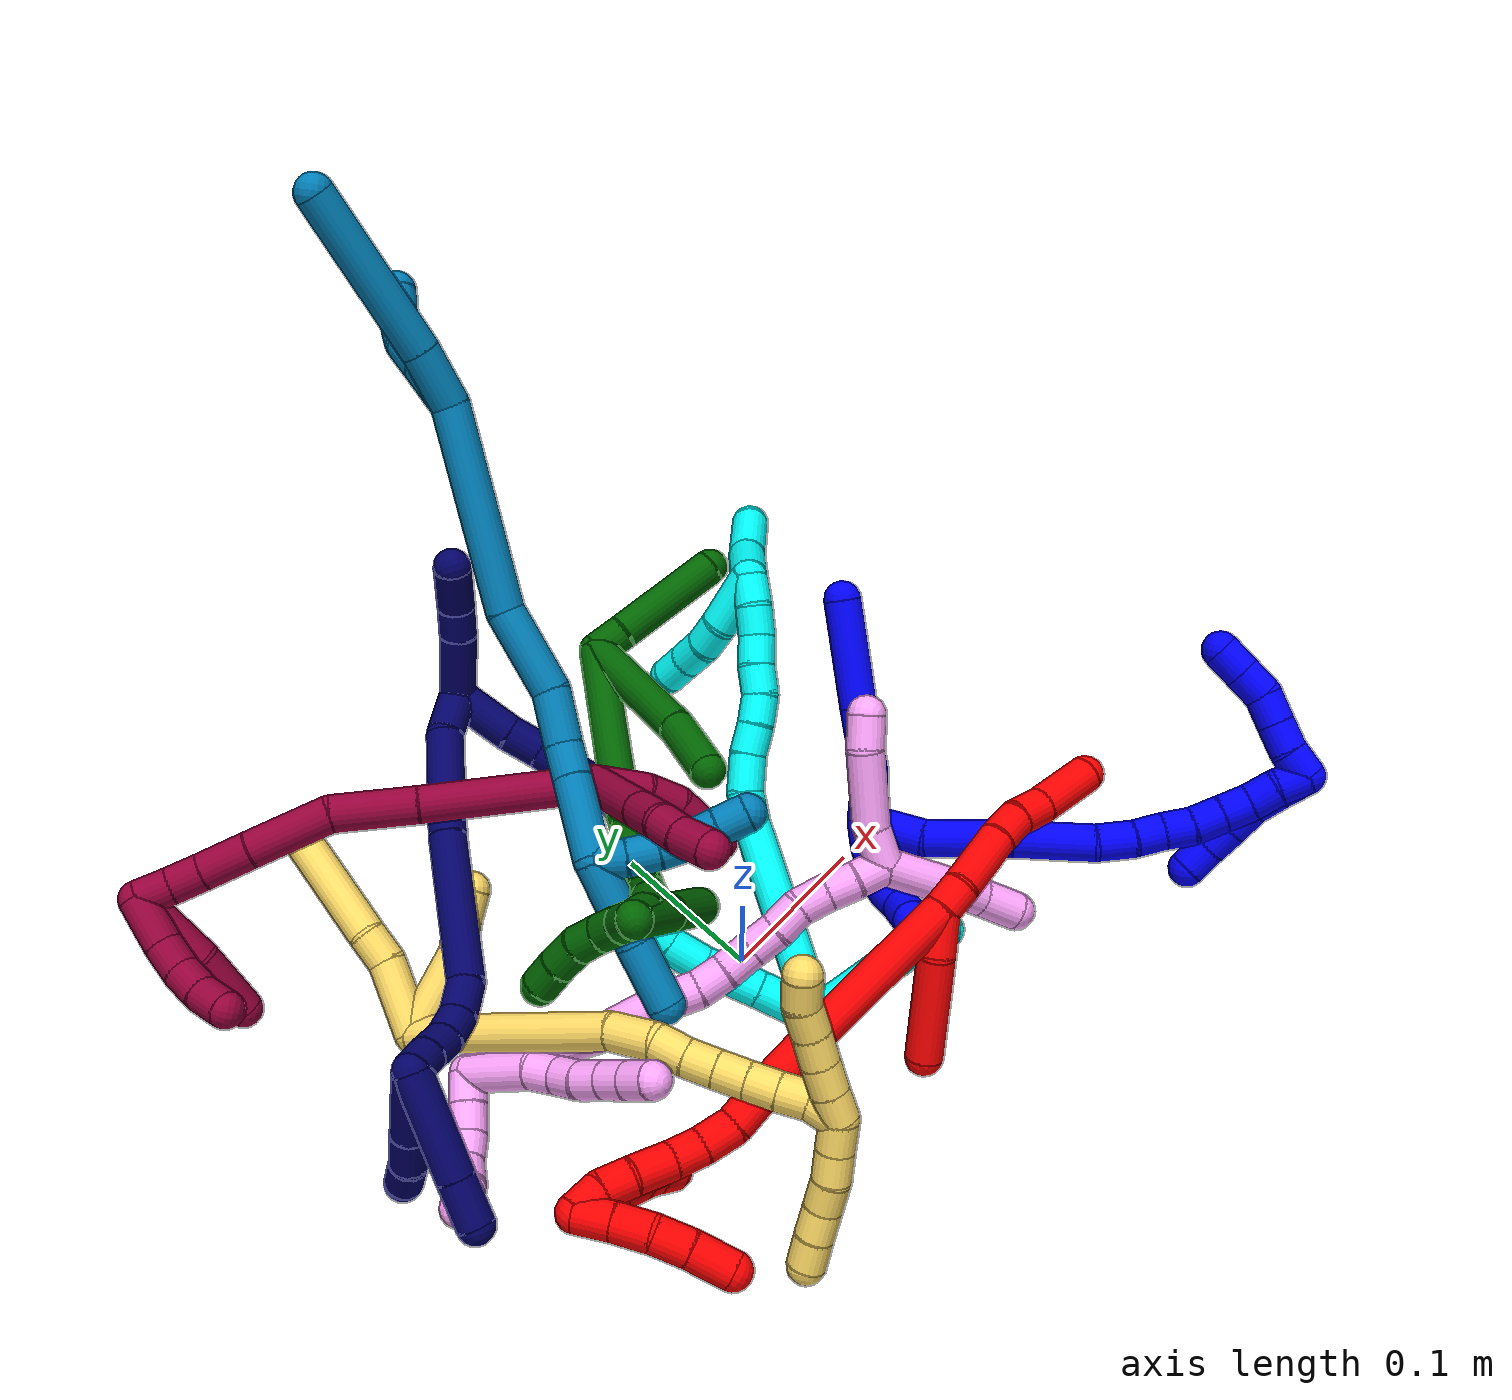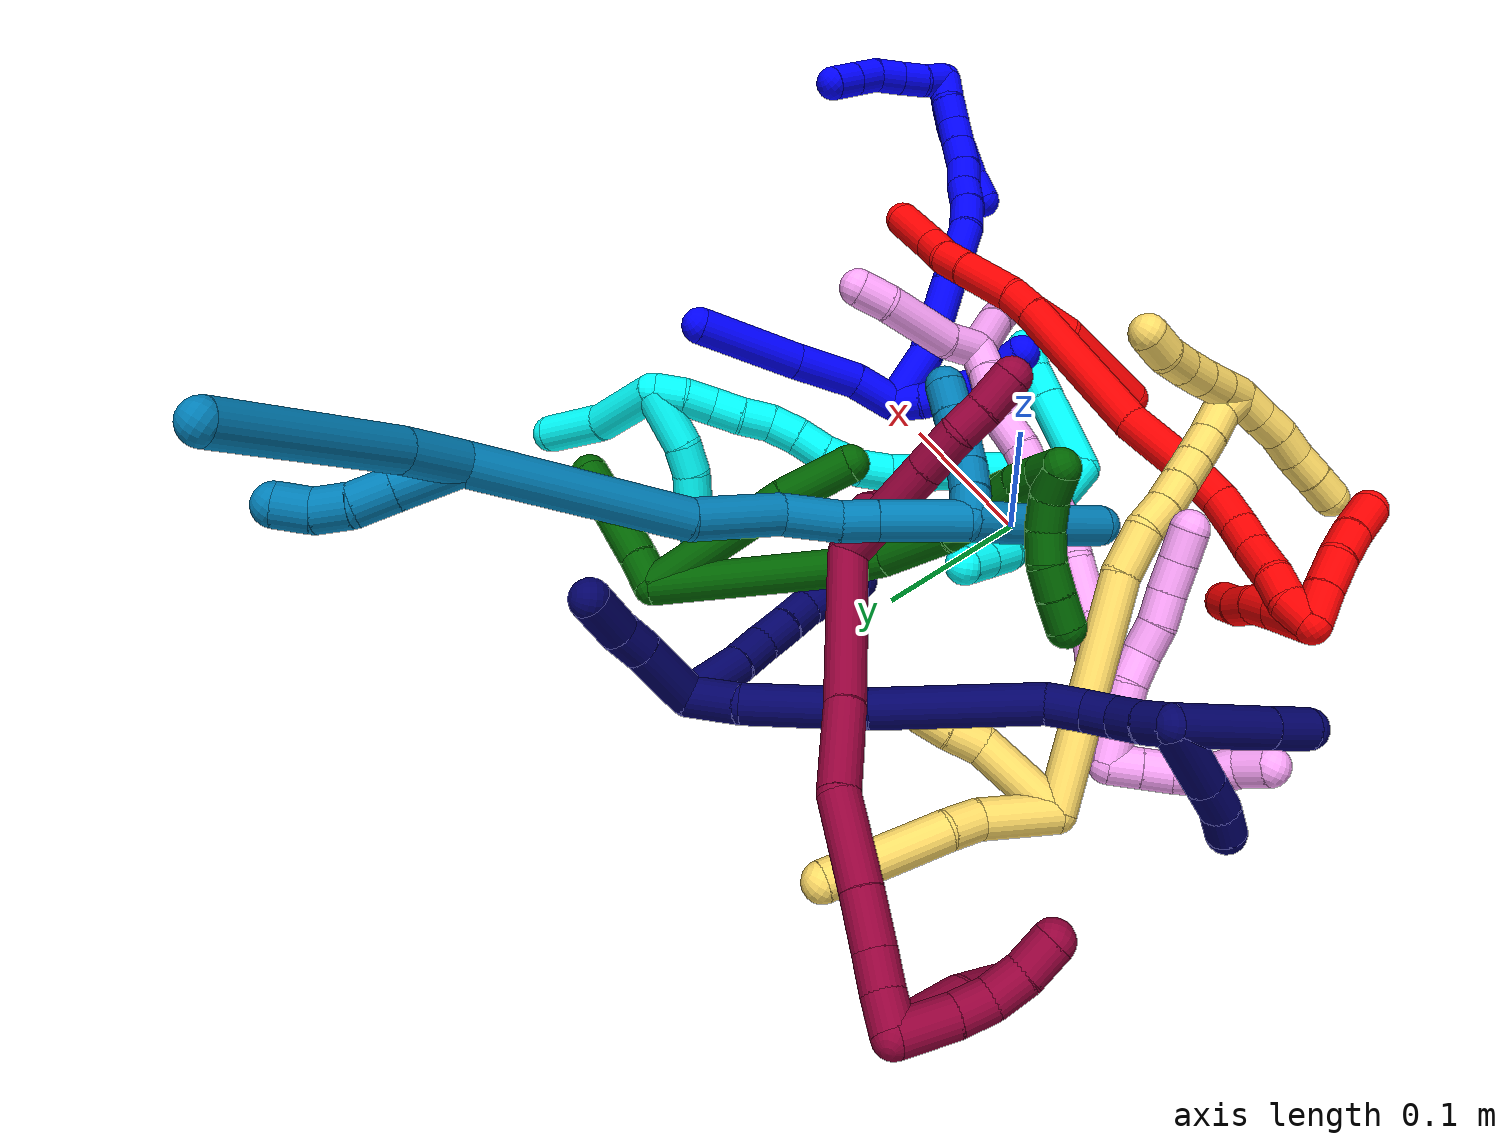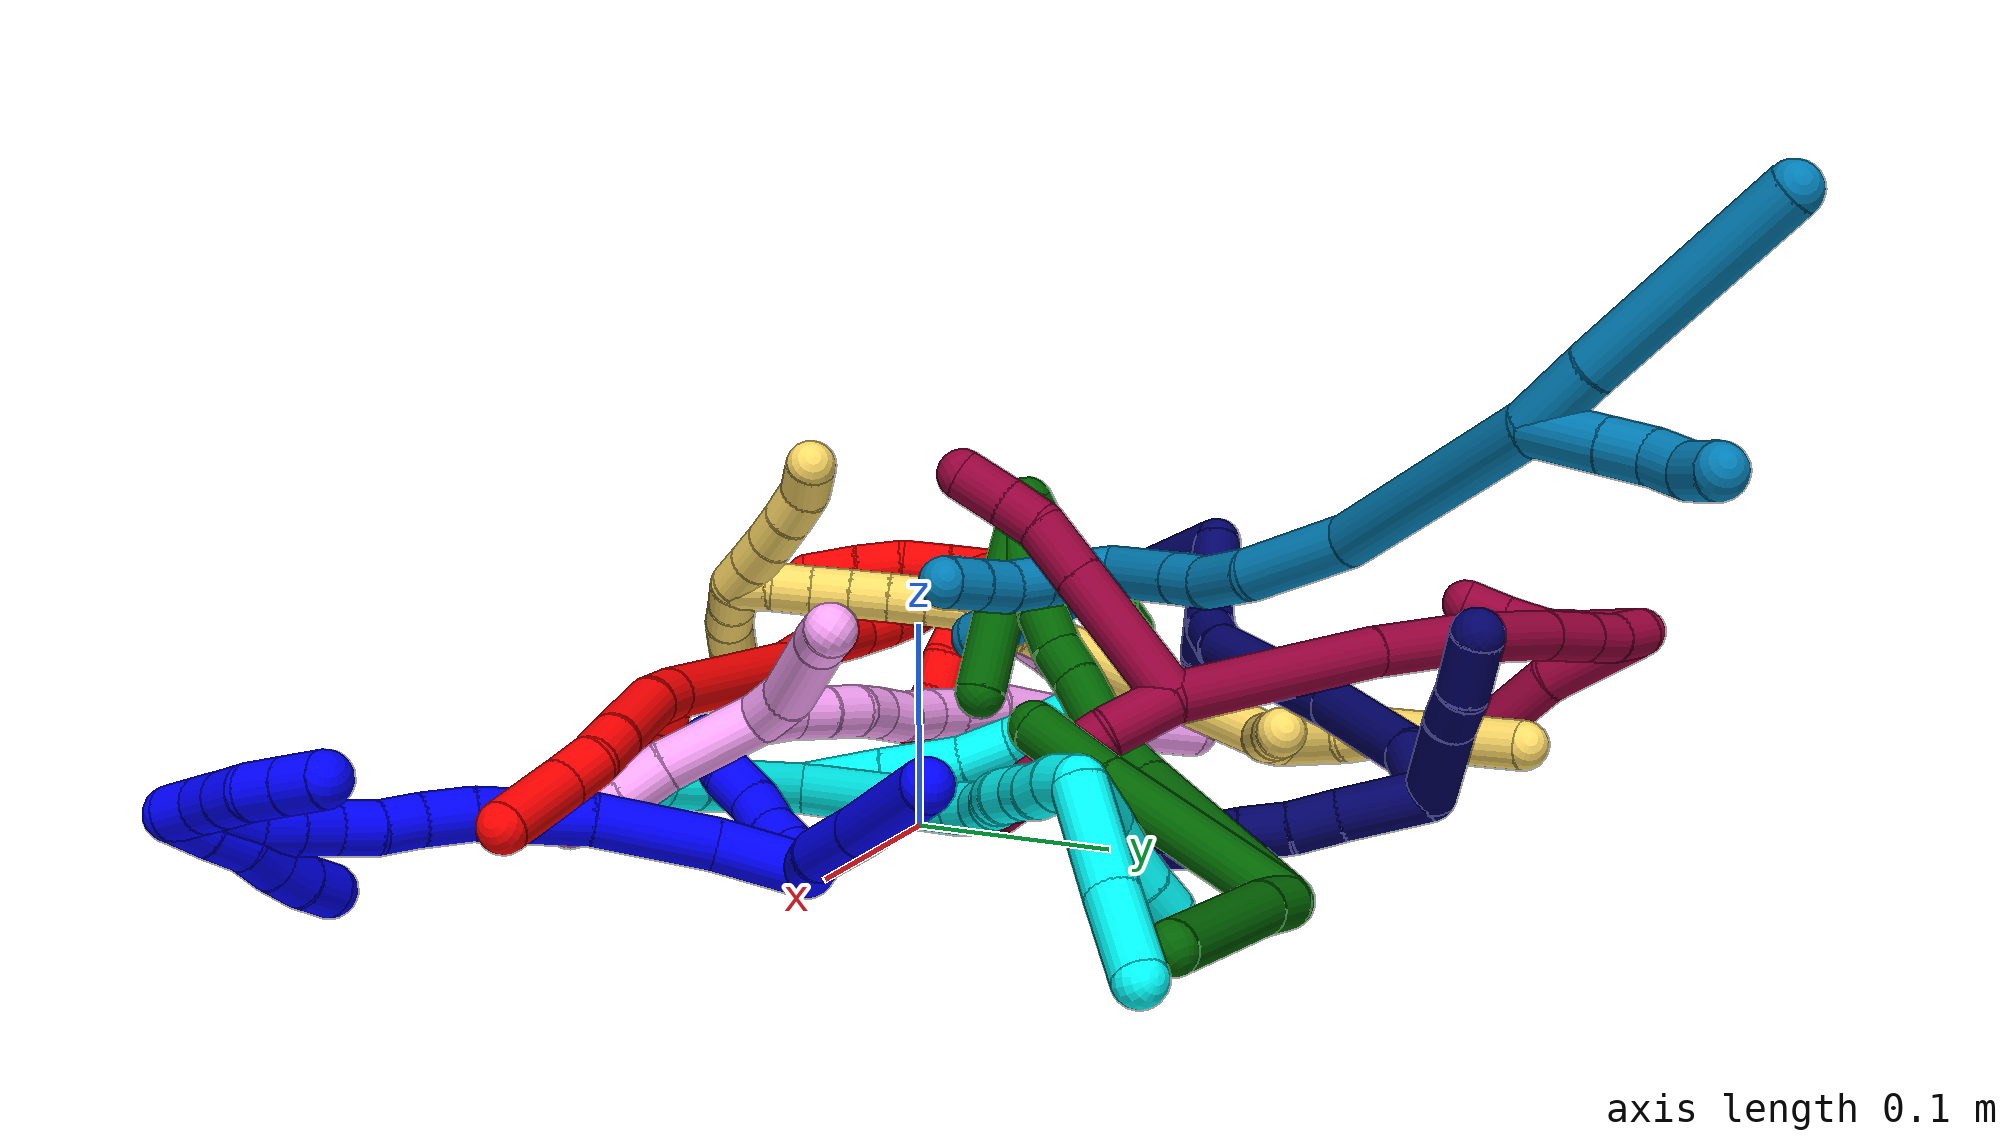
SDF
<sdf version="1.7">
 <world name="default">
  <plugin name="TubeGeneratorPlugin" filename="libtube_generator_plugin.so"/>
  <model name="photoneo_s_sensor">
   <static>1</static>
   <pose>0 0 2 1.57079 1.57079 3.14159</pose>
   <link name="link">
    <inertial><mass>0.1</mass></inertial>
    <sensor name="sensor" type="depth">
     <update_rate>30</update_rate>
     <camera>
      <horizontal_fov>1.22</horizontal_fov>
      <image><width>1920</width><height>1200</height><format>B8G8R8</format></image>
      <clip><near>0.1</near><far>4</far></clip>
      <depth_camera><output>points</output></depth_camera>
     </camera>
     <plugin name="camera_plugin" filename="libgazebo_ros_depth_camera.so">
      <baseline>0.2</baseline>
      <alwaysOn>1</alwaysOn>
      <updateRate>0.0</updateRate>
      <cameraName>camera_ir</cameraName>
      <imageTopicName>/camera/color/image_raw</imageTopicName>
      <cameraInfoTopicName>/camera/color/camera_info</cameraInfoTopicName>
      <depthImageTopicName>/camera/depth/image_raw</depthImageTopicName>
      <depthImageCameraInfoTopicName>/camera/depth/camera_info</depthImageCameraInfoTopicName>
      <pointCloudTopicName>/camera/depth/points</pointCloudTopicName>
      <frameName>fr_optical</frameName>
      <pointCloudCutoff>0.1</pointCloudCutoff>
      <pointCloudCutoffMax>2.0</pointCloudCutoffMax>
      <distortionK1>0</distortionK1>
      <distortionK2>0</distortionK2>
      <distortionK3>0</distortionK3>
      <distortionT1>0</distortionT1>
      <distortionT2>0</distortionT2>
      <CxPrime>0</CxPrime>
      <Cx>0</Cx>
      <Cy>0</Cy>
      <focalLength>0</focalLength>
      <hackBaseline>0</hackBaseline>
     </plugin>
    </sensor>
   </link>
  </model>
  <gravity>0 0 -9.8</gravity>
  <magnetic_field>6e-06 2.3e-05 -4.2e-05</magnetic_field>
  <atmosphere type="adiabatic"/>
  <physics name="default_physics" default="0" type="ode">
   <max_step_size>0.003</max_step_size>
   <real_time_factor>1</real_time_factor>
   <real_time_update_rate>1000</real_time_update_rate>
   <max_contacts>10000</max_contacts>
   <ode>
    <solver>
     <type>quick</type>
     <iters>100</iters>
     <sor>1.3</sor>
     <use_dynamic_moi_rescaling>0</use_dynamic_moi_rescaling>
    </solver>
    <constraints>
     <contact_max_correcting_vel>0</contact_max_correcting_vel>
     <contact_surface_layer>0.001</contact_surface_layer>
     <cfm>0</cfm>
     <erp>0.2</erp>
    </constraints>
   </ode>
  </physics>
  <scene><ambient>0.4 0.4 0.4 1</ambient><background>0.7 0.7 0.7 1</background><shadows>0</shadows></scene>
  <audio><device>default</device></audio>
  <spherical_coordinates>
   <surface_model>EARTH_WGS84</surface_model>
   <latitude_deg>0</latitude_deg>
   <longitude_deg>0</longitude_deg>
   <elevation>0</elevation>
   <heading_deg>0</heading_deg>
  </spherical_coordinates>
  <model name="bin">
   <static>1</static>
   <link name="bottom">
    <collision name="collision-bottom">
     <pose>0 0 -0.01 0 -0 0</pose>
     <geometry><box><size>0.8 0.6 0.02</size></box></geometry>
     <surface>
      <friction><ode><mu>100</mu><mu2>100</mu2></ode></friction>
      <contact><collide_bitmask>65535</collide_bitmask></contact>
     </surface>
    </collision>
   </link>
   <link name="west_wall">
    <collision name="collision-west_wall">
     <pose>-0.41 0 0.1 0 -0 0</pose>
     <geometry><box><size>0.02 0.6 0.2</size></box></geometry>
     <surface>
      <friction><ode><mu>100</mu><mu2>100</mu2></ode></friction>
      <contact><collide_bitmask>65535</collide_bitmask></contact>
     </surface>
    </collision>
   </link>
   <link name="east_wall">
    <collision name="collision-east_wall">
     <pose>0.41 0 0.1 0 -0 0</pose>
     <geometry><box><size>0.02 0.6 0.2</size></box></geometry>
     <surface>
      <friction><ode><mu>100</mu><mu2>100</mu2></ode></friction>
      <contact><collide_bitmask>65535</collide_bitmask></contact>
     </surface>
    </collision>
   </link>
   <link name="south_wall">
    <collision name="collision-south_wall">
     <pose>0 -0.31 0.1 0 -0 0</pose>
     <geometry><box><size>0.8 0.02 0.2</size></box></geometry>
     <surface>
      <friction><ode><mu>100</mu><mu2>100</mu2></ode></friction>
      <contact><collide_bitmask>65535</collide_bitmask></contact>
     </surface>
    </collision>
   </link>
   <link name="north_wall">
    <collision name="collision-north_wall">
     <pose>0 0.31 0.1 0 -0 0</pose>
     <geometry><box><size>0.8 0.02 0.2</size></box></geometry>
     <surface>
      <friction><ode><mu>100</mu><mu2>100</mu2></ode></friction>
      <contact><collide_bitmask>65535</collide_bitmask></contact>
     </surface>
    </collision>
   </link>
  </model>
  <model name="1">
   <static>0</static>
   <link name="1">
    <collision name="collision-cylinder-e_1_2_8">
     <pose>0.006648 -0.000282 0.014581 0.019307 0.427706 0.004193</pose>
     <geometry><cylinder><radius>0.0125</radius><length>0.032055</length></cylinder></geometry>
     <surface>
      <friction><ode><mu>1.16</mu><mu2>1.16</mu2><slip1>0</slip1><slip2>0</slip2></ode></friction>
      <contact><ode><kp>1e+06</kp><kd>1</kd><max_vel>0</max_vel><min_depth>0.001</min_depth></ode></contact>
     </surface>
    </collision>
    <visual name="visual-cylinder-e_1_2_8">
     <pose>0.006648 -0.000282 0.014581 0.019307 0.427706 0.004193</pose>
     <geometry><cylinder><radius>0.0125</radius><length>0.032055</length></cylinder></geometry>
     <material><ambient>0 0 1 1</ambient></material>
    </visual>
    <collision name="collision-cylinder-e_2_8_9">
     <pose>0.021432 0.004907 0.049889 -0.258045 0.362733 -0.047576</pose>
     <geometry><cylinder><radius>0.0125</radius><length>0.045857</length></cylinder></geometry>
     <surface>
      <friction><ode><mu>1.16</mu><mu2>1.16</mu2><slip1>0</slip1><slip2>0</slip2></ode></friction>
      <contact><ode><kp>1e+06</kp><kd>1</kd><max_vel>0</max_vel><min_depth>0.001</min_depth></ode></contact>
     </surface>
    </collision>
    <visual name="visual-cylinder-e_2_8_9">
     <pose>0.021432 0.004907 0.049889 -0.258045 0.362733 -0.047576</pose>
     <geometry><cylinder><radius>0.0125</radius><length>0.045857</length></cylinder></geometry>
     <material><ambient>0 0 1 1</ambient></material>
    </visual>
    <collision name="collision-cylinder-e_3_9_6">
     <pose>0.041675 0.01795 0.10371 -0.224928 0.342583 -0.039069</pose>
     <geometry><cylinder><radius>0.0125</radius><length>0.072088</length></cylinder></geometry>
     <surface>
      <friction><ode><mu>1.16</mu><mu2>1.16</mu2><slip1>0</slip1><slip2>0</slip2></ode></friction>
      <contact><ode><kp>1e+06</kp><kd>1</kd><max_vel>0</max_vel><min_depth>0.001</min_depth></ode></contact>
     </surface>
    </collision>
    <visual name="visual-cylinder-e_3_9_6">
     <pose>0.041675 0.01795 0.10371 -0.224928 0.342583 -0.039069</pose>
     <geometry><cylinder><radius>0.0125</radius><length>0.072088</length></cylinder></geometry>
     <material><ambient>0 0 1 1</ambient></material>
    </visual>
    <collision name="collision-cylinder-e_1_2_10">
     <pose>-0.008597 -0.002946 -0.004174 2.52689 -1.0346 -2.12388</pose>
     <geometry><cylinder><radius>0.0125</radius><length>0.02</length></cylinder></geometry>
     <surface>
      <friction><ode><mu>1.16</mu><mu2>1.16</mu2><slip1>0</slip1><slip2>0</slip2></ode></friction>
      <contact><ode><kp>1e+06</kp><kd>1</kd><max_vel>0</max_vel><min_depth>0.001</min_depth></ode></contact>
     </surface>
    </collision>
    <visual name="visual-cylinder-e_1_2_10">
     <pose>-0.008597 -0.002946 -0.004174 2.52689 -1.0346 -2.12388</pose>
     <geometry><cylinder><radius>0.0125</radius><length>0.02</length></cylinder></geometry>
     <material><ambient>0 0 1 1</ambient></material>
    </visual>
    <collision name="collision-cylinder-e_2_10_11">
     <pose>-0.025248 -0.010473 -0.012107 2.2581 -0.936459 -1.63786</pose>
     <geometry><cylinder><radius>0.0125</radius><length>0.02</length></cylinder></geometry>
     <surface>
      <friction><ode><mu>1.16</mu><mu2>1.16</mu2><slip1>0</slip1><slip2>0</slip2></ode></friction>
      <contact><ode><kp>1e+06</kp><kd>1</kd><max_vel>0</max_vel><min_depth>0.001</min_depth></ode></contact>
     </surface>
    </collision>
    <visual name="visual-cylinder-e_2_10_11">
     <pose>-0.025248 -0.010473 -0.012107 2.2581 -0.936459 -1.63786</pose>
     <geometry><cylinder><radius>0.0125</radius><length>0.02</length></cylinder></geometry>
     <material><ambient>0 0 1 1</ambient></material>
    </visual>
    <collision name="collision-cylinder-e_3_11_12">
     <pose>-0.042199 -0.019348 -0.017424 1.91874 -1.09653 -1.4333</pose>
     <geometry><cylinder><radius>0.0125</radius><length>0.02</length></cylinder></geometry>
     <surface>
      <friction><ode><mu>1.16</mu><mu2>1.16</mu2><slip1>0</slip1><slip2>0</slip2></ode></friction>
      <contact><ode><kp>1e+06</kp><kd>1</kd><max_vel>0</max_vel><min_depth>0.001</min_depth></ode></contact>
     </surface>
    </collision>
    <visual name="visual-cylinder-e_3_11_12">
     <pose>-0.042199 -0.019348 -0.017424 1.91874 -1.09653 -1.4333</pose>
     <geometry><cylinder><radius>0.0125</radius><length>0.02</length></cylinder></geometry>
     <material><ambient>0 0 1 1</ambient></material>
    </visual>
    <collision name="collision-cylinder-e_4_12_13">
     <pose>-0.058537 -0.030272 -0.019784 1.69129 -0.839378 -0.932865</pose>
     <geometry><cylinder><radius>0.0125</radius><length>0.02</length></cylinder></geometry>
     <surface>
      <friction><ode><mu>1.16</mu><mu2>1.16</mu2><slip1>0</slip1><slip2>0</slip2></ode></friction>
      <contact><ode><kp>1e+06</kp><kd>1</kd><max_vel>0</max_vel><min_depth>0.001</min_depth></ode></contact>
     </surface>
    </collision>
    <visual name="visual-cylinder-e_4_12_13">
     <pose>-0.058537 -0.030272 -0.019784 1.69129 -0.839378 -0.932865</pose>
     <geometry><cylinder><radius>0.0125</radius><length>0.02</length></cylinder></geometry>
     <material><ambient>0 0 1 1</ambient></material>
    </visual>
    <collision name="collision-cylinder-e_5_13_5">
     <pose>-0.074586 -0.041915 -0.019691 1.39381 -1.03647 -0.890621</pose>
     <geometry><cylinder><radius>0.0125</radius><length>0.02</length></cylinder></geometry>
     <surface>
      <friction><ode><mu>1.16</mu><mu2>1.16</mu2><slip1>0</slip1><slip2>0</slip2></ode></friction>
      <contact><ode><kp>1e+06</kp><kd>1</kd><max_vel>0</max_vel><min_depth>0.001</min_depth></ode></contact>
     </surface>
    </collision>
    <visual name="visual-cylinder-e_5_13_5">
     <pose>-0.074586 -0.041915 -0.019691 1.39381 -1.03647 -0.890621</pose>
     <geometry><cylinder><radius>0.0125</radius><length>0.02</length></cylinder></geometry>
     <material><ambient>0 0 1 1</ambient></material>
    </visual>
    <collision name="collision-cylinder-e_1_2_14">
     <pose>-0.004747 -0.021273 -0.001294 1.63154 -0.219166 -0.23278</pose>
     <geometry><cylinder><radius>0.0125</radius><length>0.043669</length></cylinder></geometry>
     <surface>
      <friction><ode><mu>1.16</mu><mu2>1.16</mu2><slip1>0</slip1><slip2>0</slip2></ode></friction>
      <contact><ode><kp>1e+06</kp><kd>1</kd><max_vel>0</max_vel><min_depth>0.001</min_depth></ode></contact>
     </surface>
    </collision>
    <visual name="visual-cylinder-e_1_2_14">
     <pose>-0.004747 -0.021273 -0.001294 1.63154 -0.219166 -0.23278</pose>
     <geometry><cylinder><radius>0.0125</radius><length>0.043669</length></cylinder></geometry>
     <material><ambient>0 0 1 1</ambient></material>
    </visual>
    <collision name="collision-cylinder-e_2_14_15">
     <pose>-0.009152 -0.071353 0.000274 1.4718 0.011834 0.010717</pose>
     <geometry><cylinder><radius>0.0125</radius><length>0.057902</length></cylinder></geometry>
     <surface>
      <friction><ode><mu>1.16</mu><mu2>1.16</mu2><slip1>0</slip1><slip2>0</slip2></ode></friction>
      <contact><ode><kp>1e+06</kp><kd>1</kd><max_vel>0</max_vel><min_depth>0.001</min_depth></ode></contact>
     </surface>
    </collision>
    <visual name="visual-cylinder-e_2_14_15">
     <pose>-0.009152 -0.071353 0.000274 1.4718 0.011834 0.010717</pose>
     <geometry><cylinder><radius>0.0125</radius><length>0.057902</length></cylinder></geometry>
     <material><ambient>0 0 1 1</ambient></material>
    </visual>
    <collision name="collision-cylinder-e_3_15_16">
     <pose>-0.005687 -0.126664 0.002745 1.58552 0.117258 0.118993</pose>
     <geometry><cylinder><radius>0.0125</radius><length>0.053381</length></cylinder></geometry>
     <surface>
      <friction><ode><mu>1.16</mu><mu2>1.16</mu2><slip1>0</slip1><slip2>0</slip2></ode></friction>
      <contact><ode><kp>1e+06</kp><kd>1</kd><max_vel>0</max_vel><min_depth>0.001</min_depth></ode></contact>
     </surface>
    </collision>
    <visual name="visual-cylinder-e_3_15_16">
     <pose>-0.005687 -0.126664 0.002745 1.58552 0.117258 0.118993</pose>
     <geometry><cylinder><radius>0.0125</radius><length>0.053381</length></cylinder></geometry>
     <material><ambient>0 0 1 1</ambient></material>
    </visual>
    <collision name="collision-cylinder-e_4_16_17">
     <pose>0.001743 -0.164787 0.002702 1.54086 0.354839 0.344582</pose>
     <geometry><cylinder><radius>0.0125</radius><length>0.024792</length></cylinder></geometry>
     <surface>
      <friction><ode><mu>1.16</mu><mu2>1.16</mu2><slip1>0</slip1><slip2>0</slip2></ode></friction>
      <contact><ode><kp>1e+06</kp><kd>1</kd><max_vel>0</max_vel><min_depth>0.001</min_depth></ode></contact>
     </surface>
    </collision>
    <visual name="visual-cylinder-e_4_16_17">
     <pose>0.001743 -0.164787 0.002702 1.54086 0.354839 0.344582</pose>
     <geometry><cylinder><radius>0.0125</radius><length>0.024792</length></cylinder></geometry>
     <material><ambient>0 0 1 1</ambient></material>
    </visual>
    <collision name="collision-cylinder-e_5_17_18">
     <pose>0.01076 -0.185228 0.004142 1.44771 0.487218 0.432512</pose>
     <geometry><cylinder><radius>0.0125</radius><length>0.020122</length></cylinder></geometry>
     <surface>
      <friction><ode><mu>1.16</mu><mu2>1.16</mu2><slip1>0</slip1><slip2>0</slip2></ode></friction>
      <contact><ode><kp>1e+06</kp><kd>1</kd><max_vel>0</max_vel><min_depth>0.001</min_depth></ode></contact>
     </surface>
    </collision>
    <visual name="visual-cylinder-e_5_17_18">
     <pose>0.01076 -0.185228 0.004142 1.44771 0.487218 0.432512</pose>
     <geometry><cylinder><radius>0.0125</radius><length>0.020122</length></cylinder></geometry>
     <material><ambient>0 0 1 1</ambient></material>
    </visual>
    <collision name="collision-cylinder-e_6_18_19">
     <pose>0.018481 -0.203469 0.006804 1.40557 0.305508 0.259352</pose>
     <geometry><cylinder><radius>0.0125</radius><length>0.020022</length></cylinder></geometry>
     <surface>
      <friction><ode><mu>1.16</mu><mu2>1.16</mu2><slip1>0</slip1><slip2>0</slip2></ode></friction>
      <contact><ode><kp>1e+06</kp><kd>1</kd><max_vel>0</max_vel><min_depth>0.001</min_depth></ode></contact>
     </surface>
    </collision>
    <visual name="visual-cylinder-e_6_18_19">
     <pose>0.018481 -0.203469 0.006804 1.40557 0.305508 0.259352</pose>
     <geometry><cylinder><radius>0.0125</radius><length>0.020022</length></cylinder></geometry>
     <material><ambient>0 0 1 1</ambient></material>
    </visual>
    <collision name="collision-cylinder-e_7_19_20">
     <pose>0.025509 -0.221534 0.011437 1.23039 0.412739 0.293757</pose>
     <geometry><cylinder><radius>0.0125</radius><length>0.020029</length></cylinder></geometry>
     <surface>
      <friction><ode><mu>1.16</mu><mu2>1.16</mu2><slip1>0</slip1><slip2>0</slip2></ode></friction>
      <contact><ode><kp>1e+06</kp><kd>1</kd><max_vel>0</max_vel><min_depth>0.001</min_depth></ode></contact>
     </surface>
    </collision>
    <visual name="visual-cylinder-e_7_19_20">
     <pose>0.025509 -0.221534 0.011437 1.23039 0.412739 0.293757</pose>
     <geometry><cylinder><radius>0.0125</radius><length>0.020029</length></cylinder></geometry>
     <material><ambient>0 0 1 1</ambient></material>
    </visual>
    <collision name="collision-cylinder-e_8_20_21">
     <pose>0.033423 -0.238858 0.017605 1.22712 0.400016 0.283605</pose>
     <geometry><cylinder><radius>0.0125</radius><length>0.020011</length></cylinder></geometry>
     <surface>
      <friction><ode><mu>1.16</mu><mu2>1.16</mu2><slip1>0</slip1><slip2>0</slip2></ode></friction>
      <contact><ode><kp>1e+06</kp><kd>1</kd><max_vel>0</max_vel><min_depth>0.001</min_depth></ode></contact>
     </surface>
    </collision>
    <visual name="visual-cylinder-e_8_20_21">
     <pose>0.033423 -0.238858 0.017605 1.22712 0.400016 0.283605</pose>
     <geometry><cylinder><radius>0.0125</radius><length>0.020011</length></cylinder></geometry>
     <material><ambient>0 0 1 1</ambient></material>
    </visual>
    <collision name="collision-cylinder-e_9_21_22">
     <pose>0.039801 -0.255754 0.025861 1.011 0.250467 0.13913</pose>
     <geometry><cylinder><radius>0.0125</radius><length>0.020026</length></cylinder></geometry>
     <surface>
      <friction><ode><mu>1.16</mu><mu2>1.16</mu2><slip1>0</slip1><slip2>0</slip2></ode></friction>
      <contact><ode><kp>1e+06</kp><kd>1</kd><max_vel>0</max_vel><min_depth>0.001</min_depth></ode></contact>
     </surface>
    </collision>
    <visual name="visual-cylinder-e_9_21_22">
     <pose>0.039801 -0.255754 0.025861 1.011 0.250467 0.13913</pose>
     <geometry><cylinder><radius>0.0125</radius><length>0.020026</length></cylinder></geometry>
     <material><ambient>0 0 1 1</ambient></material>
    </visual>
    <collision name="collision-cylinder-e_10_22_1">
     <pose>0.045699 -0.272841 0.034201 1.2256 0.347841 0.245816</pose>
     <geometry><cylinder><radius>0.0125</radius><length>0.020047</length></cylinder></geometry>
     <surface>
      <friction><ode><mu>1.16</mu><mu2>1.16</mu2><slip1>0</slip1><slip2>0</slip2></ode></friction>
      <contact><ode><kp>1e+06</kp><kd>1</kd><max_vel>0</max_vel><min_depth>0.001</min_depth></ode></contact>
     </surface>
    </collision>
    <visual name="visual-cylinder-e_10_22_1">
     <pose>0.045699 -0.272841 0.034201 1.2256 0.347841 0.245816</pose>
     <geometry><cylinder><radius>0.0125</radius><length>0.020047</length></cylinder></geometry>
     <material><ambient>0 0 1 1</ambient></material>
    </visual>
    <collision name="collision-cylinder-e_1_1_23">
     <pose>0.04786 -0.273465 0.031869 -2.16082 -0.125954 0.235144</pose>
     <geometry><cylinder><radius>0.0125</radius><length>0.02</length></cylinder></geometry>
     <surface>
      <friction><ode><mu>1.16</mu><mu2>1.16</mu2><slip1>0</slip1><slip2>0</slip2></ode></friction>
      <contact><ode><kp>1e+06</kp><kd>1</kd><max_vel>0</max_vel><min_depth>0.001</min_depth></ode></contact>
     </surface>
    </collision>
    <visual name="visual-cylinder-e_1_1_23">
     <pose>0.04786 -0.273465 0.031869 -2.16082 -0.125954 0.235144</pose>
     <geometry><cylinder><radius>0.0125</radius><length>0.02</length></cylinder></geometry>
     <material><ambient>0 0 1 1</ambient></material>
    </visual>
    <collision name="collision-cylinder-e_2_23_24">
     <pose>0.044681 -0.257178 0.020728 -2.18078 -0.19343 0.368122</pose>
     <geometry><cylinder><radius>0.0125</radius><length>0.02</length></cylinder></geometry>
     <surface>
      <friction><ode><mu>1.16</mu><mu2>1.16</mu2><slip1>0</slip1><slip2>0</slip2></ode></friction>
      <contact><ode><kp>1e+06</kp><kd>1</kd><max_vel>0</max_vel><min_depth>0.001</min_depth></ode></contact>
     </surface>
    </collision>
    <visual name="visual-cylinder-e_2_23_24">
     <pose>0.044681 -0.257178 0.020728 -2.18078 -0.19343 0.368122</pose>
     <geometry><cylinder><radius>0.0125</radius><length>0.02</length></cylinder></geometry>
     <material><ambient>0 0 1 1</ambient></material>
    </visual>
    <collision name="collision-cylinder-e_3_24_25">
     <pose>0.041313 -0.24288 0.007438 -2.4574 -0.145107 0.402676</pose>
     <geometry><cylinder><radius>0.0125</radius><length>0.02</length></cylinder></geometry>
     <surface>
      <friction><ode><mu>1.16</mu><mu2>1.16</mu2><slip1>0</slip1><slip2>0</slip2></ode></friction>
      <contact><ode><kp>1e+06</kp><kd>1</kd><max_vel>0</max_vel><min_depth>0.001</min_depth></ode></contact>
     </surface>
    </collision>
    <visual name="visual-cylinder-e_3_24_25">
     <pose>0.041313 -0.24288 0.007438 -2.4574 -0.145107 0.402676</pose>
     <geometry><cylinder><radius>0.0125</radius><length>0.02</length></cylinder></geometry>
     <material><ambient>0 0 1 1</ambient></material>
    </visual>
    <collision name="collision-cylinder-e_4_25_26">
     <pose>0.037763 -0.229935 -0.007357 -2.38777 -0.212022 0.525232</pose>
     <geometry><cylinder><radius>0.0125</radius><length>0.02</length></cylinder></geometry>
     <surface>
      <friction><ode><mu>1.16</mu><mu2>1.16</mu2><slip1>0</slip1><slip2>0</slip2></ode></friction>
      <contact><ode><kp>1e+06</kp><kd>1</kd><max_vel>0</max_vel><min_depth>0.001</min_depth></ode></contact>
     </surface>
    </collision>
    <visual name="visual-cylinder-e_4_25_26">
     <pose>0.037763 -0.229935 -0.007357 -2.38777 -0.212022 0.525232</pose>
     <geometry><cylinder><radius>0.0125</radius><length>0.02</length></cylinder></geometry>
     <material><ambient>0 0 1 1</ambient></material>
    </visual>
    <collision name="collision-cylinder-e_5_26_4">
     <pose>0.032088 -0.216779 -0.021226 -2.37717 -0.365141 0.861105</pose>
     <geometry><cylinder><radius>0.0125</radius><length>0.02</length></cylinder></geometry>
     <surface>
      <friction><ode><mu>1.16</mu><mu2>1.16</mu2><slip1>0</slip1><slip2>0</slip2></ode></friction>
      <contact><ode><kp>1e+06</kp><kd>1</kd><max_vel>0</max_vel><min_depth>0.001</min_depth></ode></contact>
     </surface>
    </collision>
    <visual name="visual-cylinder-e_5_26_4">
     <pose>0.032088 -0.216779 -0.021226 -2.37717 -0.365141 0.861105</pose>
     <geometry><cylinder><radius>0.0125</radius><length>0.02</length></cylinder></geometry>
     <material><ambient>0 0 1 1</ambient></material>
    </visual>
    <collision name="collision-cylinder-e_1_1_27">
     <pose>0.051283 -0.27532 0.044771 -0.713323 0.218379 -0.081647</pose>
     <geometry><cylinder><radius>0.0125</radius><length>0.02</length></cylinder></geometry>
     <surface>
      <friction><ode><mu>1.16</mu><mu2>1.16</mu2><slip1>0</slip1><slip2>0</slip2></ode></friction>
      <contact><ode><kp>1e+06</kp><kd>1</kd><max_vel>0</max_vel><min_depth>0.001</min_depth></ode></contact>
     </surface>
    </collision>
    <visual name="visual-cylinder-e_1_1_27">
     <pose>0.051283 -0.27532 0.044771 -0.713323 0.218379 -0.081647</pose>
     <geometry><cylinder><radius>0.0125</radius><length>0.02</length></cylinder></geometry>
     <material><ambient>0 0 1 1</ambient></material>
    </visual>
    <collision name="collision-cylinder-e_2_27_28">
     <pose>0.057156 -0.264113 0.060093 -0.545515 0.379774 -0.107426</pose>
     <geometry><cylinder><radius>0.0125</radius><length>0.02</length></cylinder></geometry>
     <surface>
      <friction><ode><mu>1.16</mu><mu2>1.16</mu2><slip1>0</slip1><slip2>0</slip2></ode></friction>
      <contact><ode><kp>1e+06</kp><kd>1</kd><max_vel>0</max_vel><min_depth>0.001</min_depth></ode></contact>
     </surface>
    </collision>
    <visual name="visual-cylinder-e_2_27_28">
     <pose>0.057156 -0.264113 0.060093 -0.545515 0.379774 -0.107426</pose>
     <geometry><cylinder><radius>0.0125</radius><length>0.02</length></cylinder></geometry>
     <material><ambient>0 0 1 1</ambient></material>
    </visual>
    <collision name="collision-cylinder-e_3_28_29">
     <pose>0.064465 -0.254595 0.076092 -0.527927 0.368419 -0.100629</pose>
     <geometry><cylinder><radius>0.0125</radius><length>0.02</length></cylinder></geometry>
     <surface>
      <friction><ode><mu>1.16</mu><mu2>1.16</mu2><slip1>0</slip1><slip2>0</slip2></ode></friction>
      <contact><ode><kp>1e+06</kp><kd>1</kd><max_vel>0</max_vel><min_depth>0.001</min_depth></ode></contact>
     </surface>
    </collision>
    <visual name="visual-cylinder-e_3_28_29">
     <pose>0.064465 -0.254595 0.076092 -0.527927 0.368419 -0.100629</pose>
     <geometry><cylinder><radius>0.0125</radius><length>0.02</length></cylinder></geometry>
     <material><ambient>0 0 1 1</ambient></material>
    </visual>
    <collision name="collision-cylinder-e_4_29_30">
     <pose>0.070118 -0.242586 0.090659 -0.843345 0.20665 -0.092963</pose>
     <geometry><cylinder><radius>0.0125</radius><length>0.02</length></cylinder></geometry>
     <surface>
      <friction><ode><mu>1.16</mu><mu2>1.16</mu2><slip1>0</slip1><slip2>0</slip2></ode></friction>
      <contact><ode><kp>1e+06</kp><kd>1</kd><max_vel>0</max_vel><min_depth>0.001</min_depth></ode></contact>
     </surface>
    </collision>
    <visual name="visual-cylinder-e_4_29_30">
     <pose>0.070118 -0.242586 0.090659 -0.843345 0.20665 -0.092963</pose>
     <geometry><cylinder><radius>0.0125</radius><length>0.02</length></cylinder></geometry>
     <material><ambient>0 0 1 1</ambient></material>
    </visual>
    <collision name="collision-cylinder-e_5_30_3">
     <pose>0.074235 -0.227942 0.103643 -0.847434 0.208067 -0.094117</pose>
     <geometry><cylinder><radius>0.0125</radius><length>0.02</length></cylinder></geometry>
     <surface>
      <friction><ode><mu>1.16</mu><mu2>1.16</mu2><slip1>0</slip1><slip2>0</slip2></ode></friction>
      <contact><ode><kp>1e+06</kp><kd>1</kd><max_vel>0</max_vel><min_depth>0.001</min_depth></ode></contact>
     </surface>
    </collision>
    <visual name="visual-cylinder-e_5_30_3">
     <pose>0.074235 -0.227942 0.103643 -0.847434 0.208067 -0.094117</pose>
     <geometry><cylinder><radius>0.0125</radius><length>0.02</length></cylinder></geometry>
     <material><ambient>0 0 1 1</ambient></material>
    </visual>
    <collision name="collision-sphere-3">
     <pose>0.076301 -0.220607 0.11012 0 -0 0</pose>
     <geometry><sphere><radius>0.0125</radius></sphere></geometry>
     <surface>
      <friction><ode><mu>1.16</mu><mu2>1.16</mu2><slip1>0</slip1><slip2>0</slip2></ode></friction>
      <contact><ode><kp>1e+06</kp><kd>1</kd><max_vel>0</max_vel><min_depth>0.001</min_depth></ode></contact>
     </surface>
    </collision>
    <visual name="visual-sphere-3">
     <pose>0.076301 -0.220607 0.11012 0 -0 0</pose>
     <geometry><sphere><radius>0.0125</radius></sphere></geometry>
     <material><ambient>0 0 1 1</ambient></material>
    </visual>
    <collision name="collision-sphere-30">
     <pose>0.07217 -0.235276 0.097167 0 -0 0</pose>
     <geometry><sphere><radius>0.0125</radius></sphere></geometry>
     <surface>
      <friction><ode><mu>1.16</mu><mu2>1.16</mu2><slip1>0</slip1><slip2>0</slip2></ode></friction>
      <contact><ode><kp>1e+06</kp><kd>1</kd><max_vel>0</max_vel><min_depth>0.001</min_depth></ode></contact>
     </surface>
    </collision>
    <visual name="visual-sphere-30">
     <pose>0.07217 -0.235276 0.097167 0 -0 0</pose>
     <geometry><sphere><radius>0.0125</radius></sphere></geometry>
     <material><ambient>0 0 1 1</ambient></material>
    </visual>
    <collision name="collision-sphere-29">
     <pose>0.068066 -0.249895 0.084151 0 -0 0</pose>
     <geometry><sphere><radius>0.0125</radius></sphere></geometry>
     <surface>
      <friction><ode><mu>1.16</mu><mu2>1.16</mu2><slip1>0</slip1><slip2>0</slip2></ode></friction>
      <contact><ode><kp>1e+06</kp><kd>1</kd><max_vel>0</max_vel><min_depth>0.001</min_depth></ode></contact>
     </surface>
    </collision>
    <visual name="visual-sphere-29">
     <pose>0.068066 -0.249895 0.084151 0 -0 0</pose>
     <geometry><sphere><radius>0.0125</radius></sphere></geometry>
     <material><ambient>0 0 1 1</ambient></material>
    </visual>
    <collision name="collision-sphere-28">
     <pose>0.060863 -0.259294 0.068033 0 -0 0</pose>
     <geometry><sphere><radius>0.0125</radius></sphere></geometry>
     <surface>
      <friction><ode><mu>1.16</mu><mu2>1.16</mu2><slip1>0</slip1><slip2>0</slip2></ode></friction>
      <contact><ode><kp>1e+06</kp><kd>1</kd><max_vel>0</max_vel><min_depth>0.001</min_depth></ode></contact>
     </surface>
    </collision>
    <visual name="visual-sphere-28">
     <pose>0.060863 -0.259294 0.068033 0 -0 0</pose>
     <geometry><sphere><radius>0.0125</radius></sphere></geometry>
     <material><ambient>0 0 1 1</ambient></material>
    </visual>
    <collision name="collision-sphere-27">
     <pose>0.053449 -0.268932 0.052154 0 -0 0</pose>
     <geometry><sphere><radius>0.0125</radius></sphere></geometry>
     <surface>
      <friction><ode><mu>1.16</mu><mu2>1.16</mu2><slip1>0</slip1><slip2>0</slip2></ode></friction>
      <contact><ode><kp>1e+06</kp><kd>1</kd><max_vel>0</max_vel><min_depth>0.001</min_depth></ode></contact>
     </surface>
    </collision>
    <visual name="visual-sphere-27">
     <pose>0.053449 -0.268932 0.052154 0 -0 0</pose>
     <geometry><sphere><radius>0.0125</radius></sphere></geometry>
     <material><ambient>0 0 1 1</ambient></material>
    </visual>
    <collision name="collision-sphere-4">
     <pose>0.028517 -0.210314 -0.027968 0 -0 0</pose>
     <geometry><sphere><radius>0.0125</radius></sphere></geometry>
     <surface>
      <friction><ode><mu>1.16</mu><mu2>1.16</mu2><slip1>0</slip1><slip2>0</slip2></ode></friction>
      <contact><ode><kp>1e+06</kp><kd>1</kd><max_vel>0</max_vel><min_depth>0.001</min_depth></ode></contact>
     </surface>
    </collision>
    <visual name="visual-sphere-4">
     <pose>0.028517 -0.210314 -0.027968 0 -0 0</pose>
     <geometry><sphere><radius>0.0125</radius></sphere></geometry>
     <material><ambient>0 0 1 1</ambient></material>
    </visual>
    <collision name="collision-sphere-26">
     <pose>0.035658 -0.223244 -0.014485 0 -0 0</pose>
     <geometry><sphere><radius>0.0125</radius></sphere></geometry>
     <surface>
      <friction><ode><mu>1.16</mu><mu2>1.16</mu2><slip1>0</slip1><slip2>0</slip2></ode></friction>
      <contact><ode><kp>1e+06</kp><kd>1</kd><max_vel>0</max_vel><min_depth>0.001</min_depth></ode></contact>
     </surface>
    </collision>
    <visual name="visual-sphere-26">
     <pose>0.035658 -0.223244 -0.014485 0 -0 0</pose>
     <geometry><sphere><radius>0.0125</radius></sphere></geometry>
     <material><ambient>0 0 1 1</ambient></material>
    </visual>
    <collision name="collision-sphere-25">
     <pose>0.039867 -0.236626 -0.000229 0 -0 0</pose>
     <geometry><sphere><radius>0.0125</radius></sphere></geometry>
     <surface>
      <friction><ode><mu>1.16</mu><mu2>1.16</mu2><slip1>0</slip1><slip2>0</slip2></ode></friction>
      <contact><ode><kp>1e+06</kp><kd>1</kd><max_vel>0</max_vel><min_depth>0.001</min_depth></ode></contact>
     </surface>
    </collision>
    <visual name="visual-sphere-25">
     <pose>0.039867 -0.236626 -0.000229 0 -0 0</pose>
     <geometry><sphere><radius>0.0125</radius></sphere></geometry>
     <material><ambient>0 0 1 1</ambient></material>
    </visual>
    <collision name="collision-sphere-24">
     <pose>0.042759 -0.249134 0.015106 0 -0 0</pose>
     <geometry><sphere><radius>0.0125</radius></sphere></geometry>
     <surface>
      <friction><ode><mu>1.16</mu><mu2>1.16</mu2><slip1>0</slip1><slip2>0</slip2></ode></friction>
      <contact><ode><kp>1e+06</kp><kd>1</kd><max_vel>0</max_vel><min_depth>0.001</min_depth></ode></contact>
     </surface>
    </collision>
    <visual name="visual-sphere-24">
     <pose>0.042759 -0.249134 0.015106 0 -0 0</pose>
     <geometry><sphere><radius>0.0125</radius></sphere></geometry>
     <material><ambient>0 0 1 1</ambient></material>
    </visual>
    <collision name="collision-sphere-23">
     <pose>0.046604 -0.265221 0.02635 0 -0 0</pose>
     <geometry><sphere><radius>0.0125</radius></sphere></geometry>
     <surface>
      <friction><ode><mu>1.16</mu><mu2>1.16</mu2><slip1>0</slip1><slip2>0</slip2></ode></friction>
      <contact><ode><kp>1e+06</kp><kd>1</kd><max_vel>0</max_vel><min_depth>0.001</min_depth></ode></contact>
     </surface>
    </collision>
    <visual name="visual-sphere-23">
     <pose>0.046604 -0.265221 0.02635 0 -0 0</pose>
     <geometry><sphere><radius>0.0125</radius></sphere></geometry>
     <material><ambient>0 0 1 1</ambient></material>
    </visual>
    <collision name="collision-sphere-1">
     <pose>0.049116 -0.281708 0.037389 0 -0 0</pose>
     <geometry><sphere><radius>0.0125</radius></sphere></geometry>
     <surface>
      <friction><ode><mu>1.16</mu><mu2>1.16</mu2><slip1>0</slip1><slip2>0</slip2></ode></friction>
      <contact><ode><kp>1e+06</kp><kd>1</kd><max_vel>0</max_vel><min_depth>0.001</min_depth></ode></contact>
     </surface>
    </collision>
    <visual name="visual-sphere-1">
     <pose>0.049116 -0.281708 0.037389 0 -0 0</pose>
     <geometry><sphere><radius>0.0125</radius></sphere></geometry>
     <material><ambient>0 0 1 1</ambient></material>
    </visual>
    <collision name="collision-sphere-22">
     <pose>0.042283 -0.263974 0.031012 0 -0 0</pose>
     <geometry><sphere><radius>0.0125</radius></sphere></geometry>
     <surface>
      <friction><ode><mu>1.16</mu><mu2>1.16</mu2><slip1>0</slip1><slip2>0</slip2></ode></friction>
      <contact><ode><kp>1e+06</kp><kd>1</kd><max_vel>0</max_vel><min_depth>0.001</min_depth></ode></contact>
     </surface>
    </collision>
    <visual name="visual-sphere-22">
     <pose>0.042283 -0.263974 0.031012 0 -0 0</pose>
     <geometry><sphere><radius>0.0125</radius></sphere></geometry>
     <material><ambient>0 0 1 1</ambient></material>
    </visual>
    <collision name="collision-sphere-21">
     <pose>0.037319 -0.247534 0.02071 0 -0 0</pose>
     <geometry><sphere><radius>0.0125</radius></sphere></geometry>
     <surface>
      <friction><ode><mu>1.16</mu><mu2>1.16</mu2><slip1>0</slip1><slip2>0</slip2></ode></friction>
      <contact><ode><kp>1e+06</kp><kd>1</kd><max_vel>0</max_vel><min_depth>0.001</min_depth></ode></contact>
     </surface>
    </collision>
    <visual name="visual-sphere-21">
     <pose>0.037319 -0.247534 0.02071 0 -0 0</pose>
     <geometry><sphere><radius>0.0125</radius></sphere></geometry>
     <material><ambient>0 0 1 1</ambient></material>
    </visual>
    <collision name="collision-sphere-11">
     <pose>-0.033302 -0.015054 -0.015867 0 -0 0</pose>
     <geometry><sphere><radius>0.0125</radius></sphere></geometry>
     <surface>
      <friction><ode><mu>1.16</mu><mu2>1.16</mu2><slip1>0</slip1><slip2>0</slip2></ode></friction>
      <contact><ode><kp>1e+06</kp><kd>1</kd><max_vel>0</max_vel><min_depth>0.001</min_depth></ode></contact>
     </surface>
    </collision>
    <visual name="visual-sphere-11">
     <pose>-0.033302 -0.015054 -0.015867 0 -0 0</pose>
     <geometry><sphere><radius>0.0125</radius></sphere></geometry>
     <material><ambient>0 0 1 1</ambient></material>
    </visual>
    <collision name="collision-sphere-10">
     <pose>-0.017193 -0.005893 -0.008347 0 -0 0</pose>
     <geometry><sphere><radius>0.0125</radius></sphere></geometry>
     <surface>
      <friction><ode><mu>1.16</mu><mu2>1.16</mu2><slip1>0</slip1><slip2>0</slip2></ode></friction>
      <contact><ode><kp>1e+06</kp><kd>1</kd><max_vel>0</max_vel><min_depth>0.001</min_depth></ode></contact>
     </surface>
    </collision>
    <visual name="visual-sphere-10">
     <pose>-0.017193 -0.005893 -0.008347 0 -0 0</pose>
     <geometry><sphere><radius>0.0125</radius></sphere></geometry>
     <material><ambient>0 0 1 1</ambient></material>
    </visual>
    <collision name="collision-sphere-6">
     <pose>0.053783 0.025522 0.136804 0 -0 0</pose>
     <geometry><sphere><radius>0.0125</radius></sphere></geometry>
     <surface>
      <friction><ode><mu>1.16</mu><mu2>1.16</mu2><slip1>0</slip1><slip2>0</slip2></ode></friction>
      <contact><ode><kp>1e+06</kp><kd>1</kd><max_vel>0</max_vel><min_depth>0.001</min_depth></ode></contact>
     </surface>
    </collision>
    <visual name="visual-sphere-6">
     <pose>0.053783 0.025522 0.136804 0 -0 0</pose>
     <geometry><sphere><radius>0.0125</radius></sphere></geometry>
     <material><ambient>0 0 1 1</ambient></material>
    </visual>
    <collision name="collision-sphere-9">
     <pose>0.029568 0.010378 0.070616 0 -0 0</pose>
     <geometry><sphere><radius>0.0125</radius></sphere></geometry>
     <surface>
      <friction><ode><mu>1.16</mu><mu2>1.16</mu2><slip1>0</slip1><slip2>0</slip2></ode></friction>
      <contact><ode><kp>1e+06</kp><kd>1</kd><max_vel>0</max_vel><min_depth>0.001</min_depth></ode></contact>
     </surface>
    </collision>
    <visual name="visual-sphere-9">
     <pose>0.029568 0.010378 0.070616 0 -0 0</pose>
     <geometry><sphere><radius>0.0125</radius></sphere></geometry>
     <material><ambient>0 0 1 1</ambient></material>
    </visual>
    <collision name="collision-sphere-2">
     <geometry><sphere><radius>0.0125</radius></sphere></geometry>
     <surface>
      <friction><ode><mu>1.16</mu><mu2>1.16</mu2><slip1>0</slip1><slip2>0</slip2></ode></friction>
      <contact><ode><kp>1e+06</kp><kd>1</kd><max_vel>0</max_vel><min_depth>0.001</min_depth></ode></contact>
     </surface>
    </collision>
    <visual name="visual-sphere-2">
     <geometry><sphere><radius>0.0125</radius></sphere></geometry>
     <material><ambient>0 0 1 1</ambient></material>
    </visual>
    <collision name="collision-sphere-19">
     <pose>0.021492 -0.212886 0.008374 0 -0 0</pose>
     <geometry><sphere><radius>0.0125</radius></sphere></geometry>
     <surface>
      <friction><ode><mu>1.16</mu><mu2>1.16</mu2><slip1>0</slip1><slip2>0</slip2></ode></friction>
      <contact><ode><kp>1e+06</kp><kd>1</kd><max_vel>0</max_vel><min_depth>0.001</min_depth></ode></contact>
     </surface>
    </collision>
    <visual name="visual-sphere-19">
     <pose>0.021492 -0.212886 0.008374 0 -0 0</pose>
     <geometry><sphere><radius>0.0125</radius></sphere></geometry>
     <material><ambient>0 0 1 1</ambient></material>
    </visual>
    <collision name="collision-sphere-8">
     <pose>0.013296 -0.000563 0.029162 0 -0 0</pose>
     <geometry><sphere><radius>0.0125</radius></sphere></geometry>
     <surface>
      <friction><ode><mu>1.16</mu><mu2>1.16</mu2><slip1>0</slip1><slip2>0</slip2></ode></friction>
      <contact><ode><kp>1e+06</kp><kd>1</kd><max_vel>0</max_vel><min_depth>0.001</min_depth></ode></contact>
     </surface>
    </collision>
    <visual name="visual-sphere-8">
     <pose>0.013296 -0.000563 0.029162 0 -0 0</pose>
     <geometry><sphere><radius>0.0125</radius></sphere></geometry>
     <material><ambient>0 0 1 1</ambient></material>
    </visual>
    <collision name="collision-sphere-12">
     <pose>-0.051095 -0.023641 -0.018982 0 -0 0</pose>
     <geometry><sphere><radius>0.0125</radius></sphere></geometry>
     <surface>
      <friction><ode><mu>1.16</mu><mu2>1.16</mu2><slip1>0</slip1><slip2>0</slip2></ode></friction>
      <contact><ode><kp>1e+06</kp><kd>1</kd><max_vel>0</max_vel><min_depth>0.001</min_depth></ode></contact>
     </surface>
    </collision>
    <visual name="visual-sphere-12">
     <pose>-0.051095 -0.023641 -0.018982 0 -0 0</pose>
     <geometry><sphere><radius>0.0125</radius></sphere></geometry>
     <material><ambient>0 0 1 1</ambient></material>
    </visual>
    <collision name="collision-sphere-13">
     <pose>-0.06598 -0.036902 -0.020587 0 -0 0</pose>
     <geometry><sphere><radius>0.0125</radius></sphere></geometry>
     <surface>
      <friction><ode><mu>1.16</mu><mu2>1.16</mu2><slip1>0</slip1><slip2>0</slip2></ode></friction>
      <contact><ode><kp>1e+06</kp><kd>1</kd><max_vel>0</max_vel><min_depth>0.001</min_depth></ode></contact>
     </surface>
    </collision>
    <visual name="visual-sphere-13">
     <pose>-0.06598 -0.036902 -0.020587 0 -0 0</pose>
     <geometry><sphere><radius>0.0125</radius></sphere></geometry>
     <material><ambient>0 0 1 1</ambient></material>
    </visual>
    <collision name="collision-sphere-5">
     <pose>-0.083192 -0.046928 -0.018794 0 -0 0</pose>
     <geometry><sphere><radius>0.0125</radius></sphere></geometry>
     <surface>
      <friction><ode><mu>1.16</mu><mu2>1.16</mu2><slip1>0</slip1><slip2>0</slip2></ode></friction>
      <contact><ode><kp>1e+06</kp><kd>1</kd><max_vel>0</max_vel><min_depth>0.001</min_depth></ode></contact>
     </surface>
    </collision>
    <visual name="visual-sphere-5">
     <pose>-0.083192 -0.046928 -0.018794 0 -0 0</pose>
     <geometry><sphere><radius>0.0125</radius></sphere></geometry>
     <material><ambient>0 0 1 1</ambient></material>
    </visual>
    <collision name="collision-sphere-14">
     <pose>-0.009494 -0.042546 -0.002588 0 -0 0</pose>
     <geometry><sphere><radius>0.0125</radius></sphere></geometry>
     <surface>
      <friction><ode><mu>1.16</mu><mu2>1.16</mu2><slip1>0</slip1><slip2>0</slip2></ode></friction>
      <contact><ode><kp>1e+06</kp><kd>1</kd><max_vel>0</max_vel><min_depth>0.001</min_depth></ode></contact>
     </surface>
    </collision>
    <visual name="visual-sphere-14">
     <pose>-0.009494 -0.042546 -0.002588 0 -0 0</pose>
     <geometry><sphere><radius>0.0125</radius></sphere></geometry>
     <material><ambient>0 0 1 1</ambient></material>
    </visual>
    <collision name="collision-sphere-15">
     <pose>-0.008809 -0.10016 0.003135 0 -0 0</pose>
     <geometry><sphere><radius>0.0125</radius></sphere></geometry>
     <surface>
      <friction><ode><mu>1.16</mu><mu2>1.16</mu2><slip1>0</slip1><slip2>0</slip2></ode></friction>
      <contact><ode><kp>1e+06</kp><kd>1</kd><max_vel>0</max_vel><min_depth>0.001</min_depth></ode></contact>
     </surface>
    </collision>
    <visual name="visual-sphere-15">
     <pose>-0.008809 -0.10016 0.003135 0 -0 0</pose>
     <geometry><sphere><radius>0.0125</radius></sphere></geometry>
     <material><ambient>0 0 1 1</ambient></material>
    </visual>
    <collision name="collision-sphere-16">
     <pose>-0.002564 -0.153168 0.002354 0 -0 0</pose>
     <geometry><sphere><radius>0.0125</radius></sphere></geometry>
     <surface>
      <friction><ode><mu>1.16</mu><mu2>1.16</mu2><slip1>0</slip1><slip2>0</slip2></ode></friction>
      <contact><ode><kp>1e+06</kp><kd>1</kd><max_vel>0</max_vel><min_depth>0.001</min_depth></ode></contact>
     </surface>
    </collision>
    <visual name="visual-sphere-16">
     <pose>-0.002564 -0.153168 0.002354 0 -0 0</pose>
     <geometry><sphere><radius>0.0125</radius></sphere></geometry>
     <material><ambient>0 0 1 1</ambient></material>
    </visual>
    <collision name="collision-sphere-17">
     <pose>0.006049 -0.176405 0.00305 0 -0 0</pose>
     <geometry><sphere><radius>0.0125</radius></sphere></geometry>
     <surface>
      <friction><ode><mu>1.16</mu><mu2>1.16</mu2><slip1>0</slip1><slip2>0</slip2></ode></friction>
      <contact><ode><kp>1e+06</kp><kd>1</kd><max_vel>0</max_vel><min_depth>0.001</min_depth></ode></contact>
     </surface>
    </collision>
    <visual name="visual-sphere-17">
     <pose>0.006049 -0.176405 0.00305 0 -0 0</pose>
     <geometry><sphere><radius>0.0125</radius></sphere></geometry>
     <material><ambient>0 0 1 1</ambient></material>
    </visual>
    <collision name="collision-sphere-18">
     <pose>0.01547 -0.194051 0.005233 0 -0 0</pose>
     <geometry><sphere><radius>0.0125</radius></sphere></geometry>
     <surface>
      <friction><ode><mu>1.16</mu><mu2>1.16</mu2><slip1>0</slip1><slip2>0</slip2></ode></friction>
      <contact><ode><kp>1e+06</kp><kd>1</kd><max_vel>0</max_vel><min_depth>0.001</min_depth></ode></contact>
     </surface>
    </collision>
    <visual name="visual-sphere-18">
     <pose>0.01547 -0.194051 0.005233 0 -0 0</pose>
     <geometry><sphere><radius>0.0125</radius></sphere></geometry>
     <material><ambient>0 0 1 1</ambient></material>
    </visual>
    <collision name="collision-sphere-20">
     <pose>0.029526 -0.230181 0.0145 0 -0 0</pose>
     <geometry><sphere><radius>0.0125</radius></sphere></geometry>
     <surface>
      <friction><ode><mu>1.16</mu><mu2>1.16</mu2><slip1>0</slip1><slip2>0</slip2></ode></friction>
      <contact><ode><kp>1e+06</kp><kd>1</kd><max_vel>0</max_vel><min_depth>0.001</min_depth></ode></contact>
     </surface>
    </collision>
    <visual name="visual-sphere-20">
     <pose>0.029526 -0.230181 0.0145 0 -0 0</pose>
     <geometry><sphere><radius>0.0125</radius></sphere></geometry>
     <material><ambient>0 0 1 1</ambient></material>
    </visual>
    <inertial>
     <pose>0.017224 -0.125068 0.025439 0 -0 0</pose>
     <mass>0.75</mass>
     <inertia><ixx>0.000112</ixx><ixy>0</ixy><ixz>0</ixz><iyy>4.6e-05</iyy><iyz>0</iyz><izz>3.3e-05</izz></inertia>
    </inertial>
   </link>
   <pose>0.125138 0.003744 0.01148 -0.233835 0.618176 0.427061</pose>
  </model>
  <model name="2">
   <static>0</static>
   <link name="2">
    <collision name="collision-cylinder-e_1_2_8">
     <pose>0.004263 0.001034 0.009183 -0.11218 0.432259 -0.024655</pose>
     <geometry><cylinder><radius>0.0125</radius><length>0.020354</length></cylinder></geometry>
     <surface>
      <friction><ode><mu>1.16</mu><mu2>1.16</mu2><slip1>0</slip1><slip2>0</slip2></ode></friction>
      <contact><ode><kp>1e+06</kp><kd>1</kd><max_vel>0</max_vel><min_depth>0.001</min_depth></ode></contact>
     </surface>
    </collision>
    <visual name="visual-cylinder-e_1_2_8">
     <pose>0.004263 0.001034 0.009183 -0.11218 0.432259 -0.024655</pose>
     <geometry><cylinder><radius>0.0125</radius><length>0.020354</length></cylinder></geometry>
     <material><ambient>1 0 0 1</ambient></material>
    </visual>
    <collision name="collision-cylinder-e_2_8_9">
     <pose>0.020799 0.006479 0.03587 -0.24682 0.597063 -0.076304</pose>
     <geometry><cylinder><radius>0.0125</radius><length>0.043655</length></cylinder></geometry>
     <surface>
      <friction><ode><mu>1.16</mu><mu2>1.16</mu2><slip1>0</slip1><slip2>0</slip2></ode></friction>
      <contact><ode><kp>1e+06</kp><kd>1</kd><max_vel>0</max_vel><min_depth>0.001</min_depth></ode></contact>
     </surface>
    </collision>
    <visual name="visual-cylinder-e_2_8_9">
     <pose>0.020799 0.006479 0.03587 -0.24682 0.597063 -0.076304</pose>
     <geometry><cylinder><radius>0.0125</radius><length>0.043655</length></cylinder></geometry>
     <material><ambient>1 0 0 1</ambient></material>
    </visual>
    <collision name="collision-cylinder-e_3_9_10">
     <pose>0.040222 0.012475 0.061663 -0.189056 0.702999 -0.069512</pose>
     <geometry><cylinder><radius>0.0125</radius><length>0.022123</length></cylinder></geometry>
     <surface>
      <friction><ode><mu>1.16</mu><mu2>1.16</mu2><slip1>0</slip1><slip2>0</slip2></ode></friction>
      <contact><ode><kp>1e+06</kp><kd>1</kd><max_vel>0</max_vel><min_depth>0.001</min_depth></ode></contact>
     </surface>
    </collision>
    <visual name="visual-cylinder-e_3_9_10">
     <pose>0.040222 0.012475 0.061663 -0.189056 0.702999 -0.069512</pose>
     <geometry><cylinder><radius>0.0125</radius><length>0.022123</length></cylinder></geometry>
     <material><ambient>1 0 0 1</ambient></material>
    </visual>
    <collision name="collision-cylinder-e_4_10_11">
     <pose>0.055381 0.01289 0.077123 0.1619 0.833898 0.071835</pose>
     <geometry><cylinder><radius>0.0125</radius><length>0.021626</length></cylinder></geometry>
     <surface>
      <friction><ode><mu>1.16</mu><mu2>1.16</mu2><slip1>0</slip1><slip2>0</slip2></ode></friction>
      <contact><ode><kp>1e+06</kp><kd>1</kd><max_vel>0</max_vel><min_depth>0.001</min_depth></ode></contact>
     </surface>
    </collision>
    <visual name="visual-cylinder-e_4_10_11">
     <pose>0.055381 0.01289 0.077123 0.1619 0.833898 0.071835</pose>
     <geometry><cylinder><radius>0.0125</radius><length>0.021626</length></cylinder></geometry>
     <material><ambient>1 0 0 1</ambient></material>
    </visual>
    <collision name="collision-cylinder-e_5_11_6">
     <pose>0.077537 0.011069 0.099962 0.041432 0.734071 0.015931</pose>
     <geometry><cylinder><radius>0.0125</radius><length>0.042242</length></cylinder></geometry>
     <surface>
      <friction><ode><mu>1.16</mu><mu2>1.16</mu2><slip1>0</slip1><slip2>0</slip2></ode></friction>
      <contact><ode><kp>1e+06</kp><kd>1</kd><max_vel>0</max_vel><min_depth>0.001</min_depth></ode></contact>
     </surface>
    </collision>
    <visual name="visual-cylinder-e_5_11_6">
     <pose>0.077537 0.011069 0.099962 0.041432 0.734071 0.015931</pose>
     <geometry><cylinder><radius>0.0125</radius><length>0.042242</length></cylinder></geometry>
     <material><ambient>1 0 0 1</ambient></material>
    </visual>
    <collision name="collision-cylinder-e_1_2_12">
     <pose>0.002988 -0.006355 -0.012648 2.676 0.208028 0.829497</pose>
     <geometry><cylinder><radius>0.0125</radius><length>0.028934</length></cylinder></geometry>
     <surface>
      <friction><ode><mu>1.16</mu><mu2>1.16</mu2><slip1>0</slip1><slip2>0</slip2></ode></friction>
      <contact><ode><kp>1e+06</kp><kd>1</kd><max_vel>0</max_vel><min_depth>0.001</min_depth></ode></contact>
     </surface>
    </collision>
    <visual name="visual-cylinder-e_1_2_12">
     <pose>0.002988 -0.006355 -0.012648 2.676 0.208028 0.829497</pose>
     <geometry><cylinder><radius>0.0125</radius><length>0.028934</length></cylinder></geometry>
     <material><ambient>1 0 0 1</ambient></material>
    </visual>
    <collision name="collision-cylinder-e_2_12_5">
     <pose>0.020989 -0.023566 -0.055617 2.79778 0.436231 1.8126</pose>
     <geometry><cylinder><radius>0.0125</radius><length>0.071066</length></cylinder></geometry>
     <surface>
      <friction><ode><mu>1.16</mu><mu2>1.16</mu2><slip1>0</slip1><slip2>0</slip2></ode></friction>
      <contact><ode><kp>1e+06</kp><kd>1</kd><max_vel>0</max_vel><min_depth>0.001</min_depth></ode></contact>
     </surface>
    </collision>
    <visual name="visual-cylinder-e_2_12_5">
     <pose>0.020989 -0.023566 -0.055617 2.79778 0.436231 1.8126</pose>
     <geometry><cylinder><radius>0.0125</radius><length>0.071066</length></cylinder></geometry>
     <material><ambient>1 0 0 1</ambient></material>
    </visual>
    <collision name="collision-cylinder-e_1_2_13">
     <pose>-0.021381 0.000858 -0.049456 -3.12424 -0.408 3.05775</pose>
     <geometry><cylinder><radius>0.0125</radius><length>0.107772</length></cylinder></geometry>
     <surface>
      <friction><ode><mu>1.16</mu><mu2>1.16</mu2><slip1>0</slip1><slip2>0</slip2></ode></friction>
      <contact><ode><kp>1e+06</kp><kd>1</kd><max_vel>0</max_vel><min_depth>0.001</min_depth></ode></contact>
     </surface>
    </collision>
    <visual name="visual-cylinder-e_1_2_13">
     <pose>-0.021381 0.000858 -0.049456 -3.12424 -0.408 3.05775</pose>
     <geometry><cylinder><radius>0.0125</radius><length>0.107772</length></cylinder></geometry>
     <material><ambient>1 0 0 1</ambient></material>
    </visual>
    <collision name="collision-cylinder-e_2_13_14">
     <pose>-0.054754 -6.8e-05 -0.118107 3.04887 -0.556462 -2.81956</pose>
     <geometry><cylinder><radius>0.0125</radius><length>0.045409</length></cylinder></geometry>
     <surface>
      <friction><ode><mu>1.16</mu><mu2>1.16</mu2><slip1>0</slip1><slip2>0</slip2></ode></friction>
      <contact><ode><kp>1e+06</kp><kd>1</kd><max_vel>0</max_vel><min_depth>0.001</min_depth></ode></contact>
     </surface>
    </collision>
    <visual name="visual-cylinder-e_2_13_14">
     <pose>-0.054754 -6.8e-05 -0.118107 3.04887 -0.556462 -2.81956</pose>
     <geometry><cylinder><radius>0.0125</radius><length>0.045409</length></cylinder></geometry>
     <material><ambient>1 0 0 1</ambient></material>
    </visual>
    <collision name="collision-cylinder-e_3_14_15">
     <pose>-0.073241 -0.002955 -0.153693 3.07448 -0.376527 -2.79279</pose>
     <geometry><cylinder><radius>0.0125</radius><length>0.035328</length></cylinder></geometry>
     <surface>
      <friction><ode><mu>1.16</mu><mu2>1.16</mu2><slip1>0</slip1><slip2>0</slip2></ode></friction>
      <contact><ode><kp>1e+06</kp><kd>1</kd><max_vel>0</max_vel><min_depth>0.001</min_depth></ode></contact>
     </surface>
    </collision>
    <visual name="visual-cylinder-e_3_14_15">
     <pose>-0.073241 -0.002955 -0.153693 3.07448 -0.376527 -2.79279</pose>
     <geometry><cylinder><radius>0.0125</radius><length>0.035328</length></cylinder></geometry>
     <material><ambient>1 0 0 1</ambient></material>
    </visual>
    <collision name="collision-cylinder-e_4_15_16">
     <pose>-0.085974 -0.001947 -0.179892 -2.92972 -0.556251 2.4286</pose>
     <geometry><cylinder><radius>0.0125</radius><length>0.02363</length></cylinder></geometry>
     <surface>
      <friction><ode><mu>1.16</mu><mu2>1.16</mu2><slip1>0</slip1><slip2>0</slip2></ode></friction>
      <contact><ode><kp>1e+06</kp><kd>1</kd><max_vel>0</max_vel><min_depth>0.001</min_depth></ode></contact>
     </surface>
    </collision>
    <visual name="visual-cylinder-e_4_15_16">
     <pose>-0.085974 -0.001947 -0.179892 -2.92972 -0.556251 2.4286</pose>
     <geometry><cylinder><radius>0.0125</radius><length>0.02363</length></cylinder></geometry>
     <material><ambient>1 0 0 1</ambient></material>
    </visual>
    <collision name="collision-cylinder-e_5_16_17">
     <pose>-0.09855 0.002783 -0.197367 -2.81232 -0.663872 2.24331</pose>
     <geometry><cylinder><radius>0.0125</radius><length>0.020571</length></cylinder></geometry>
     <surface>
      <friction><ode><mu>1.16</mu><mu2>1.16</mu2><slip1>0</slip1><slip2>0</slip2></ode></friction>
      <contact><ode><kp>1e+06</kp><kd>1</kd><max_vel>0</max_vel><min_depth>0.001</min_depth></ode></contact>
     </surface>
    </collision>
    <visual name="visual-cylinder-e_5_16_17">
     <pose>-0.09855 0.002783 -0.197367 -2.81232 -0.663872 2.24331</pose>
     <geometry><cylinder><radius>0.0125</radius><length>0.020571</length></cylinder></geometry>
     <material><ambient>1 0 0 1</ambient></material>
    </visual>
    <collision name="collision-cylinder-e_6_17_18">
     <pose>-0.114537 0.008545 -0.213652 -2.79194 -0.810638 2.36057</pose>
     <geometry><cylinder><radius>0.0125</radius><length>0.026631</length></cylinder></geometry>
     <surface>
      <friction><ode><mu>1.16</mu><mu2>1.16</mu2><slip1>0</slip1><slip2>0</slip2></ode></friction>
      <contact><ode><kp>1e+06</kp><kd>1</kd><max_vel>0</max_vel><min_depth>0.001</min_depth></ode></contact>
     </surface>
    </collision>
    <visual name="visual-cylinder-e_6_17_18">
     <pose>-0.114537 0.008545 -0.213652 -2.79194 -0.810638 2.36057</pose>
     <geometry><cylinder><radius>0.0125</radius><length>0.026631</length></cylinder></geometry>
     <material><ambient>1 0 0 1</ambient></material>
    </visual>
    <collision name="collision-cylinder-e_7_18_19">
     <pose>-0.129996 0.014765 -0.22993 -2.75956 -0.613271 2.04502</pose>
     <geometry><cylinder><radius>0.0125</radius><length>0.020184</length></cylinder></geometry>
     <surface>
      <friction><ode><mu>1.16</mu><mu2>1.16</mu2><slip1>0</slip1><slip2>0</slip2></ode></friction>
      <contact><ode><kp>1e+06</kp><kd>1</kd><max_vel>0</max_vel><min_depth>0.001</min_depth></ode></contact>
     </surface>
    </collision>
    <visual name="visual-cylinder-e_7_18_19">
     <pose>-0.129996 0.014765 -0.22993 -2.75956 -0.613271 2.04502</pose>
     <geometry><cylinder><radius>0.0125</radius><length>0.020184</length></cylinder></geometry>
     <material><ambient>1 0 0 1</ambient></material>
    </visual>
    <collision name="collision-cylinder-e_8_19_1">
     <pose>-0.141454 0.017617 -0.246123 3.11522 -0.584634 -3.05401</pose>
     <geometry><cylinder><radius>0.0125</radius><length>0.020475</length></cylinder></geometry>
     <surface>
      <friction><ode><mu>1.16</mu><mu2>1.16</mu2><slip1>0</slip1><slip2>0</slip2></ode></friction>
      <contact><ode><kp>1e+06</kp><kd>1</kd><max_vel>0</max_vel><min_depth>0.001</min_depth></ode></contact>
     </surface>
    </collision>
    <visual name="visual-cylinder-e_8_19_1">
     <pose>-0.141454 0.017617 -0.246123 3.11522 -0.584634 -3.05401</pose>
     <geometry><cylinder><radius>0.0125</radius><length>0.020475</length></cylinder></geometry>
     <material><ambient>1 0 0 1</ambient></material>
    </visual>
    <collision name="collision-cylinder-e_1_1_20">
     <pose>-0.143783 0.007135 -0.24948 1.1034 0.281389 0.173892</pose>
     <geometry><cylinder><radius>0.0125</radius><length>0.02392</length></cylinder></geometry>
     <surface>
      <friction><ode><mu>1.16</mu><mu2>1.16</mu2><slip1>0</slip1><slip2>0</slip2></ode></friction>
      <contact><ode><kp>1e+06</kp><kd>1</kd><max_vel>0</max_vel><min_depth>0.001</min_depth></ode></contact>
     </surface>
    </collision>
    <visual name="visual-cylinder-e_1_1_20">
     <pose>-0.143783 0.007135 -0.24948 1.1034 0.281389 0.173892</pose>
     <geometry><cylinder><radius>0.0125</radius><length>0.02392</length></cylinder></geometry>
     <material><ambient>1 0 0 1</ambient></material>
    </visual>
    <collision name="collision-cylinder-e_2_20_21">
     <pose>-0.137034 -0.014011 -0.239653 1.16718 0.281811 0.186778</pose>
     <geometry><cylinder><radius>0.0125</radius><length>0.024652</length></cylinder></geometry>
     <surface>
      <friction><ode><mu>1.16</mu><mu2>1.16</mu2><slip1>0</slip1><slip2>0</slip2></ode></friction>
      <contact><ode><kp>1e+06</kp><kd>1</kd><max_vel>0</max_vel><min_depth>0.001</min_depth></ode></contact>
     </surface>
    </collision>
    <visual name="visual-cylinder-e_2_20_21">
     <pose>-0.137034 -0.014011 -0.239653 1.16718 0.281811 0.186778</pose>
     <geometry><cylinder><radius>0.0125</radius><length>0.024652</length></cylinder></geometry>
     <material><ambient>1 0 0 1</ambient></material>
    </visual>
    <collision name="collision-cylinder-e_3_21_22">
     <pose>-0.128298 -0.034998 -0.232351 1.31396 0.470371 0.365503</pose>
     <geometry><cylinder><radius>0.0125</radius><length>0.023428</length></cylinder></geometry>
     <surface>
      <friction><ode><mu>1.16</mu><mu2>1.16</mu2><slip1>0</slip1><slip2>0</slip2></ode></friction>
      <contact><ode><kp>1e+06</kp><kd>1</kd><max_vel>0</max_vel><min_depth>0.001</min_depth></ode></contact>
     </surface>
    </collision>
    <visual name="visual-cylinder-e_3_21_22">
     <pose>-0.128298 -0.034998 -0.232351 1.31396 0.470371 0.365503</pose>
     <geometry><cylinder><radius>0.0125</radius><length>0.023428</length></cylinder></geometry>
     <material><ambient>1 0 0 1</ambient></material>
    </visual>
    <collision name="collision-cylinder-e_4_22_4">
     <pose>-0.116114 -0.057154 -0.22786 1.41946 0.513302 0.443485</pose>
     <geometry><cylinder><radius>0.0125</radius><length>0.028001</length></cylinder></geometry>
     <surface>
      <friction><ode><mu>1.16</mu><mu2>1.16</mu2><slip1>0</slip1><slip2>0</slip2></ode></friction>
      <contact><ode><kp>1e+06</kp><kd>1</kd><max_vel>0</max_vel><min_depth>0.001</min_depth></ode></contact>
     </surface>
    </collision>
    <visual name="visual-cylinder-e_4_22_4">
     <pose>-0.116114 -0.057154 -0.22786 1.41946 0.513302 0.443485</pose>
     <geometry><cylinder><radius>0.0125</radius><length>0.028001</length></cylinder></geometry>
     <material><ambient>1 0 0 1</ambient></material>
    </visual>
    <collision name="collision-cylinder-e_1_1_23">
     <pose>-0.130713 0.018147 -0.248414 -0.12044 1.20448 -0.082847</pose>
     <geometry><cylinder><radius>0.0125</radius><length>0.035112</length></cylinder></geometry>
     <surface>
      <friction><ode><mu>1.16</mu><mu2>1.16</mu2><slip1>0</slip1><slip2>0</slip2></ode></friction>
      <contact><ode><kp>1e+06</kp><kd>1</kd><max_vel>0</max_vel><min_depth>0.001</min_depth></ode></contact>
     </surface>
    </collision>
    <visual name="visual-cylinder-e_1_1_23">
     <pose>-0.130713 0.018147 -0.248414 -0.12044 1.20448 -0.082847</pose>
     <geometry><cylinder><radius>0.0125</radius><length>0.035112</length></cylinder></geometry>
     <material><ambient>1 0 0 1</ambient></material>
    </visual>
    <collision name="collision-cylinder-e_2_23_24">
     <pose>-0.103317 0.019679 -0.238137 -0.190072 1.21353 -0.132137</pose>
     <geometry><cylinder><radius>0.0125</radius><length>0.023493</length></cylinder></geometry>
     <surface>
      <friction><ode><mu>1.16</mu><mu2>1.16</mu2><slip1>0</slip1><slip2>0</slip2></ode></friction>
      <contact><ode><kp>1e+06</kp><kd>1</kd><max_vel>0</max_vel><min_depth>0.001</min_depth></ode></contact>
     </surface>
    </collision>
    <visual name="visual-cylinder-e_2_23_24">
     <pose>-0.103317 0.019679 -0.238137 -0.190072 1.21353 -0.132137</pose>
     <geometry><cylinder><radius>0.0125</radius><length>0.023493</length></cylinder></geometry>
     <material><ambient>1 0 0 1</ambient></material>
    </visual>
    <collision name="collision-cylinder-e_3_24_25">
     <pose>-0.081964 0.022129 -0.232893 -0.944787 1.37373 -0.793629</pose>
     <geometry><cylinder><radius>0.0125</radius><length>0.021103</length></cylinder></geometry>
     <surface>
      <friction><ode><mu>1.16</mu><mu2>1.16</mu2><slip1>0</slip1><slip2>0</slip2></ode></friction>
      <contact><ode><kp>1e+06</kp><kd>1</kd><max_vel>0</max_vel><min_depth>0.001</min_depth></ode></contact>
     </surface>
    </collision>
    <visual name="visual-cylinder-e_3_24_25">
     <pose>-0.081964 0.022129 -0.232893 -0.944787 1.37373 -0.793629</pose>
     <geometry><cylinder><radius>0.0125</radius><length>0.021103</length></cylinder></geometry>
     <material><ambient>1 0 0 1</ambient></material>
    </visual>
    <collision name="collision-cylinder-e_4_25_3">
     <pose>-0.061781 0.023227 -0.229264 0.233912 1.3232 0.182468</pose>
     <geometry><cylinder><radius>0.0125</radius><length>0.020291</length></cylinder></geometry>
     <surface>
      <friction><ode><mu>1.16</mu><mu2>1.16</mu2><slip1>0</slip1><slip2>0</slip2></ode></friction>
      <contact><ode><kp>1e+06</kp><kd>1</kd><max_vel>0</max_vel><min_depth>0.001</min_depth></ode></contact>
     </surface>
    </collision>
    <visual name="visual-cylinder-e_4_25_3">
     <pose>-0.061781 0.023227 -0.229264 0.233912 1.3232 0.182468</pose>
     <geometry><cylinder><radius>0.0125</radius><length>0.020291</length></cylinder></geometry>
     <material><ambient>1 0 0 1</ambient></material>
    </visual>
    <collision name="collision-sphere-3">
     <pose>-0.051945 0.022651 -0.226845 0 -0 0</pose>
     <geometry><sphere><radius>0.0125</radius></sphere></geometry>
     <surface>
      <friction><ode><mu>1.16</mu><mu2>1.16</mu2><slip1>0</slip1><slip2>0</slip2></ode></friction>
      <contact><ode><kp>1e+06</kp><kd>1</kd><max_vel>0</max_vel><min_depth>0.001</min_depth></ode></contact>
     </surface>
    </collision>
    <visual name="visual-sphere-3">
     <pose>-0.051945 0.022651 -0.226845 0 -0 0</pose>
     <geometry><sphere><radius>0.0125</radius></sphere></geometry>
     <material><ambient>1 0 0 1</ambient></material>
    </visual>
    <collision name="collision-sphere-25">
     <pose>-0.071617 0.023804 -0.231682 0 -0 0</pose>
     <geometry><sphere><radius>0.0125</radius></sphere></geometry>
     <surface>
      <friction><ode><mu>1.16</mu><mu2>1.16</mu2><slip1>0</slip1><slip2>0</slip2></ode></friction>
      <contact><ode><kp>1e+06</kp><kd>1</kd><max_vel>0</max_vel><min_depth>0.001</min_depth></ode></contact>
     </surface>
    </collision>
    <visual name="visual-sphere-25">
     <pose>-0.071617 0.023804 -0.231682 0 -0 0</pose>
     <geometry><sphere><radius>0.0125</radius></sphere></geometry>
     <material><ambient>1 0 0 1</ambient></material>
    </visual>
    <collision name="collision-sphere-24">
     <pose>-0.092312 0.020455 -0.234103 0 -0 0</pose>
     <geometry><sphere><radius>0.0125</radius></sphere></geometry>
     <surface>
      <friction><ode><mu>1.16</mu><mu2>1.16</mu2><slip1>0</slip1><slip2>0</slip2></ode></friction>
      <contact><ode><kp>1e+06</kp><kd>1</kd><max_vel>0</max_vel><min_depth>0.001</min_depth></ode></contact>
     </surface>
    </collision>
    <visual name="visual-sphere-24">
     <pose>-0.092312 0.020455 -0.234103 0 -0 0</pose>
     <geometry><sphere><radius>0.0125</radius></sphere></geometry>
     <material><ambient>1 0 0 1</ambient></material>
    </visual>
    <collision name="collision-sphere-23">
     <pose>-0.114322 0.018903 -0.242171 0 -0 0</pose>
     <geometry><sphere><radius>0.0125</radius></sphere></geometry>
     <surface>
      <friction><ode><mu>1.16</mu><mu2>1.16</mu2><slip1>0</slip1><slip2>0</slip2></ode></friction>
      <contact><ode><kp>1e+06</kp><kd>1</kd><max_vel>0</max_vel><min_depth>0.001</min_depth></ode></contact>
     </surface>
    </collision>
    <visual name="visual-sphere-23">
     <pose>-0.114322 0.018903 -0.242171 0 -0 0</pose>
     <geometry><sphere><radius>0.0125</radius></sphere></geometry>
     <material><ambient>1 0 0 1</ambient></material>
    </visual>
    <collision name="collision-sphere-4">
     <pose>-0.109239 -0.069211 -0.226021 0 -0 0</pose>
     <geometry><sphere><radius>0.0125</radius></sphere></geometry>
     <surface>
      <friction><ode><mu>1.16</mu><mu2>1.16</mu2><slip1>0</slip1><slip2>0</slip2></ode></friction>
      <contact><ode><kp>1e+06</kp><kd>1</kd><max_vel>0</max_vel><min_depth>0.001</min_depth></ode></contact>
     </surface>
    </collision>
    <visual name="visual-sphere-4">
     <pose>-0.109239 -0.069211 -0.226021 0 -0 0</pose>
     <geometry><sphere><radius>0.0125</radius></sphere></geometry>
     <material><ambient>1 0 0 1</ambient></material>
    </visual>
    <collision name="collision-sphere-22">
     <pose>-0.122989 -0.045097 -0.229698 0 -0 0</pose>
     <geometry><sphere><radius>0.0125</radius></sphere></geometry>
     <surface>
      <friction><ode><mu>1.16</mu><mu2>1.16</mu2><slip1>0</slip1><slip2>0</slip2></ode></friction>
      <contact><ode><kp>1e+06</kp><kd>1</kd><max_vel>0</max_vel><min_depth>0.001</min_depth></ode></contact>
     </surface>
    </collision>
    <visual name="visual-sphere-22">
     <pose>-0.122989 -0.045097 -0.229698 0 -0 0</pose>
     <geometry><sphere><radius>0.0125</radius></sphere></geometry>
     <material><ambient>1 0 0 1</ambient></material>
    </visual>
    <collision name="collision-sphere-21">
     <pose>-0.133607 -0.024899 -0.235003 0 -0 0</pose>
     <geometry><sphere><radius>0.0125</radius></sphere></geometry>
     <surface>
      <friction><ode><mu>1.16</mu><mu2>1.16</mu2><slip1>0</slip1><slip2>0</slip2></ode></friction>
      <contact><ode><kp>1e+06</kp><kd>1</kd><max_vel>0</max_vel><min_depth>0.001</min_depth></ode></contact>
     </surface>
    </collision>
    <visual name="visual-sphere-21">
     <pose>-0.133607 -0.024899 -0.235003 0 -0 0</pose>
     <geometry><sphere><radius>0.0125</radius></sphere></geometry>
     <material><ambient>1 0 0 1</ambient></material>
    </visual>
    <collision name="collision-sphere-20">
     <pose>-0.140462 -0.003123 -0.244303 0 -0 0</pose>
     <geometry><sphere><radius>0.0125</radius></sphere></geometry>
     <surface>
      <friction><ode><mu>1.16</mu><mu2>1.16</mu2><slip1>0</slip1><slip2>0</slip2></ode></friction>
      <contact><ode><kp>1e+06</kp><kd>1</kd><max_vel>0</max_vel><min_depth>0.001</min_depth></ode></contact>
     </surface>
    </collision>
    <visual name="visual-sphere-20">
     <pose>-0.140462 -0.003123 -0.244303 0 -0 0</pose>
     <geometry><sphere><radius>0.0125</radius></sphere></geometry>
     <material><ambient>1 0 0 1</ambient></material>
    </visual>
    <collision name="collision-sphere-6">
     <pose>0.091686 0.01042 0.115629 0 -0 0</pose>
     <geometry><sphere><radius>0.0125</radius></sphere></geometry>
     <surface>
      <friction><ode><mu>1.16</mu><mu2>1.16</mu2><slip1>0</slip1><slip2>0</slip2></ode></friction>
      <contact><ode><kp>1e+06</kp><kd>1</kd><max_vel>0</max_vel><min_depth>0.001</min_depth></ode></contact>
     </surface>
    </collision>
    <visual name="visual-sphere-6">
     <pose>0.091686 0.01042 0.115629 0 -0 0</pose>
     <geometry><sphere><radius>0.0125</radius></sphere></geometry>
     <material><ambient>1 0 0 1</ambient></material>
    </visual>
    <collision name="collision-sphere-11">
     <pose>0.063389 0.011719 0.084294 0 -0 0</pose>
     <geometry><sphere><radius>0.0125</radius></sphere></geometry>
     <surface>
      <friction><ode><mu>1.16</mu><mu2>1.16</mu2><slip1>0</slip1><slip2>0</slip2></ode></friction>
      <contact><ode><kp>1e+06</kp><kd>1</kd><max_vel>0</max_vel><min_depth>0.001</min_depth></ode></contact>
     </surface>
    </collision>
    <visual name="visual-sphere-11">
     <pose>0.063389 0.011719 0.084294 0 -0 0</pose>
     <geometry><sphere><radius>0.0125</radius></sphere></geometry>
     <material><ambient>1 0 0 1</ambient></material>
    </visual>
    <collision name="collision-sphere-10">
     <pose>0.047373 0.014061 0.069951 0 -0 0</pose>
     <geometry><sphere><radius>0.0125</radius></sphere></geometry>
     <surface>
      <friction><ode><mu>1.16</mu><mu2>1.16</mu2><slip1>0</slip1><slip2>0</slip2></ode></friction>
      <contact><ode><kp>1e+06</kp><kd>1</kd><max_vel>0</max_vel><min_depth>0.001</min_depth></ode></contact>
     </surface>
    </collision>
    <visual name="visual-sphere-10">
     <pose>0.047373 0.014061 0.069951 0 -0 0</pose>
     <geometry><sphere><radius>0.0125</radius></sphere></geometry>
     <material><ambient>1 0 0 1</ambient></material>
    </visual>
    <collision name="collision-sphere-9">
     <pose>0.03307 0.010889 0.053374 0 -0 0</pose>
     <geometry><sphere><radius>0.0125</radius></sphere></geometry>
     <surface>
      <friction><ode><mu>1.16</mu><mu2>1.16</mu2><slip1>0</slip1><slip2>0</slip2></ode></friction>
      <contact><ode><kp>1e+06</kp><kd>1</kd><max_vel>0</max_vel><min_depth>0.001</min_depth></ode></contact>
     </surface>
    </collision>
    <visual name="visual-sphere-9">
     <pose>0.03307 0.010889 0.053374 0 -0 0</pose>
     <geometry><sphere><radius>0.0125</radius></sphere></geometry>
     <material><ambient>1 0 0 1</ambient></material>
    </visual>
    <collision name="collision-sphere-2">
     <geometry><sphere><radius>0.0125</radius></sphere></geometry>
     <surface>
      <friction><ode><mu>1.16</mu><mu2>1.16</mu2><slip1>0</slip1><slip2>0</slip2></ode></friction>
      <contact><ode><kp>1e+06</kp><kd>1</kd><max_vel>0</max_vel><min_depth>0.001</min_depth></ode></contact>
     </surface>
    </collision>
    <visual name="visual-sphere-2">
     <geometry><sphere><radius>0.0125</radius></sphere></geometry>
     <material><ambient>1 0 0 1</ambient></material>
    </visual>
    <collision name="collision-sphere-19">
     <pose>-0.135804 0.017842 -0.237588 0 -0 0</pose>
     <geometry><sphere><radius>0.0125</radius></sphere></geometry>
     <surface>
      <friction><ode><mu>1.16</mu><mu2>1.16</mu2><slip1>0</slip1><slip2>0</slip2></ode></friction>
      <contact><ode><kp>1e+06</kp><kd>1</kd><max_vel>0</max_vel><min_depth>0.001</min_depth></ode></contact>
     </surface>
    </collision>
    <visual name="visual-sphere-19">
     <pose>-0.135804 0.017842 -0.237588 0 -0 0</pose>
     <geometry><sphere><radius>0.0125</radius></sphere></geometry>
     <material><ambient>1 0 0 1</ambient></material>
    </visual>
    <collision name="collision-sphere-8">
     <pose>0.008527 0.002069 0.018366 0 -0 0</pose>
     <geometry><sphere><radius>0.0125</radius></sphere></geometry>
     <surface>
      <friction><ode><mu>1.16</mu><mu2>1.16</mu2><slip1>0</slip1><slip2>0</slip2></ode></friction>
      <contact><ode><kp>1e+06</kp><kd>1</kd><max_vel>0</max_vel><min_depth>0.001</min_depth></ode></contact>
     </surface>
    </collision>
    <visual name="visual-sphere-8">
     <pose>0.008527 0.002069 0.018366 0 -0 0</pose>
     <geometry><sphere><radius>0.0125</radius></sphere></geometry>
     <material><ambient>1 0 0 1</ambient></material>
    </visual>
    <collision name="collision-sphere-12">
     <pose>0.005976 -0.01271 -0.025297 0 -0 0</pose>
     <geometry><sphere><radius>0.0125</radius></sphere></geometry>
     <surface>
      <friction><ode><mu>1.16</mu><mu2>1.16</mu2><slip1>0</slip1><slip2>0</slip2></ode></friction>
      <contact><ode><kp>1e+06</kp><kd>1</kd><max_vel>0</max_vel><min_depth>0.001</min_depth></ode></contact>
     </surface>
    </collision>
    <visual name="visual-sphere-12">
     <pose>0.005976 -0.01271 -0.025297 0 -0 0</pose>
     <geometry><sphere><radius>0.0125</radius></sphere></geometry>
     <material><ambient>1 0 0 1</ambient></material>
    </visual>
    <collision name="collision-sphere-5">
     <pose>0.036003 -0.034421 -0.085938 0 -0 0</pose>
     <geometry><sphere><radius>0.0125</radius></sphere></geometry>
     <surface>
      <friction><ode><mu>1.16</mu><mu2>1.16</mu2><slip1>0</slip1><slip2>0</slip2></ode></friction>
      <contact><ode><kp>1e+06</kp><kd>1</kd><max_vel>0</max_vel><min_depth>0.001</min_depth></ode></contact>
     </surface>
    </collision>
    <visual name="visual-sphere-5">
     <pose>0.036003 -0.034421 -0.085938 0 -0 0</pose>
     <geometry><sphere><radius>0.0125</radius></sphere></geometry>
     <material><ambient>1 0 0 1</ambient></material>
    </visual>
    <collision name="collision-sphere-13">
     <pose>-0.042761 0.001717 -0.098911 0 -0 0</pose>
     <geometry><sphere><radius>0.0125</radius></sphere></geometry>
     <surface>
      <friction><ode><mu>1.16</mu><mu2>1.16</mu2><slip1>0</slip1><slip2>0</slip2></ode></friction>
      <contact><ode><kp>1e+06</kp><kd>1</kd><max_vel>0</max_vel><min_depth>0.001</min_depth></ode></contact>
     </surface>
    </collision>
    <visual name="visual-sphere-13">
     <pose>-0.042761 0.001717 -0.098911 0 -0 0</pose>
     <geometry><sphere><radius>0.0125</radius></sphere></geometry>
     <material><ambient>1 0 0 1</ambient></material>
    </visual>
    <collision name="collision-sphere-14">
     <pose>-0.066746 -0.001853 -0.137304 0 -0 0</pose>
     <geometry><sphere><radius>0.0125</radius></sphere></geometry>
     <surface>
      <friction><ode><mu>1.16</mu><mu2>1.16</mu2><slip1>0</slip1><slip2>0</slip2></ode></friction>
      <contact><ode><kp>1e+06</kp><kd>1</kd><max_vel>0</max_vel><min_depth>0.001</min_depth></ode></contact>
     </surface>
    </collision>
    <visual name="visual-sphere-14">
     <pose>-0.066746 -0.001853 -0.137304 0 -0 0</pose>
     <geometry><sphere><radius>0.0125</radius></sphere></geometry>
     <material><ambient>1 0 0 1</ambient></material>
    </visual>
    <collision name="collision-sphere-15">
     <pose>-0.079736 -0.004056 -0.170083 0 -0 0</pose>
     <geometry><sphere><radius>0.0125</radius></sphere></geometry>
     <surface>
      <friction><ode><mu>1.16</mu><mu2>1.16</mu2><slip1>0</slip1><slip2>0</slip2></ode></friction>
      <contact><ode><kp>1e+06</kp><kd>1</kd><max_vel>0</max_vel><min_depth>0.001</min_depth></ode></contact>
     </surface>
    </collision>
    <visual name="visual-sphere-15">
     <pose>-0.079736 -0.004056 -0.170083 0 -0 0</pose>
     <geometry><sphere><radius>0.0125</radius></sphere></geometry>
     <material><ambient>1 0 0 1</ambient></material>
    </visual>
    <collision name="collision-sphere-16">
     <pose>-0.092212 0.000163 -0.189701 0 -0 0</pose>
     <geometry><sphere><radius>0.0125</radius></sphere></geometry>
     <surface>
      <friction><ode><mu>1.16</mu><mu2>1.16</mu2><slip1>0</slip1><slip2>0</slip2></ode></friction>
      <contact><ode><kp>1e+06</kp><kd>1</kd><max_vel>0</max_vel><min_depth>0.001</min_depth></ode></contact>
     </surface>
    </collision>
    <visual name="visual-sphere-16">
     <pose>-0.092212 0.000163 -0.189701 0 -0 0</pose>
     <geometry><sphere><radius>0.0125</radius></sphere></geometry>
     <material><ambient>1 0 0 1</ambient></material>
    </visual>
    <collision name="collision-sphere-17">
     <pose>-0.104887 0.005402 -0.205033 0 -0 0</pose>
     <geometry><sphere><radius>0.0125</radius></sphere></geometry>
     <surface>
      <friction><ode><mu>1.16</mu><mu2>1.16</mu2><slip1>0</slip1><slip2>0</slip2></ode></friction>
      <contact><ode><kp>1e+06</kp><kd>1</kd><max_vel>0</max_vel><min_depth>0.001</min_depth></ode></contact>
     </surface>
    </collision>
    <visual name="visual-sphere-17">
     <pose>-0.104887 0.005402 -0.205033 0 -0 0</pose>
     <geometry><sphere><radius>0.0125</radius></sphere></geometry>
     <material><ambient>1 0 0 1</ambient></material>
    </visual>
    <collision name="collision-sphere-18">
     <pose>-0.124187 0.011688 -0.222272 0 -0 0</pose>
     <geometry><sphere><radius>0.0125</radius></sphere></geometry>
     <surface>
      <friction><ode><mu>1.16</mu><mu2>1.16</mu2><slip1>0</slip1><slip2>0</slip2></ode></friction>
      <contact><ode><kp>1e+06</kp><kd>1</kd><max_vel>0</max_vel><min_depth>0.001</min_depth></ode></contact>
     </surface>
    </collision>
    <visual name="visual-sphere-18">
     <pose>-0.124187 0.011688 -0.222272 0 -0 0</pose>
     <geometry><sphere><radius>0.0125</radius></sphere></geometry>
     <material><ambient>1 0 0 1</ambient></material>
    </visual>
    <collision name="collision-sphere-1">
     <pose>-0.147104 0.017392 -0.254657 0 -0 0</pose>
     <geometry><sphere><radius>0.0125</radius></sphere></geometry>
     <surface>
      <friction><ode><mu>1.16</mu><mu2>1.16</mu2><slip1>0</slip1><slip2>0</slip2></ode></friction>
      <contact><ode><kp>1e+06</kp><kd>1</kd><max_vel>0</max_vel><min_depth>0.001</min_depth></ode></contact>
     </surface>
    </collision>
    <visual name="visual-sphere-1">
     <pose>-0.147104 0.017392 -0.254657 0 -0 0</pose>
     <geometry><sphere><radius>0.0125</radius></sphere></geometry>
     <material><ambient>1 0 0 1</ambient></material>
    </visual>
    <inertial>
     <pose>-0.046861 -0.000276 -0.110264 0 -0 0</pose>
     <mass>0.75</mass>
     <inertia>
      <ixx>-4.4e-05</ixx>
      <ixy>0</ixy>
      <ixz>0</ixz>
      <iyy>0.000209</iyy>
      <iyz>0</iyz>
      <izz>1.6e-05</izz>
     </inertia>
    </inertial>
   </link>
   <pose>0.089601 -0.08671 0.076919 -0.38279 1.04263 -0.381371</pose>
  </model>
  <model name="3">
   <static>0</static>
   <link name="3">
    <collision name="collision-cylinder-e_1_2_8">
     <pose>-0.002732 0.014466 0.013894 -0.805537 -0.135355 0.057742</pose>
     <geometry><cylinder><radius>0.0125</radius><length>0.040486</length></cylinder></geometry>
     <surface>
      <friction><ode><mu>1.16</mu><mu2>1.16</mu2><slip1>0</slip1><slip2>0</slip2></ode></friction>
      <contact><ode><kp>1e+06</kp><kd>1</kd><max_vel>0</max_vel><min_depth>0.001</min_depth></ode></contact>
     </surface>
    </collision>
    <visual name="visual-cylinder-e_1_2_8">
     <pose>-0.002732 0.014466 0.013894 -0.805537 -0.135355 0.057742</pose>
     <geometry><cylinder><radius>0.0125</radius><length>0.040486</length></cylinder></geometry>
     <material><ambient>0.003922 1 0.996078 1</ambient></material>
    </visual>
    <collision name="collision-cylinder-e_2_8_9">
     <pose>-0.007586 0.043465 0.040977 -0.83391 -0.107761 0.047767</pose>
     <geometry><cylinder><radius>0.0125</radius><length>0.03948</length></cylinder></geometry>
     <surface>
      <friction><ode><mu>1.16</mu><mu2>1.16</mu2><slip1>0</slip1><slip2>0</slip2></ode></friction>
      <contact><ode><kp>1e+06</kp><kd>1</kd><max_vel>0</max_vel><min_depth>0.001</min_depth></ode></contact>
     </surface>
    </collision>
    <visual name="visual-cylinder-e_2_8_9">
     <pose>-0.007586 0.043465 0.040977 -0.83391 -0.107761 0.047767</pose>
     <geometry><cylinder><radius>0.0125</radius><length>0.03948</length></cylinder></geometry>
     <material><ambient>0.003922 1 0.996078 1</ambient></material>
    </visual>
    <collision name="collision-cylinder-e_3_9_10">
     <pose>-0.013693 0.066444 0.064181 -0.700507 -0.295193 0.108522</pose>
     <geometry><cylinder><radius>0.0125</radius><length>0.027385</length></cylinder></geometry>
     <surface>
      <friction><ode><mu>1.16</mu><mu2>1.16</mu2><slip1>0</slip1><slip2>0</slip2></ode></friction>
      <contact><ode><kp>1e+06</kp><kd>1</kd><max_vel>0</max_vel><min_depth>0.001</min_depth></ode></contact>
     </surface>
    </collision>
    <visual name="visual-cylinder-e_3_9_10">
     <pose>-0.013693 0.066444 0.064181 -0.700507 -0.295193 0.108522</pose>
     <geometry><cylinder><radius>0.0125</radius><length>0.027385</length></cylinder></geometry>
     <material><ambient>0.003922 1 0.996078 1</ambient></material>
    </visual>
    <collision name="collision-cylinder-e_4_10_11">
     <pose>-0.02074 0.079256 0.083882 -0.423623 -0.280754 0.060754</pose>
     <geometry><cylinder><radius>0.0125</radius><length>0.022117</length></cylinder></geometry>
     <surface>
      <friction><ode><mu>1.16</mu><mu2>1.16</mu2><slip1>0</slip1><slip2>0</slip2></ode></friction>
      <contact><ode><kp>1e+06</kp><kd>1</kd><max_vel>0</max_vel><min_depth>0.001</min_depth></ode></contact>
     </surface>
    </collision>
    <visual name="visual-cylinder-e_4_10_11">
     <pose>-0.02074 0.079256 0.083882 -0.423623 -0.280754 0.060754</pose>
     <geometry><cylinder><radius>0.0125</radius><length>0.022117</length></cylinder></geometry>
     <material><ambient>0.003922 1 0.996078 1</ambient></material>
    </visual>
    <collision name="collision-cylinder-e_5_11_6">
     <pose>-0.026948 0.087659 0.102469 -0.425608 -0.311227 0.067771</pose>
     <geometry><cylinder><radius>0.0125</radius><length>0.020532</length></cylinder></geometry>
     <surface>
      <friction><ode><mu>1.16</mu><mu2>1.16</mu2><slip1>0</slip1><slip2>0</slip2></ode></friction>
      <contact><ode><kp>1e+06</kp><kd>1</kd><max_vel>0</max_vel><min_depth>0.001</min_depth></ode></contact>
     </surface>
    </collision>
    <visual name="visual-cylinder-e_5_11_6">
     <pose>-0.026948 0.087659 0.102469 -0.425608 -0.311227 0.067771</pose>
     <geometry><cylinder><radius>0.0125</radius><length>0.020532</length></cylinder></geometry>
     <material><ambient>0.003922 1 0.996078 1</ambient></material>
    </visual>
    <collision name="collision-cylinder-e_1_2_12">
     <pose>0.001964 -0.027382 0.008548 1.2682 0.068346 0.050271</pose>
     <geometry><cylinder><radius>0.0125</radius><length>0.057505</length></cylinder></geometry>
     <surface>
      <friction><ode><mu>1.16</mu><mu2>1.16</mu2><slip1>0</slip1><slip2>0</slip2></ode></friction>
      <contact><ode><kp>1e+06</kp><kd>1</kd><max_vel>0</max_vel><min_depth>0.001</min_depth></ode></contact>
     </surface>
    </collision>
    <visual name="visual-cylinder-e_1_2_12">
     <pose>0.001964 -0.027382 0.008548 1.2682 0.068346 0.050271</pose>
     <geometry><cylinder><radius>0.0125</radius><length>0.057505</length></cylinder></geometry>
     <material><ambient>0.003922 1 0.996078 1</ambient></material>
    </visual>
    <collision name="collision-cylinder-e_2_12_13">
     <pose>0.004889 -0.065181 0.020149 1.28573 0.08841 0.066238</pose>
     <geometry><cylinder><radius>0.0125</radius><length>0.021795</length></cylinder></geometry>
     <surface>
      <friction><ode><mu>1.16</mu><mu2>1.16</mu2><slip1>0</slip1><slip2>0</slip2></ode></friction>
      <contact><ode><kp>1e+06</kp><kd>1</kd><max_vel>0</max_vel><min_depth>0.001</min_depth></ode></contact>
     </surface>
    </collision>
    <visual name="visual-cylinder-e_2_12_13">
     <pose>0.004889 -0.065181 0.020149 1.28573 0.08841 0.066238</pose>
     <geometry><cylinder><radius>0.0125</radius><length>0.021795</length></cylinder></geometry>
     <material><ambient>0.003922 1 0.996078 1</ambient></material>
    </visual>
    <collision name="collision-cylinder-e_3_13_5">
     <pose>0.006308 -0.085813 0.024801 1.41554 0.044117 0.037751</pose>
     <geometry><cylinder><radius>0.0125</radius><length>0.0207</length></cylinder></geometry>
     <surface>
      <friction><ode><mu>1.16</mu><mu2>1.16</mu2><slip1>0</slip1><slip2>0</slip2></ode></friction>
      <contact><ode><kp>1e+06</kp><kd>1</kd><max_vel>0</max_vel><min_depth>0.001</min_depth></ode></contact>
     </surface>
    </collision>
    <visual name="visual-cylinder-e_3_13_5">
     <pose>0.006308 -0.085813 0.024801 1.41554 0.044117 0.037751</pose>
     <geometry><cylinder><radius>0.0125</radius><length>0.0207</length></cylinder></geometry>
     <material><ambient>0.003922 1 0.996078 1</ambient></material>
    </visual>
    <collision name="collision-cylinder-e_1_2_14">
     <pose>0.013434 0.001336 0.065383 -0.020427 0.202603 -0.002076</pose>
     <geometry><cylinder><radius>0.0125</radius><length>0.133524</length></cylinder></geometry>
     <surface>
      <friction><ode><mu>1.16</mu><mu2>1.16</mu2><slip1>0</slip1><slip2>0</slip2></ode></friction>
      <contact><ode><kp>1e+06</kp><kd>1</kd><max_vel>0</max_vel><min_depth>0.001</min_depth></ode></contact>
     </surface>
    </collision>
    <visual name="visual-cylinder-e_1_2_14">
     <pose>0.013434 0.001336 0.065383 -0.020427 0.202603 -0.002076</pose>
     <geometry><cylinder><radius>0.0125</radius><length>0.133524</length></cylinder></geometry>
     <material><ambient>0.003922 1 0.996078 1</ambient></material>
    </visual>
    <collision name="collision-cylinder-e_2_14_15">
     <pose>0.027776 0.001551 0.141137 0.107611 0.08683 0.004679</pose>
     <geometry><cylinder><radius>0.0125</radius><length>0.020942</length></cylinder></geometry>
     <surface>
      <friction><ode><mu>1.16</mu><mu2>1.16</mu2><slip1>0</slip1><slip2>0</slip2></ode></friction>
      <contact><ode><kp>1e+06</kp><kd>1</kd><max_vel>0</max_vel><min_depth>0.001</min_depth></ode></contact>
     </surface>
    </collision>
    <visual name="visual-cylinder-e_2_14_15">
     <pose>0.027776 0.001551 0.141137 0.107611 0.08683 0.004679</pose>
     <geometry><cylinder><radius>0.0125</radius><length>0.020942</length></cylinder></geometry>
     <material><ambient>0.003922 1 0.996078 1</ambient></material>
    </visual>
    <collision name="collision-cylinder-e_3_15_16">
     <pose>0.029549 -0.004352 0.163237 0.387191 0.068184 0.013372</pose>
     <geometry><cylinder><radius>0.0125</radius><length>0.025392</length></cylinder></geometry>
     <surface>
      <friction><ode><mu>1.16</mu><mu2>1.16</mu2><slip1>0</slip1><slip2>0</slip2></ode></friction>
      <contact><ode><kp>1e+06</kp><kd>1</kd><max_vel>0</max_vel><min_depth>0.001</min_depth></ode></contact>
     </surface>
    </collision>
    <visual name="visual-cylinder-e_3_15_16">
     <pose>0.029549 -0.004352 0.163237 0.387191 0.068184 0.013372</pose>
     <geometry><cylinder><radius>0.0125</radius><length>0.025392</length></cylinder></geometry>
     <material><ambient>0.003922 1 0.996078 1</ambient></material>
    </visual>
    <collision name="collision-cylinder-e_4_16_17">
     <pose>0.030739 -0.014573 0.183421 0.571606 0.03232 0.009498</pose>
     <geometry><cylinder><radius>0.0125</radius><length>0.020116</length></cylinder></geometry>
     <surface>
      <friction><ode><mu>1.16</mu><mu2>1.16</mu2><slip1>0</slip1><slip2>0</slip2></ode></friction>
      <contact><ode><kp>1e+06</kp><kd>1</kd><max_vel>0</max_vel><min_depth>0.001</min_depth></ode></contact>
     </surface>
    </collision>
    <visual name="visual-cylinder-e_4_16_17">
     <pose>0.030739 -0.014573 0.183421 0.571606 0.03232 0.009498</pose>
     <geometry><cylinder><radius>0.0125</radius><length>0.020116</length></cylinder></geometry>
     <material><ambient>0.003922 1 0.996078 1</ambient></material>
    </visual>
    <collision name="collision-cylinder-e_5_17_18">
     <pose>0.032035 -0.024484 0.200771 0.465866 0.097231 0.023084</pose>
     <geometry><cylinder><radius>0.0125</radius><length>0.020008</length></cylinder></geometry>
     <surface>
      <friction><ode><mu>1.16</mu><mu2>1.16</mu2><slip1>0</slip1><slip2>0</slip2></ode></friction>
      <contact><ode><kp>1e+06</kp><kd>1</kd><max_vel>0</max_vel><min_depth>0.001</min_depth></ode></contact>
     </surface>
    </collision>
    <visual name="visual-cylinder-e_5_17_18">
     <pose>0.032035 -0.024484 0.200771 0.465866 0.097231 0.023084</pose>
     <geometry><cylinder><radius>0.0125</radius><length>0.020008</length></cylinder></geometry>
     <material><ambient>0.003922 1 0.996078 1</ambient></material>
    </visual>
    <collision name="collision-cylinder-e_6_18_19">
     <pose>0.033618 -0.030713 0.219492 0.176875 0.061236 0.005431</pose>
     <geometry><cylinder><radius>0.0125</radius><length>0.020001</length></cylinder></geometry>
     <surface>
      <friction><ode><mu>1.16</mu><mu2>1.16</mu2><slip1>0</slip1><slip2>0</slip2></ode></friction>
      <contact><ode><kp>1e+06</kp><kd>1</kd><max_vel>0</max_vel><min_depth>0.001</min_depth></ode></contact>
     </surface>
    </collision>
    <visual name="visual-cylinder-e_6_18_19">
     <pose>0.033618 -0.030713 0.219492 0.176875 0.061236 0.005431</pose>
     <geometry><cylinder><radius>0.0125</radius><length>0.020001</length></cylinder></geometry>
     <material><ambient>0.003922 1 0.996078 1</ambient></material>
    </visual>
    <collision name="collision-cylinder-e_7_19_20">
     <pose>0.035455 -0.035702 0.238707 0.331645 0.122684 0.020557</pose>
     <geometry><cylinder><radius>0.0125</radius><length>0.02001</length></cylinder></geometry>
     <surface>
      <friction><ode><mu>1.16</mu><mu2>1.16</mu2><slip1>0</slip1><slip2>0</slip2></ode></friction>
      <contact><ode><kp>1e+06</kp><kd>1</kd><max_vel>0</max_vel><min_depth>0.001</min_depth></ode></contact>
     </surface>
    </collision>
    <visual name="visual-cylinder-e_7_19_20">
     <pose>0.035455 -0.035702 0.238707 0.331645 0.122684 0.020557</pose>
     <geometry><cylinder><radius>0.0125</radius><length>0.02001</length></cylinder></geometry>
     <material><ambient>0.003922 1 0.996078 1</ambient></material>
    </visual>
    <collision name="collision-cylinder-e_8_20_21">
     <pose>0.036256 -0.041079 0.257856 0.216239 -0.042266 -0.004588</pose>
     <geometry><cylinder><radius>0.0125</radius><length>0.020003</length></cylinder></geometry>
     <surface>
      <friction><ode><mu>1.16</mu><mu2>1.16</mu2><slip1>0</slip1><slip2>0</slip2></ode></friction>
      <contact><ode><kp>1e+06</kp><kd>1</kd><max_vel>0</max_vel><min_depth>0.001</min_depth></ode></contact>
     </surface>
    </collision>
    <visual name="visual-cylinder-e_8_20_21">
     <pose>0.036256 -0.041079 0.257856 0.216239 -0.042266 -0.004588</pose>
     <geometry><cylinder><radius>0.0125</radius><length>0.020003</length></cylinder></geometry>
     <material><ambient>0.003922 1 0.996078 1</ambient></material>
    </visual>
    <collision name="collision-cylinder-e_9_21_1">
     <pose>0.03734 -0.04469 0.277394 0.148835 0.151153 0.011291</pose>
     <geometry><cylinder><radius>0.0125</radius><length>0.020004</length></cylinder></geometry>
     <surface>
      <friction><ode><mu>1.16</mu><mu2>1.16</mu2><slip1>0</slip1><slip2>0</slip2></ode></friction>
      <contact><ode><kp>1e+06</kp><kd>1</kd><max_vel>0</max_vel><min_depth>0.001</min_depth></ode></contact>
     </surface>
    </collision>
    <visual name="visual-cylinder-e_9_21_1">
     <pose>0.03734 -0.04469 0.277394 0.148835 0.151153 0.011291</pose>
     <geometry><cylinder><radius>0.0125</radius><length>0.020004</length></cylinder></geometry>
     <material><ambient>0.003922 1 0.996078 1</ambient></material>
    </visual>
    <collision name="collision-cylinder-e_1_1_22">
     <pose>0.063505 -0.046485 0.297742 0.031108 1.16569 0.020509</pose>
     <geometry><cylinder><radius>0.0125</radius><length>0.05366</length></cylinder></geometry>
     <surface>
      <friction><ode><mu>1.16</mu><mu2>1.16</mu2><slip1>0</slip1><slip2>0</slip2></ode></friction>
      <contact><ode><kp>1e+06</kp><kd>1</kd><max_vel>0</max_vel><min_depth>0.001</min_depth></ode></contact>
     </surface>
    </collision>
    <visual name="visual-cylinder-e_1_1_22">
     <pose>0.063505 -0.046485 0.297742 0.031108 1.16569 0.020509</pose>
     <geometry><cylinder><radius>0.0125</radius><length>0.05366</length></cylinder></geometry>
     <material><ambient>0.003922 1 0.996078 1</ambient></material>
    </visual>
    <collision name="collision-cylinder-e_2_22_4">
     <pose>0.106915 -0.050517 0.321407 0.275614 0.943003 0.141185</pose>
     <geometry><cylinder><radius>0.0125</radius><length>0.04634</length></cylinder></geometry>
     <surface>
      <friction><ode><mu>1.16</mu><mu2>1.16</mu2><slip1>0</slip1><slip2>0</slip2></ode></friction>
      <contact><ode><kp>1e+06</kp><kd>1</kd><max_vel>0</max_vel><min_depth>0.001</min_depth></ode></contact>
     </surface>
    </collision>
    <visual name="visual-cylinder-e_2_22_4">
     <pose>0.106915 -0.050517 0.321407 0.275614 0.943003 0.141185</pose>
     <geometry><cylinder><radius>0.0125</radius><length>0.04634</length></cylinder></geometry>
     <material><ambient>0.003922 1 0.996078 1</ambient></material>
    </visual>
    <collision name="collision-cylinder-e_1_1_23">
     <pose>0.045043 -0.03121 0.276086 -2.20906 0.321487 -0.623347</pose>
     <geometry><cylinder><radius>0.0125</radius><length>0.039227</length></cylinder></geometry>
     <surface>
      <friction><ode><mu>1.16</mu><mu2>1.16</mu2><slip1>0</slip1><slip2>0</slip2></ode></friction>
      <contact><ode><kp>1e+06</kp><kd>1</kd><max_vel>0</max_vel><min_depth>0.001</min_depth></ode></contact>
     </surface>
    </collision>
    <visual name="visual-cylinder-e_1_1_23">
     <pose>0.045043 -0.03121 0.276086 -2.20906 0.321487 -0.623347</pose>
     <geometry><cylinder><radius>0.0125</radius><length>0.039227</length></cylinder></geometry>
     <material><ambient>0.003922 1 0.996078 1</ambient></material>
    </visual>
    <collision name="collision-cylinder-e_2_23_24">
     <pose>0.056459 -0.00888 0.260691 -2.09886 0.547963 -0.910119</pose>
     <geometry><cylinder><radius>0.0125</radius><length>0.020032</length></cylinder></geometry>
     <surface>
      <friction><ode><mu>1.16</mu><mu2>1.16</mu2><slip1>0</slip1><slip2>0</slip2></ode></friction>
      <contact><ode><kp>1e+06</kp><kd>1</kd><max_vel>0</max_vel><min_depth>0.001</min_depth></ode></contact>
     </surface>
    </collision>
    <visual name="visual-cylinder-e_2_23_24">
     <pose>0.056459 -0.00888 0.260691 -2.09886 0.547963 -0.910119</pose>
     <geometry><cylinder><radius>0.0125</radius><length>0.020032</length></cylinder></geometry>
     <material><ambient>0.003922 1 0.996078 1</ambient></material>
    </visual>
    <collision name="collision-cylinder-e_3_24_25">
     <pose>0.068071 0.006292 0.254131 -1.85229 0.667877 -0.864697</pose>
     <geometry><cylinder><radius>0.0125</radius><length>0.02065</length></cylinder></geometry>
     <surface>
      <friction><ode><mu>1.16</mu><mu2>1.16</mu2><slip1>0</slip1><slip2>0</slip2></ode></friction>
      <contact><ode><kp>1e+06</kp><kd>1</kd><max_vel>0</max_vel><min_depth>0.001</min_depth></ode></contact>
     </surface>
    </collision>
    <visual name="visual-cylinder-e_3_24_25">
     <pose>0.068071 0.006292 0.254131 -1.85229 0.667877 -0.864697</pose>
     <geometry><cylinder><radius>0.0125</radius><length>0.02065</length></cylinder></geometry>
     <material><ambient>0.003922 1 0.996078 1</ambient></material>
    </visual>
    <collision name="collision-cylinder-e_4_25_3">
     <pose>0.079814 0.022195 0.249339 -1.87415 0.561504 -0.747928</pose>
     <geometry><cylinder><radius>0.0125</radius><length>0.02009</length></cylinder></geometry>
     <surface>
      <friction><ode><mu>1.16</mu><mu2>1.16</mu2><slip1>0</slip1><slip2>0</slip2></ode></friction>
      <contact><ode><kp>1e+06</kp><kd>1</kd><max_vel>0</max_vel><min_depth>0.001</min_depth></ode></contact>
     </surface>
    </collision>
    <visual name="visual-cylinder-e_4_25_3">
     <pose>0.079814 0.022195 0.249339 -1.87415 0.561504 -0.747928</pose>
     <geometry><cylinder><radius>0.0125</radius><length>0.02009</length></cylinder></geometry>
     <material><ambient>0.003922 1 0.996078 1</ambient></material>
    </visual>
    <collision name="collision-sphere-3">
     <pose>0.085163 0.030309 0.246799 0 -0 0</pose>
     <geometry><sphere><radius>0.0125</radius></sphere></geometry>
     <surface>
      <friction><ode><mu>1.16</mu><mu2>1.16</mu2><slip1>0</slip1><slip2>0</slip2></ode></friction>
      <contact><ode><kp>1e+06</kp><kd>1</kd><max_vel>0</max_vel><min_depth>0.001</min_depth></ode></contact>
     </surface>
    </collision>
    <visual name="visual-sphere-3">
     <pose>0.085163 0.030309 0.246799 0 -0 0</pose>
     <geometry><sphere><radius>0.0125</radius></sphere></geometry>
     <material><ambient>0.003922 1 0.996078 1</ambient></material>
    </visual>
    <collision name="collision-sphere-25">
     <pose>0.074466 0.01408 0.251879 0 -0 0</pose>
     <geometry><sphere><radius>0.0125</radius></sphere></geometry>
     <surface>
      <friction><ode><mu>1.16</mu><mu2>1.16</mu2><slip1>0</slip1><slip2>0</slip2></ode></friction>
      <contact><ode><kp>1e+06</kp><kd>1</kd><max_vel>0</max_vel><min_depth>0.001</min_depth></ode></contact>
     </surface>
    </collision>
    <visual name="visual-sphere-25">
     <pose>0.074466 0.01408 0.251879 0 -0 0</pose>
     <geometry><sphere><radius>0.0125</radius></sphere></geometry>
     <material><ambient>0.003922 1 0.996078 1</ambient></material>
    </visual>
    <collision name="collision-sphere-24">
     <pose>0.061677 -0.001495 0.256383 0 -0 0</pose>
     <geometry><sphere><radius>0.0125</radius></sphere></geometry>
     <surface>
      <friction><ode><mu>1.16</mu><mu2>1.16</mu2><slip1>0</slip1><slip2>0</slip2></ode></friction>
      <contact><ode><kp>1e+06</kp><kd>1</kd><max_vel>0</max_vel><min_depth>0.001</min_depth></ode></contact>
     </surface>
    </collision>
    <visual name="visual-sphere-24">
     <pose>0.061677 -0.001495 0.256383 0 -0 0</pose>
     <geometry><sphere><radius>0.0125</radius></sphere></geometry>
     <material><ambient>0.003922 1 0.996078 1</ambient></material>
    </visual>
    <collision name="collision-sphere-23">
     <pose>0.051241 -0.016265 0.264998 0 -0 0</pose>
     <geometry><sphere><radius>0.0125</radius></sphere></geometry>
     <surface>
      <friction><ode><mu>1.16</mu><mu2>1.16</mu2><slip1>0</slip1><slip2>0</slip2></ode></friction>
      <contact><ode><kp>1e+06</kp><kd>1</kd><max_vel>0</max_vel><min_depth>0.001</min_depth></ode></contact>
     </surface>
    </collision>
    <visual name="visual-sphere-23">
     <pose>0.051241 -0.016265 0.264998 0 -0 0</pose>
     <geometry><sphere><radius>0.0125</radius></sphere></geometry>
     <material><ambient>0.003922 1 0.996078 1</ambient></material>
    </visual>
    <collision name="collision-sphere-4">
     <pose>0.125667 -0.054221 0.334502 0 -0 0</pose>
     <geometry><sphere><radius>0.0125</radius></sphere></geometry>
     <surface>
      <friction><ode><mu>1.16</mu><mu2>1.16</mu2><slip1>0</slip1><slip2>0</slip2></ode></friction>
      <contact><ode><kp>1e+06</kp><kd>1</kd><max_vel>0</max_vel><min_depth>0.001</min_depth></ode></contact>
     </surface>
    </collision>
    <visual name="visual-sphere-4">
     <pose>0.125667 -0.054221 0.334502 0 -0 0</pose>
     <geometry><sphere><radius>0.0125</radius></sphere></geometry>
     <material><ambient>0.003922 1 0.996078 1</ambient></material>
    </visual>
    <collision name="collision-sphere-22">
     <pose>0.088163 -0.046814 0.308311 0 -0 0</pose>
     <geometry><sphere><radius>0.0125</radius></sphere></geometry>
     <surface>
      <friction><ode><mu>1.16</mu><mu2>1.16</mu2><slip1>0</slip1><slip2>0</slip2></ode></friction>
      <contact><ode><kp>1e+06</kp><kd>1</kd><max_vel>0</max_vel><min_depth>0.001</min_depth></ode></contact>
     </surface>
    </collision>
    <visual name="visual-sphere-22">
     <pose>0.088163 -0.046814 0.308311 0 -0 0</pose>
     <geometry><sphere><radius>0.0125</radius></sphere></geometry>
     <material><ambient>0.003922 1 0.996078 1</ambient></material>
    </visual>
    <collision name="collision-sphere-1">
     <pose>0.038846 -0.046156 0.287173 0 -0 0</pose>
     <geometry><sphere><radius>0.0125</radius></sphere></geometry>
     <surface>
      <friction><ode><mu>1.16</mu><mu2>1.16</mu2><slip1>0</slip1><slip2>0</slip2></ode></friction>
      <contact><ode><kp>1e+06</kp><kd>1</kd><max_vel>0</max_vel><min_depth>0.001</min_depth></ode></contact>
     </surface>
    </collision>
    <visual name="visual-sphere-1">
     <pose>0.038846 -0.046156 0.287173 0 -0 0</pose>
     <geometry><sphere><radius>0.0125</radius></sphere></geometry>
     <material><ambient>0.003922 1 0.996078 1</ambient></material>
    </visual>
    <collision name="collision-sphere-21">
     <pose>0.035834 -0.043223 0.267615 0 -0 0</pose>
     <geometry><sphere><radius>0.0125</radius></sphere></geometry>
     <surface>
      <friction><ode><mu>1.16</mu><mu2>1.16</mu2><slip1>0</slip1><slip2>0</slip2></ode></friction>
      <contact><ode><kp>1e+06</kp><kd>1</kd><max_vel>0</max_vel><min_depth>0.001</min_depth></ode></contact>
     </surface>
    </collision>
    <visual name="visual-sphere-21">
     <pose>0.035834 -0.043223 0.267615 0 -0 0</pose>
     <geometry><sphere><radius>0.0125</radius></sphere></geometry>
     <material><ambient>0.003922 1 0.996078 1</ambient></material>
    </visual>
    <collision name="collision-sphere-6">
     <pose>-0.030092 0.091694 0.11137 0 -0 0</pose>
     <geometry><sphere><radius>0.0125</radius></sphere></geometry>
     <surface>
      <friction><ode><mu>1.16</mu><mu2>1.16</mu2><slip1>0</slip1><slip2>0</slip2></ode></friction>
      <contact><ode><kp>1e+06</kp><kd>1</kd><max_vel>0</max_vel><min_depth>0.001</min_depth></ode></contact>
     </surface>
    </collision>
    <visual name="visual-sphere-6">
     <pose>-0.030092 0.091694 0.11137 0 -0 0</pose>
     <geometry><sphere><radius>0.0125</radius></sphere></geometry>
     <material><ambient>0.003922 1 0.996078 1</ambient></material>
    </visual>
    <collision name="collision-sphere-11">
     <pose>-0.023804 0.083624 0.093568 0 -0 0</pose>
     <geometry><sphere><radius>0.0125</radius></sphere></geometry>
     <surface>
      <friction><ode><mu>1.16</mu><mu2>1.16</mu2><slip1>0</slip1><slip2>0</slip2></ode></friction>
      <contact><ode><kp>1e+06</kp><kd>1</kd><max_vel>0</max_vel><min_depth>0.001</min_depth></ode></contact>
     </surface>
    </collision>
    <visual name="visual-sphere-11">
     <pose>-0.023804 0.083624 0.093568 0 -0 0</pose>
     <geometry><sphere><radius>0.0125</radius></sphere></geometry>
     <material><ambient>0.003922 1 0.996078 1</ambient></material>
    </visual>
    <collision name="collision-sphere-10">
     <pose>-0.017676 0.074888 0.074196 0 -0 0</pose>
     <geometry><sphere><radius>0.0125</radius></sphere></geometry>
     <surface>
      <friction><ode><mu>1.16</mu><mu2>1.16</mu2><slip1>0</slip1><slip2>0</slip2></ode></friction>
      <contact><ode><kp>1e+06</kp><kd>1</kd><max_vel>0</max_vel><min_depth>0.001</min_depth></ode></contact>
     </surface>
    </collision>
    <visual name="visual-sphere-10">
     <pose>-0.017676 0.074888 0.074196 0 -0 0</pose>
     <geometry><sphere><radius>0.0125</radius></sphere></geometry>
     <material><ambient>0.003922 1 0.996078 1</ambient></material>
    </visual>
    <collision name="collision-sphere-9">
     <pose>-0.009709 0.057999 0.054165 0 -0 0</pose>
     <geometry><sphere><radius>0.0125</radius></sphere></geometry>
     <surface>
      <friction><ode><mu>1.16</mu><mu2>1.16</mu2><slip1>0</slip1><slip2>0</slip2></ode></friction>
      <contact><ode><kp>1e+06</kp><kd>1</kd><max_vel>0</max_vel><min_depth>0.001</min_depth></ode></contact>
     </surface>
    </collision>
    <visual name="visual-sphere-9">
     <pose>-0.009709 0.057999 0.054165 0 -0 0</pose>
     <geometry><sphere><radius>0.0125</radius></sphere></geometry>
     <material><ambient>0.003922 1 0.996078 1</ambient></material>
    </visual>
    <collision name="collision-sphere-2">
     <geometry><sphere><radius>0.0125</radius></sphere></geometry>
     <surface>
      <friction><ode><mu>1.16</mu><mu2>1.16</mu2><slip1>0</slip1><slip2>0</slip2></ode></friction>
      <contact><ode><kp>1e+06</kp><kd>1</kd><max_vel>0</max_vel><min_depth>0.001</min_depth></ode></contact>
     </surface>
    </collision>
    <visual name="visual-sphere-2">
     <geometry><sphere><radius>0.0125</radius></sphere></geometry>
     <material><ambient>0.003922 1 0.996078 1</ambient></material>
    </visual>
    <collision name="collision-sphere-19">
     <pose>0.03423 -0.032469 0.229318 0 -0 0</pose>
     <geometry><sphere><radius>0.0125</radius></sphere></geometry>
     <surface>
      <friction><ode><mu>1.16</mu><mu2>1.16</mu2><slip1>0</slip1><slip2>0</slip2></ode></friction>
      <contact><ode><kp>1e+06</kp><kd>1</kd><max_vel>0</max_vel><min_depth>0.001</min_depth></ode></contact>
     </surface>
    </collision>
    <visual name="visual-sphere-19">
     <pose>0.03423 -0.032469 0.229318 0 -0 0</pose>
     <geometry><sphere><radius>0.0125</radius></sphere></geometry>
     <material><ambient>0.003922 1 0.996078 1</ambient></material>
    </visual>
    <collision name="collision-sphere-8">
     <pose>-0.005463 0.028931 0.027789 0 -0 0</pose>
     <geometry><sphere><radius>0.0125</radius></sphere></geometry>
     <surface>
      <friction><ode><mu>1.16</mu><mu2>1.16</mu2><slip1>0</slip1><slip2>0</slip2></ode></friction>
      <contact><ode><kp>1e+06</kp><kd>1</kd><max_vel>0</max_vel><min_depth>0.001</min_depth></ode></contact>
     </surface>
    </collision>
    <visual name="visual-sphere-8">
     <pose>-0.005463 0.028931 0.027789 0 -0 0</pose>
     <geometry><sphere><radius>0.0125</radius></sphere></geometry>
     <material><ambient>0.003922 1 0.996078 1</ambient></material>
    </visual>
    <collision name="collision-sphere-12">
     <pose>0.003927 -0.054764 0.017097 0 -0 0</pose>
     <geometry><sphere><radius>0.0125</radius></sphere></geometry>
     <surface>
      <friction><ode><mu>1.16</mu><mu2>1.16</mu2><slip1>0</slip1><slip2>0</slip2></ode></friction>
      <contact><ode><kp>1e+06</kp><kd>1</kd><max_vel>0</max_vel><min_depth>0.001</min_depth></ode></contact>
     </surface>
    </collision>
    <visual name="visual-sphere-12">
     <pose>0.003927 -0.054764 0.017097 0 -0 0</pose>
     <geometry><sphere><radius>0.0125</radius></sphere></geometry>
     <material><ambient>0.003922 1 0.996078 1</ambient></material>
    </visual>
    <collision name="collision-sphere-13">
     <pose>0.005852 -0.075598 0.023202 0 -0 0</pose>
     <geometry><sphere><radius>0.0125</radius></sphere></geometry>
     <surface>
      <friction><ode><mu>1.16</mu><mu2>1.16</mu2><slip1>0</slip1><slip2>0</slip2></ode></friction>
      <contact><ode><kp>1e+06</kp><kd>1</kd><max_vel>0</max_vel><min_depth>0.001</min_depth></ode></contact>
     </surface>
    </collision>
    <visual name="visual-sphere-13">
     <pose>0.005852 -0.075598 0.023202 0 -0 0</pose>
     <geometry><sphere><radius>0.0125</radius></sphere></geometry>
     <material><ambient>0.003922 1 0.996078 1</ambient></material>
    </visual>
    <collision name="collision-sphere-5">
     <pose>0.006764 -0.096029 0.0264 0 -0 0</pose>
     <geometry><sphere><radius>0.0125</radius></sphere></geometry>
     <surface>
      <friction><ode><mu>1.16</mu><mu2>1.16</mu2><slip1>0</slip1><slip2>0</slip2></ode></friction>
      <contact><ode><kp>1e+06</kp><kd>1</kd><max_vel>0</max_vel><min_depth>0.001</min_depth></ode></contact>
     </surface>
    </collision>
    <visual name="visual-sphere-5">
     <pose>0.006764 -0.096029 0.0264 0 -0 0</pose>
     <geometry><sphere><radius>0.0125</radius></sphere></geometry>
     <material><ambient>0.003922 1 0.996078 1</ambient></material>
    </visual>
    <collision name="collision-sphere-14">
     <pose>0.026868 0.002672 0.130766 0 -0 0</pose>
     <geometry><sphere><radius>0.0125</radius></sphere></geometry>
     <surface>
      <friction><ode><mu>1.16</mu><mu2>1.16</mu2><slip1>0</slip1><slip2>0</slip2></ode></friction>
      <contact><ode><kp>1e+06</kp><kd>1</kd><max_vel>0</max_vel><min_depth>0.001</min_depth></ode></contact>
     </surface>
    </collision>
    <visual name="visual-sphere-14">
     <pose>0.026868 0.002672 0.130766 0 -0 0</pose>
     <geometry><sphere><radius>0.0125</radius></sphere></geometry>
     <material><ambient>0.003922 1 0.996078 1</ambient></material>
    </visual>
    <collision name="collision-sphere-15">
     <pose>0.028684 0.000431 0.151508 0 -0 0</pose>
     <geometry><sphere><radius>0.0125</radius></sphere></geometry>
     <surface>
      <friction><ode><mu>1.16</mu><mu2>1.16</mu2><slip1>0</slip1><slip2>0</slip2></ode></friction>
      <contact><ode><kp>1e+06</kp><kd>1</kd><max_vel>0</max_vel><min_depth>0.001</min_depth></ode></contact>
     </surface>
    </collision>
    <visual name="visual-sphere-15">
     <pose>0.028684 0.000431 0.151508 0 -0 0</pose>
     <geometry><sphere><radius>0.0125</radius></sphere></geometry>
     <material><ambient>0.003922 1 0.996078 1</ambient></material>
    </visual>
    <collision name="collision-sphere-16">
     <pose>0.030414 -0.009135 0.174966 0 -0 0</pose>
     <geometry><sphere><radius>0.0125</radius></sphere></geometry>
     <surface>
      <friction><ode><mu>1.16</mu><mu2>1.16</mu2><slip1>0</slip1><slip2>0</slip2></ode></friction>
      <contact><ode><kp>1e+06</kp><kd>1</kd><max_vel>0</max_vel><min_depth>0.001</min_depth></ode></contact>
     </surface>
    </collision>
    <visual name="visual-sphere-16">
     <pose>0.030414 -0.009135 0.174966 0 -0 0</pose>
     <geometry><sphere><radius>0.0125</radius></sphere></geometry>
     <material><ambient>0.003922 1 0.996078 1</ambient></material>
    </visual>
    <collision name="collision-sphere-17">
     <pose>0.031064 -0.020011 0.191875 0 -0 0</pose>
     <geometry><sphere><radius>0.0125</radius></sphere></geometry>
     <surface>
      <friction><ode><mu>1.16</mu><mu2>1.16</mu2><slip1>0</slip1><slip2>0</slip2></ode></friction>
      <contact><ode><kp>1e+06</kp><kd>1</kd><max_vel>0</max_vel><min_depth>0.001</min_depth></ode></contact>
     </surface>
    </collision>
    <visual name="visual-sphere-17">
     <pose>0.031064 -0.020011 0.191875 0 -0 0</pose>
     <geometry><sphere><radius>0.0125</radius></sphere></geometry>
     <material><ambient>0.003922 1 0.996078 1</ambient></material>
    </visual>
    <collision name="collision-sphere-18">
     <pose>0.033006 -0.028956 0.209667 0 -0 0</pose>
     <geometry><sphere><radius>0.0125</radius></sphere></geometry>
     <surface>
      <friction><ode><mu>1.16</mu><mu2>1.16</mu2><slip1>0</slip1><slip2>0</slip2></ode></friction>
      <contact><ode><kp>1e+06</kp><kd>1</kd><max_vel>0</max_vel><min_depth>0.001</min_depth></ode></contact>
     </surface>
    </collision>
    <visual name="visual-sphere-18">
     <pose>0.033006 -0.028956 0.209667 0 -0 0</pose>
     <geometry><sphere><radius>0.0125</radius></sphere></geometry>
     <material><ambient>0.003922 1 0.996078 1</ambient></material>
    </visual>
    <collision name="collision-sphere-20">
     <pose>0.036679 -0.038935 0.248096 0 -0 0</pose>
     <geometry><sphere><radius>0.0125</radius></sphere></geometry>
     <surface>
      <friction><ode><mu>1.16</mu><mu2>1.16</mu2><slip1>0</slip1><slip2>0</slip2></ode></friction>
      <contact><ode><kp>1e+06</kp><kd>1</kd><max_vel>0</max_vel><min_depth>0.001</min_depth></ode></contact>
     </surface>
    </collision>
    <visual name="visual-sphere-20">
     <pose>0.036679 -0.038935 0.248096 0 -0 0</pose>
     <geometry><sphere><radius>0.0125</radius></sphere></geometry>
     <material><ambient>0.003922 1 0.996078 1</ambient></material>
    </visual>
    <inertial>
     <pose>0.026748 -0.008648 0.146576 0 -0 0</pose>
     <mass>0.75</mass>
     <inertia>
      <ixx>0.00028</ixx>
      <ixy>0</ixy>
      <ixz>0</ixz>
      <iyy>0.000258</iyy>
      <iyz>0</iyz>
      <izz>-3.2e-05</izz>
     </inertia>
    </inertial>
   </link>
   <pose>0.001827 -0.062573 0.012024 -0.547116 1.15951 0.503529</pose>
  </model>
  <model name="4">
   <static>0</static>
   <link name="4">
    <collision name="collision-cylinder-e_1_2_8">
     <pose>0.003795 -0.003594 0.024267 0.147026 0.153475 0.011325</pose>
     <geometry><cylinder><radius>0.0125</radius><length>0.049647</length></cylinder></geometry>
     <surface>
      <friction><ode><mu>1.16</mu><mu2>1.16</mu2><slip1>0</slip1><slip2>0</slip2></ode></friction>
      <contact><ode><kp>1e+06</kp><kd>1</kd><max_vel>0</max_vel><min_depth>0.001</min_depth></ode></contact>
     </surface>
    </collision>
    <visual name="visual-cylinder-e_1_2_8">
     <pose>0.003795 -0.003594 0.024267 0.147026 0.153475 0.011325</pose>
     <geometry><cylinder><radius>0.0125</radius><length>0.049647</length></cylinder></geometry>
     <material><ambient>1 0.65098 0.996078 1</ambient></material>
    </visual>
    <collision name="collision-cylinder-e_2_8_9">
     <pose>0.007009 -0.009481 0.058251 0.231728 -0.058126 -0.006767</pose>
     <geometry><cylinder><radius>0.0125</radius><length>0.020002</length></cylinder></geometry>
     <surface>
      <friction><ode><mu>1.16</mu><mu2>1.16</mu2><slip1>0</slip1><slip2>0</slip2></ode></friction>
      <contact><ode><kp>1e+06</kp><kd>1</kd><max_vel>0</max_vel><min_depth>0.001</min_depth></ode></contact>
     </surface>
    </collision>
    <visual name="visual-cylinder-e_2_8_9">
     <pose>0.007009 -0.009481 0.058251 0.231728 -0.058126 -0.006767</pose>
     <geometry><cylinder><radius>0.0125</radius><length>0.020002</length></cylinder></geometry>
     <material><ambient>1 0.65098 0.996078 1</ambient></material>
    </visual>
    <collision name="collision-cylinder-e_3_9_10">
     <pose>0.006213 -0.011137 0.078008 -0.063282 -0.021365 0.000676</pose>
     <geometry><cylinder><radius>0.0125</radius><length>0.020124</length></cylinder></geometry>
     <surface>
      <friction><ode><mu>1.16</mu><mu2>1.16</mu2><slip1>0</slip1><slip2>0</slip2></ode></friction>
      <contact><ode><kp>1e+06</kp><kd>1</kd><max_vel>0</max_vel><min_depth>0.001</min_depth></ode></contact>
     </surface>
    </collision>
    <visual name="visual-cylinder-e_3_9_10">
     <pose>0.006213 -0.011137 0.078008 -0.063282 -0.021365 0.000676</pose>
     <geometry><cylinder><radius>0.0125</radius><length>0.020124</length></cylinder></geometry>
     <material><ambient>1 0.65098 0.996078 1</ambient></material>
    </visual>
    <collision name="collision-cylinder-e_4_10_11">
     <pose>0.007402 -0.011066 0.09796 0.05696 0.140529 0.00401</pose>
     <geometry><cylinder><radius>0.0125</radius><length>0.020055</length></cylinder></geometry>
     <surface>
      <friction><ode><mu>1.16</mu><mu2>1.16</mu2><slip1>0</slip1><slip2>0</slip2></ode></friction>
      <contact><ode><kp>1e+06</kp><kd>1</kd><max_vel>0</max_vel><min_depth>0.001</min_depth></ode></contact>
     </surface>
    </collision>
    <visual name="visual-cylinder-e_4_10_11">
     <pose>0.007402 -0.011066 0.09796 0.05696 0.140529 0.00401</pose>
     <geometry><cylinder><radius>0.0125</radius><length>0.020055</length></cylinder></geometry>
     <material><ambient>1 0.65098 0.996078 1</ambient></material>
    </visual>
    <collision name="collision-cylinder-e_5_11_12">
     <pose>0.00988 -0.011447 0.117817 -0.018569 0.107512 -0.000999</pose>
     <geometry><cylinder><radius>0.0125</radius><length>0.02001</length></cylinder></geometry>
     <surface>
      <friction><ode><mu>1.16</mu><mu2>1.16</mu2><slip1>0</slip1><slip2>0</slip2></ode></friction>
      <contact><ode><kp>1e+06</kp><kd>1</kd><max_vel>0</max_vel><min_depth>0.001</min_depth></ode></contact>
     </surface>
    </collision>
    <visual name="visual-cylinder-e_5_11_12">
     <pose>0.00988 -0.011447 0.117817 -0.018569 0.107512 -0.000999</pose>
     <geometry><cylinder><radius>0.0125</radius><length>0.02001</length></cylinder></geometry>
     <material><ambient>1 0.65098 0.996078 1</ambient></material>
    </visual>
    <collision name="collision-cylinder-e_6_12_6">
     <pose>0.012323 -0.01064 0.137732 -0.062319 0.136216 -0.004252</pose>
     <geometry><cylinder><radius>0.0125</radius><length>0.020163</length></cylinder></geometry>
     <surface>
      <friction><ode><mu>1.16</mu><mu2>1.16</mu2><slip1>0</slip1><slip2>0</slip2></ode></friction>
      <contact><ode><kp>1e+06</kp><kd>1</kd><max_vel>0</max_vel><min_depth>0.001</min_depth></ode></contact>
     </surface>
    </collision>
    <visual name="visual-cylinder-e_6_12_6">
     <pose>0.012323 -0.01064 0.137732 -0.062319 0.136216 -0.004252</pose>
     <geometry><cylinder><radius>0.0125</radius><length>0.020163</length></cylinder></geometry>
     <material><ambient>1 0.65098 0.996078 1</ambient></material>
    </visual>
    <collision name="collision-cylinder-e_1_2_13">
     <pose>-0.009305 0.001991 0.003075 -0.574721 -1.19571 0.397217</pose>
     <geometry><cylinder><radius>0.0125</radius><length>0.02</length></cylinder></geometry>
     <surface>
      <friction><ode><mu>1.16</mu><mu2>1.16</mu2><slip1>0</slip1><slip2>0</slip2></ode></friction>
      <contact><ode><kp>1e+06</kp><kd>1</kd><max_vel>0</max_vel><min_depth>0.001</min_depth></ode></contact>
     </surface>
    </collision>
    <visual name="visual-cylinder-e_1_2_13">
     <pose>-0.009305 0.001991 0.003075 -0.574721 -1.19571 0.397217</pose>
     <geometry><cylinder><radius>0.0125</radius><length>0.02</length></cylinder></geometry>
     <material><ambient>1 0.65098 0.996078 1</ambient></material>
    </visual>
    <collision name="collision-cylinder-e_2_13_14">
     <pose>-0.027975 0.005755 0.009174 -0.530002 -1.21269 0.372052</pose>
     <geometry><cylinder><radius>0.0125</radius><length>0.02</length></cylinder></geometry>
     <surface>
      <friction><ode><mu>1.16</mu><mu2>1.16</mu2><slip1>0</slip1><slip2>0</slip2></ode></friction>
      <contact><ode><kp>1e+06</kp><kd>1</kd><max_vel>0</max_vel><min_depth>0.001</min_depth></ode></contact>
     </surface>
    </collision>
    <visual name="visual-cylinder-e_2_13_14">
     <pose>-0.027975 0.005755 0.009174 -0.530002 -1.21269 0.372052</pose>
     <geometry><cylinder><radius>0.0125</radius><length>0.02</length></cylinder></geometry>
     <material><ambient>1 0.65098 0.996078 1</ambient></material>
    </visual>
    <collision name="collision-cylinder-e_3_14_15">
     <pose>-0.045239 0.01211 0.016274 -0.843923 -0.910489 0.432658</pose>
     <geometry><cylinder><radius>0.0125</radius><length>0.02</length></cylinder></geometry>
     <surface>
      <friction><ode><mu>1.16</mu><mu2>1.16</mu2><slip1>0</slip1><slip2>0</slip2></ode></friction>
      <contact><ode><kp>1e+06</kp><kd>1</kd><max_vel>0</max_vel><min_depth>0.001</min_depth></ode></contact>
     </surface>
    </collision>
    <visual name="visual-cylinder-e_3_14_15">
     <pose>-0.045239 0.01211 0.016274 -0.843923 -0.910489 0.432658</pose>
     <geometry><cylinder><radius>0.0125</radius><length>0.02</length></cylinder></geometry>
     <material><ambient>1 0.65098 0.996078 1</ambient></material>
    </visual>
    <collision name="collision-cylinder-e_4_15_16">
     <pose>-0.058795 0.021559 0.027007 -0.631199 -0.601363 0.201805</pose>
     <geometry><cylinder><radius>0.0125</radius><length>0.02</length></cylinder></geometry>
     <surface>
      <friction><ode><mu>1.16</mu><mu2>1.16</mu2><slip1>0</slip1><slip2>0</slip2></ode></friction>
      <contact><ode><kp>1e+06</kp><kd>1</kd><max_vel>0</max_vel><min_depth>0.001</min_depth></ode></contact>
     </surface>
    </collision>
    <visual name="visual-cylinder-e_4_15_16">
     <pose>-0.058795 0.021559 0.027007 -0.631199 -0.601363 0.201805</pose>
     <geometry><cylinder><radius>0.0125</radius><length>0.02</length></cylinder></geometry>
     <material><ambient>1 0.65098 0.996078 1</ambient></material>
    </visual>
    <collision name="collision-cylinder-e_5_16_5">
     <pose>-0.069801 0.033489 0.038299 -0.990097 -0.564394 0.310546</pose>
     <geometry><cylinder><radius>0.0125</radius><length>0.02</length></cylinder></geometry>
     <surface>
      <friction><ode><mu>1.16</mu><mu2>1.16</mu2><slip1>0</slip1><slip2>0</slip2></ode></friction>
      <contact><ode><kp>1e+06</kp><kd>1</kd><max_vel>0</max_vel><min_depth>0.001</min_depth></ode></contact>
     </surface>
    </collision>
    <visual name="visual-cylinder-e_5_16_5">
     <pose>-0.069801 0.033489 0.038299 -0.990097 -0.564394 0.310546</pose>
     <geometry><cylinder><radius>0.0125</radius><length>0.02</length></cylinder></geometry>
     <material><ambient>1 0.65098 0.996078 1</ambient></material>
    </visual>
    <collision name="collision-cylinder-e_1_2_17">
     <pose>0.016939 -0.024241 0.036471 0.586617 0.36907 0.11263</pose>
     <geometry><cylinder><radius>0.0125</radius><length>0.093909</length></cylinder></geometry>
     <surface>
      <friction><ode><mu>1.16</mu><mu2>1.16</mu2><slip1>0</slip1><slip2>0</slip2></ode></friction>
      <contact><ode><kp>1e+06</kp><kd>1</kd><max_vel>0</max_vel><min_depth>0.001</min_depth></ode></contact>
     </surface>
    </collision>
    <visual name="visual-cylinder-e_1_2_17">
     <pose>0.016939 -0.024241 0.036471 0.586617 0.36907 0.11263</pose>
     <geometry><cylinder><radius>0.0125</radius><length>0.093909</length></cylinder></geometry>
     <material><ambient>1 0.65098 0.996078 1</ambient></material>
    </visual>
    <collision name="collision-cylinder-e_2_17_18">
     <pose>0.043622 -0.056596 0.08628 0.54654 0.558037 0.160253</pose>
     <geometry><cylinder><radius>0.0125</radius><length>0.036807</length></cylinder></geometry>
     <surface>
      <friction><ode><mu>1.16</mu><mu2>1.16</mu2><slip1>0</slip1><slip2>0</slip2></ode></friction>
      <contact><ode><kp>1e+06</kp><kd>1</kd><max_vel>0</max_vel><min_depth>0.001</min_depth></ode></contact>
     </surface>
    </collision>
    <visual name="visual-cylinder-e_2_17_18">
     <pose>0.043622 -0.056596 0.08628 0.54654 0.558037 0.160253</pose>
     <geometry><cylinder><radius>0.0125</radius><length>0.036807</length></cylinder></geometry>
     <material><ambient>1 0.65098 0.996078 1</ambient></material>
    </visual>
    <collision name="collision-cylinder-e_3_18_19">
     <pose>0.05859 -0.073626 0.107816 0.827298 0.407051 0.180701</pose>
     <geometry><cylinder><radius>0.0125</radius><length>0.026381</length></cylinder></geometry>
     <surface>
      <friction><ode><mu>1.16</mu><mu2>1.16</mu2><slip1>0</slip1><slip2>0</slip2></ode></friction>
      <contact><ode><kp>1e+06</kp><kd>1</kd><max_vel>0</max_vel><min_depth>0.001</min_depth></ode></contact>
     </surface>
    </collision>
    <visual name="visual-cylinder-e_3_18_19">
     <pose>0.05859 -0.073626 0.107816 0.827298 0.407051 0.180701</pose>
     <geometry><cylinder><radius>0.0125</radius><length>0.026381</length></cylinder></geometry>
     <material><ambient>1 0.65098 0.996078 1</ambient></material>
    </visual>
    <collision name="collision-cylinder-e_4_19_20">
     <pose>0.069878 -0.087997 0.121837 0.752779 0.650125 0.264841</pose>
     <geometry><cylinder><radius>0.0125</radius><length>0.020046</length></cylinder></geometry>
     <surface>
      <friction><ode><mu>1.16</mu><mu2>1.16</mu2><slip1>0</slip1><slip2>0</slip2></ode></friction>
      <contact><ode><kp>1e+06</kp><kd>1</kd><max_vel>0</max_vel><min_depth>0.001</min_depth></ode></contact>
     </surface>
    </collision>
    <visual name="visual-cylinder-e_4_19_20">
     <pose>0.069878 -0.087997 0.121837 0.752779 0.650125 0.264841</pose>
     <geometry><cylinder><radius>0.0125</radius><length>0.020046</length></cylinder></geometry>
     <material><ambient>1 0.65098 0.996078 1</ambient></material>
    </visual>
    <collision name="collision-cylinder-e_5_20_21">
     <pose>0.083456 -0.099495 0.132882 0.858169 0.754662 0.358747</pose>
     <geometry><cylinder><radius>0.0125</radius><length>0.021928</length></cylinder></geometry>
     <surface>
      <friction><ode><mu>1.16</mu><mu2>1.16</mu2><slip1>0</slip1><slip2>0</slip2></ode></friction>
      <contact><ode><kp>1e+06</kp><kd>1</kd><max_vel>0</max_vel><min_depth>0.001</min_depth></ode></contact>
     </surface>
    </collision>
    <visual name="visual-cylinder-e_5_20_21">
     <pose>0.083456 -0.099495 0.132882 0.858169 0.754662 0.358747</pose>
     <geometry><cylinder><radius>0.0125</radius><length>0.021928</length></cylinder></geometry>
     <material><ambient>1 0.65098 0.996078 1</ambient></material>
    </visual>
    <collision name="collision-cylinder-e_6_21_22">
     <pose>0.097574 -0.109859 0.144312 0.607966 0.71805 0.234382</pose>
     <geometry><cylinder><radius>0.0125</radius><length>0.020085</length></cylinder></geometry>
     <surface>
      <friction><ode><mu>1.16</mu><mu2>1.16</mu2><slip1>0</slip1><slip2>0</slip2></ode></friction>
      <contact><ode><kp>1e+06</kp><kd>1</kd><max_vel>0</max_vel><min_depth>0.001</min_depth></ode></contact>
     </surface>
    </collision>
    <visual name="visual-cylinder-e_6_21_22">
     <pose>0.097574 -0.109859 0.144312 0.607966 0.71805 0.234382</pose>
     <geometry><cylinder><radius>0.0125</radius><length>0.020085</length></cylinder></geometry>
     <material><ambient>1 0.65098 0.996078 1</ambient></material>
    </visual>
    <collision name="collision-cylinder-e_7_22_23">
     <pose>0.11197 -0.118655 0.155489 0.733247 0.861321 0.349227</pose>
     <geometry><cylinder><radius>0.0125</radius><length>0.020532</length></cylinder></geometry>
     <surface>
      <friction><ode><mu>1.16</mu><mu2>1.16</mu2><slip1>0</slip1><slip2>0</slip2></ode></friction>
      <contact><ode><kp>1e+06</kp><kd>1</kd><max_vel>0</max_vel><min_depth>0.001</min_depth></ode></contact>
     </surface>
    </collision>
    <visual name="visual-cylinder-e_7_22_23">
     <pose>0.11197 -0.118655 0.155489 0.733247 0.861321 0.349227</pose>
     <geometry><cylinder><radius>0.0125</radius><length>0.020532</length></cylinder></geometry>
     <material><ambient>1 0.65098 0.996078 1</ambient></material>
    </visual>
    <collision name="collision-cylinder-e_8_23_24">
     <pose>0.125092 -0.129005 0.16671 0.754225 0.556208 0.225201</pose>
     <geometry><cylinder><radius>0.0125</radius><length>0.020203</length></cylinder></geometry>
     <surface>
      <friction><ode><mu>1.16</mu><mu2>1.16</mu2><slip1>0</slip1><slip2>0</slip2></ode></friction>
      <contact><ode><kp>1e+06</kp><kd>1</kd><max_vel>0</max_vel><min_depth>0.001</min_depth></ode></contact>
     </surface>
    </collision>
    <visual name="visual-cylinder-e_8_23_24">
     <pose>0.125092 -0.129005 0.16671 0.754225 0.556208 0.225201</pose>
     <geometry><cylinder><radius>0.0125</radius><length>0.020203</length></cylinder></geometry>
     <material><ambient>1 0.65098 0.996078 1</ambient></material>
    </visual>
    <collision name="collision-cylinder-e_9_24_25">
     <pose>0.134945 -0.140807 0.179688 0.722484 0.466976 0.17923</pose>
     <geometry><cylinder><radius>0.0125</radius><length>0.02008</length></cylinder></geometry>
     <surface>
      <friction><ode><mu>1.16</mu><mu2>1.16</mu2><slip1>0</slip1><slip2>0</slip2></ode></friction>
      <contact><ode><kp>1e+06</kp><kd>1</kd><max_vel>0</max_vel><min_depth>0.001</min_depth></ode></contact>
     </surface>
    </collision>
    <visual name="visual-cylinder-e_9_24_25">
     <pose>0.134945 -0.140807 0.179688 0.722484 0.466976 0.17923</pose>
     <geometry><cylinder><radius>0.0125</radius><length>0.02008</length></cylinder></geometry>
     <material><ambient>1 0.65098 0.996078 1</ambient></material>
    </visual>
    <collision name="collision-cylinder-e_10_25_1">
     <pose>0.144445 -0.153275 0.192133 0.852153 0.520422 0.240523</pose>
     <geometry><cylinder><radius>0.0125</radius><length>0.02003</length></cylinder></geometry>
     <surface>
      <friction><ode><mu>1.16</mu><mu2>1.16</mu2><slip1>0</slip1><slip2>0</slip2></ode></friction>
      <contact><ode><kp>1e+06</kp><kd>1</kd><max_vel>0</max_vel><min_depth>0.001</min_depth></ode></contact>
     </surface>
    </collision>
    <visual name="visual-cylinder-e_10_25_1">
     <pose>0.144445 -0.153275 0.192133 0.852153 0.520422 0.240523</pose>
     <geometry><cylinder><radius>0.0125</radius><length>0.02003</length></cylinder></geometry>
     <material><ambient>1 0.65098 0.996078 1</ambient></material>
    </visual>
    <collision name="collision-cylinder-e_1_1_26">
     <pose>0.161227 -0.154243 0.195852 -1.91565 1.10584 -1.44038</pose>
     <geometry><cylinder><radius>0.0125</radius><length>0.026409</length></cylinder></geometry>
     <surface>
      <friction><ode><mu>1.16</mu><mu2>1.16</mu2><slip1>0</slip1><slip2>0</slip2></ode></friction>
      <contact><ode><kp>1e+06</kp><kd>1</kd><max_vel>0</max_vel><min_depth>0.001</min_depth></ode></contact>
     </surface>
    </collision>
    <visual name="visual-cylinder-e_1_1_26">
     <pose>0.161227 -0.154243 0.195852 -1.91565 1.10584 -1.44038</pose>
     <geometry><cylinder><radius>0.0125</radius><length>0.026409</length></cylinder></geometry>
     <material><ambient>1 0.65098 0.996078 1</ambient></material>
    </visual>
    <collision name="collision-cylinder-e_2_26_27">
     <pose>0.197308 -0.140255 0.195829 -1.34 1.22868 -1.01923</pose>
     <geometry><cylinder><radius>0.0125</radius><length>0.051543</length></cylinder></geometry>
     <surface>
      <friction><ode><mu>1.16</mu><mu2>1.16</mu2><slip1>0</slip1><slip2>0</slip2></ode></friction>
      <contact><ode><kp>1e+06</kp><kd>1</kd><max_vel>0</max_vel><min_depth>0.001</min_depth></ode></contact>
     </surface>
    </collision>
    <visual name="visual-cylinder-e_2_26_27">
     <pose>0.197308 -0.140255 0.195829 -1.34 1.22868 -1.01923</pose>
     <geometry><cylinder><radius>0.0125</radius><length>0.051543</length></cylinder></geometry>
     <material><ambient>1 0.65098 0.996078 1</ambient></material>
    </visual>
    <collision name="collision-cylinder-e_3_27_4">
     <pose>0.232572 -0.130955 0.198037 -1.31538 1.48791 -1.23601</pose>
     <geometry><cylinder><radius>0.0125</radius><length>0.022048</length></cylinder></geometry>
     <surface>
      <friction><ode><mu>1.16</mu><mu2>1.16</mu2><slip1>0</slip1><slip2>0</slip2></ode></friction>
      <contact><ode><kp>1e+06</kp><kd>1</kd><max_vel>0</max_vel><min_depth>0.001</min_depth></ode></contact>
     </surface>
    </collision>
    <visual name="visual-cylinder-e_3_27_4">
     <pose>0.232572 -0.130955 0.198037 -1.31538 1.48791 -1.23601</pose>
     <geometry><cylinder><radius>0.0125</radius><length>0.022048</length></cylinder></geometry>
     <material><ambient>1 0.65098 0.996078 1</ambient></material>
    </visual>
    <collision name="collision-cylinder-e_1_1_28">
     <pose>0.144194 -0.180681 0.209406 1.06515 -0.215912 -0.127577</pose>
     <geometry><cylinder><radius>0.0125</radius><length>0.048835</length></cylinder></geometry>
     <surface>
      <friction><ode><mu>1.16</mu><mu2>1.16</mu2><slip1>0</slip1><slip2>0</slip2></ode></friction>
      <contact><ode><kp>1e+06</kp><kd>1</kd><max_vel>0</max_vel><min_depth>0.001</min_depth></ode></contact>
     </surface>
    </collision>
    <visual name="visual-cylinder-e_1_1_28">
     <pose>0.144194 -0.180681 0.209406 1.06515 -0.215912 -0.127577</pose>
     <geometry><cylinder><radius>0.0125</radius><length>0.048835</length></cylinder></geometry>
     <material><ambient>1 0.65098 0.996078 1</ambient></material>
    </visual>
    <collision name="collision-cylinder-e_2_28_29">
     <pose>0.136207 -0.212394 0.225081 1.20763 -0.233141 -0.161192</pose>
     <geometry><cylinder><radius>0.0125</radius><length>0.023853</length></cylinder></geometry>
     <surface>
      <friction><ode><mu>1.16</mu><mu2>1.16</mu2><slip1>0</slip1><slip2>0</slip2></ode></friction>
      <contact><ode><kp>1e+06</kp><kd>1</kd><max_vel>0</max_vel><min_depth>0.001</min_depth></ode></contact>
     </surface>
    </collision>
    <visual name="visual-cylinder-e_2_28_29">
     <pose>0.136207 -0.212394 0.225081 1.20763 -0.233141 -0.161192</pose>
     <geometry><cylinder><radius>0.0125</radius><length>0.023853</length></cylinder></geometry>
     <material><ambient>1 0.65098 0.996078 1</ambient></material>
    </visual>
    <collision name="collision-cylinder-e_3_29_3">
     <pose>0.12961 -0.234603 0.235733 1.04917 -0.285179 -0.16577</pose>
     <geometry><cylinder><radius>0.0125</radius><length>0.027312</length></cylinder></geometry>
     <surface>
      <friction><ode><mu>1.16</mu><mu2>1.16</mu2><slip1>0</slip1><slip2>0</slip2></ode></friction>
      <contact><ode><kp>1e+06</kp><kd>1</kd><max_vel>0</max_vel><min_depth>0.001</min_depth></ode></contact>
     </surface>
    </collision>
    <visual name="visual-cylinder-e_3_29_3">
     <pose>0.12961 -0.234603 0.235733 1.04917 -0.285179 -0.16577</pose>
     <geometry><cylinder><radius>0.0125</radius><length>0.027312</length></cylinder></geometry>
     <material><ambient>1 0.65098 0.996078 1</ambient></material>
    </visual>
    <collision name="collision-sphere-3">
     <pose>0.125768 -0.245965 0.242263 0 -0 0</pose>
     <geometry><sphere><radius>0.0125</radius></sphere></geometry>
     <surface>
      <friction><ode><mu>1.16</mu><mu2>1.16</mu2><slip1>0</slip1><slip2>0</slip2></ode></friction>
      <contact><ode><kp>1e+06</kp><kd>1</kd><max_vel>0</max_vel><min_depth>0.001</min_depth></ode></contact>
     </surface>
    </collision>
    <visual name="visual-sphere-3">
     <pose>0.125768 -0.245965 0.242263 0 -0 0</pose>
     <geometry><sphere><radius>0.0125</radius></sphere></geometry>
     <material><ambient>1 0.65098 0.996078 1</ambient></material>
    </visual>
    <collision name="collision-sphere-29">
     <pose>0.133452 -0.223241 0.229203 0 -0 0</pose>
     <geometry><sphere><radius>0.0125</radius></sphere></geometry>
     <surface>
      <friction><ode><mu>1.16</mu><mu2>1.16</mu2><slip1>0</slip1><slip2>0</slip2></ode></friction>
      <contact><ode><kp>1e+06</kp><kd>1</kd><max_vel>0</max_vel><min_depth>0.001</min_depth></ode></contact>
     </surface>
    </collision>
    <visual name="visual-sphere-29">
     <pose>0.133452 -0.223241 0.229203 0 -0 0</pose>
     <geometry><sphere><radius>0.0125</radius></sphere></geometry>
     <material><ambient>1 0.65098 0.996078 1</ambient></material>
    </visual>
    <collision name="collision-sphere-28">
     <pose>0.138963 -0.201547 0.220959 0 -0 0</pose>
     <geometry><sphere><radius>0.0125</radius></sphere></geometry>
     <surface>
      <friction><ode><mu>1.16</mu><mu2>1.16</mu2><slip1>0</slip1><slip2>0</slip2></ode></friction>
      <contact><ode><kp>1e+06</kp><kd>1</kd><max_vel>0</max_vel><min_depth>0.001</min_depth></ode></contact>
     </surface>
    </collision>
    <visual name="visual-sphere-28">
     <pose>0.138963 -0.201547 0.220959 0 -0 0</pose>
     <geometry><sphere><radius>0.0125</radius></sphere></geometry>
     <material><ambient>1 0.65098 0.996078 1</ambient></material>
    </visual>
    <collision name="collision-sphere-4">
     <pose>0.243559 -0.130072 0.198268 0 -0 0</pose>
     <geometry><sphere><radius>0.0125</radius></sphere></geometry>
     <surface>
      <friction><ode><mu>1.16</mu><mu2>1.16</mu2><slip1>0</slip1><slip2>0</slip2></ode></friction>
      <contact><ode><kp>1e+06</kp><kd>1</kd><max_vel>0</max_vel><min_depth>0.001</min_depth></ode></contact>
     </surface>
    </collision>
    <visual name="visual-sphere-4">
     <pose>0.243559 -0.130072 0.198268 0 -0 0</pose>
     <geometry><sphere><radius>0.0125</radius></sphere></geometry>
     <material><ambient>1 0.65098 0.996078 1</ambient></material>
    </visual>
    <collision name="collision-sphere-27">
     <pose>0.221586 -0.131838 0.197806 0 -0 0</pose>
     <geometry><sphere><radius>0.0125</radius></sphere></geometry>
     <surface>
      <friction><ode><mu>1.16</mu><mu2>1.16</mu2><slip1>0</slip1><slip2>0</slip2></ode></friction>
      <contact><ode><kp>1e+06</kp><kd>1</kd><max_vel>0</max_vel><min_depth>0.001</min_depth></ode></contact>
     </surface>
    </collision>
    <visual name="visual-sphere-27">
     <pose>0.221586 -0.131838 0.197806 0 -0 0</pose>
     <geometry><sphere><radius>0.0125</radius></sphere></geometry>
     <material><ambient>1 0.65098 0.996078 1</ambient></material>
    </visual>
    <collision name="collision-sphere-26">
     <pose>0.17303 -0.148671 0.193851 0 -0 0</pose>
     <geometry><sphere><radius>0.0125</radius></sphere></geometry>
     <surface>
      <friction><ode><mu>1.16</mu><mu2>1.16</mu2><slip1>0</slip1><slip2>0</slip2></ode></friction>
      <contact><ode><kp>1e+06</kp><kd>1</kd><max_vel>0</max_vel><min_depth>0.001</min_depth></ode></contact>
     </surface>
    </collision>
    <visual name="visual-sphere-26">
     <pose>0.17303 -0.148671 0.193851 0 -0 0</pose>
     <geometry><sphere><radius>0.0125</radius></sphere></geometry>
     <material><ambient>1 0.65098 0.996078 1</ambient></material>
    </visual>
    <collision name="collision-sphere-1">
     <pose>0.149425 -0.159815 0.197854 0 -0 0</pose>
     <geometry><sphere><radius>0.0125</radius></sphere></geometry>
     <surface>
      <friction><ode><mu>1.16</mu><mu2>1.16</mu2><slip1>0</slip1><slip2>0</slip2></ode></friction>
      <contact><ode><kp>1e+06</kp><kd>1</kd><max_vel>0</max_vel><min_depth>0.001</min_depth></ode></contact>
     </surface>
    </collision>
    <visual name="visual-sphere-1">
     <pose>0.149425 -0.159815 0.197854 0 -0 0</pose>
     <geometry><sphere><radius>0.0125</radius></sphere></geometry>
     <material><ambient>1 0.65098 0.996078 1</ambient></material>
    </visual>
    <collision name="collision-sphere-25">
     <pose>0.139465 -0.146735 0.186413 0 -0 0</pose>
     <geometry><sphere><radius>0.0125</radius></sphere></geometry>
     <surface>
      <friction><ode><mu>1.16</mu><mu2>1.16</mu2><slip1>0</slip1><slip2>0</slip2></ode></friction>
      <contact><ode><kp>1e+06</kp><kd>1</kd><max_vel>0</max_vel><min_depth>0.001</min_depth></ode></contact>
     </surface>
    </collision>
    <visual name="visual-sphere-25">
     <pose>0.139465 -0.146735 0.186413 0 -0 0</pose>
     <geometry><sphere><radius>0.0125</radius></sphere></geometry>
     <material><ambient>1 0.65098 0.996078 1</ambient></material>
    </visual>
    <collision name="collision-sphere-24">
     <pose>0.130426 -0.134879 0.172962 0 -0 0</pose>
     <geometry><sphere><radius>0.0125</radius></sphere></geometry>
     <surface>
      <friction><ode><mu>1.16</mu><mu2>1.16</mu2><slip1>0</slip1><slip2>0</slip2></ode></friction>
      <contact><ode><kp>1e+06</kp><kd>1</kd><max_vel>0</max_vel><min_depth>0.001</min_depth></ode></contact>
     </surface>
    </collision>
    <visual name="visual-sphere-24">
     <pose>0.130426 -0.134879 0.172962 0 -0 0</pose>
     <geometry><sphere><radius>0.0125</radius></sphere></geometry>
     <material><ambient>1 0.65098 0.996078 1</ambient></material>
    </visual>
    <collision name="collision-sphere-23">
     <pose>0.119759 -0.123131 0.160458 0 -0 0</pose>
     <geometry><sphere><radius>0.0125</radius></sphere></geometry>
     <surface>
      <friction><ode><mu>1.16</mu><mu2>1.16</mu2><slip1>0</slip1><slip2>0</slip2></ode></friction>
      <contact><ode><kp>1e+06</kp><kd>1</kd><max_vel>0</max_vel><min_depth>0.001</min_depth></ode></contact>
     </surface>
    </collision>
    <visual name="visual-sphere-23">
     <pose>0.119759 -0.123131 0.160458 0 -0 0</pose>
     <geometry><sphere><radius>0.0125</radius></sphere></geometry>
     <material><ambient>1 0.65098 0.996078 1</ambient></material>
    </visual>
    <collision name="collision-sphere-22">
     <pose>0.104181 -0.114179 0.15052 0 -0 0</pose>
     <geometry><sphere><radius>0.0125</radius></sphere></geometry>
     <surface>
      <friction><ode><mu>1.16</mu><mu2>1.16</mu2><slip1>0</slip1><slip2>0</slip2></ode></friction>
      <contact><ode><kp>1e+06</kp><kd>1</kd><max_vel>0</max_vel><min_depth>0.001</min_depth></ode></contact>
     </surface>
    </collision>
    <visual name="visual-sphere-22">
     <pose>0.104181 -0.114179 0.15052 0 -0 0</pose>
     <geometry><sphere><radius>0.0125</radius></sphere></geometry>
     <material><ambient>1 0.65098 0.996078 1</ambient></material>
    </visual>
    <collision name="collision-sphere-21">
     <pose>0.090967 -0.105539 0.138104 0 -0 0</pose>
     <geometry><sphere><radius>0.0125</radius></sphere></geometry>
     <surface>
      <friction><ode><mu>1.16</mu><mu2>1.16</mu2><slip1>0</slip1><slip2>0</slip2></ode></friction>
      <contact><ode><kp>1e+06</kp><kd>1</kd><max_vel>0</max_vel><min_depth>0.001</min_depth></ode></contact>
     </surface>
    </collision>
    <visual name="visual-sphere-21">
     <pose>0.090967 -0.105539 0.138104 0 -0 0</pose>
     <geometry><sphere><radius>0.0125</radius></sphere></geometry>
     <material><ambient>1 0.65098 0.996078 1</ambient></material>
    </visual>
    <collision name="collision-sphere-12">
     <pose>0.010954 -0.011262 0.127763 0 -0 0</pose>
     <geometry><sphere><radius>0.0125</radius></sphere></geometry>
     <surface>
      <friction><ode><mu>1.16</mu><mu2>1.16</mu2><slip1>0</slip1><slip2>0</slip2></ode></friction>
      <contact><ode><kp>1e+06</kp><kd>1</kd><max_vel>0</max_vel><min_depth>0.001</min_depth></ode></contact>
     </surface>
    </collision>
    <visual name="visual-sphere-12">
     <pose>0.010954 -0.011262 0.127763 0 -0 0</pose>
     <geometry><sphere><radius>0.0125</radius></sphere></geometry>
     <material><ambient>1 0.65098 0.996078 1</ambient></material>
    </visual>
    <collision name="collision-sphere-11">
     <pose>0.008807 -0.011632 0.107872 0 -0 0</pose>
     <geometry><sphere><radius>0.0125</radius></sphere></geometry>
     <surface>
      <friction><ode><mu>1.16</mu><mu2>1.16</mu2><slip1>0</slip1><slip2>0</slip2></ode></friction>
      <contact><ode><kp>1e+06</kp><kd>1</kd><max_vel>0</max_vel><min_depth>0.001</min_depth></ode></contact>
     </surface>
    </collision>
    <visual name="visual-sphere-11">
     <pose>0.008807 -0.011632 0.107872 0 -0 0</pose>
     <geometry><sphere><radius>0.0125</radius></sphere></geometry>
     <material><ambient>1 0.65098 0.996078 1</ambient></material>
    </visual>
    <collision name="collision-sphere-10">
     <pose>0.005998 -0.010501 0.088047 0 -0 0</pose>
     <geometry><sphere><radius>0.0125</radius></sphere></geometry>
     <surface>
      <friction><ode><mu>1.16</mu><mu2>1.16</mu2><slip1>0</slip1><slip2>0</slip2></ode></friction>
      <contact><ode><kp>1e+06</kp><kd>1</kd><max_vel>0</max_vel><min_depth>0.001</min_depth></ode></contact>
     </surface>
    </collision>
    <visual name="visual-sphere-10">
     <pose>0.005998 -0.010501 0.088047 0 -0 0</pose>
     <geometry><sphere><radius>0.0125</radius></sphere></geometry>
     <material><ambient>1 0.65098 0.996078 1</ambient></material>
    </visual>
    <collision name="collision-sphere-9">
     <pose>0.006428 -0.011773 0.067968 0 -0 0</pose>
     <geometry><sphere><radius>0.0125</radius></sphere></geometry>
     <surface>
      <friction><ode><mu>1.16</mu><mu2>1.16</mu2><slip1>0</slip1><slip2>0</slip2></ode></friction>
      <contact><ode><kp>1e+06</kp><kd>1</kd><max_vel>0</max_vel><min_depth>0.001</min_depth></ode></contact>
     </surface>
    </collision>
    <visual name="visual-sphere-9">
     <pose>0.006428 -0.011773 0.067968 0 -0 0</pose>
     <geometry><sphere><radius>0.0125</radius></sphere></geometry>
     <material><ambient>1 0.65098 0.996078 1</ambient></material>
    </visual>
    <collision name="collision-sphere-2">
     <geometry><sphere><radius>0.0125</radius></sphere></geometry>
     <surface>
      <friction><ode><mu>1.16</mu><mu2>1.16</mu2><slip1>0</slip1><slip2>0</slip2></ode></friction>
      <contact><ode><kp>1e+06</kp><kd>1</kd><max_vel>0</max_vel><min_depth>0.001</min_depth></ode></contact>
     </surface>
    </collision>
    <visual name="visual-sphere-2">
     <geometry><sphere><radius>0.0125</radius></sphere></geometry>
     <material><ambient>1 0.65098 0.996078 1</ambient></material>
    </visual>
    <collision name="collision-sphere-19">
     <pose>0.063812 -0.082542 0.116015 0 -0 0</pose>
     <geometry><sphere><radius>0.0125</radius></sphere></geometry>
     <surface>
      <friction><ode><mu>1.16</mu><mu2>1.16</mu2><slip1>0</slip1><slip2>0</slip2></ode></friction>
      <contact><ode><kp>1e+06</kp><kd>1</kd><max_vel>0</max_vel><min_depth>0.001</min_depth></ode></contact>
     </surface>
    </collision>
    <visual name="visual-sphere-19">
     <pose>0.063812 -0.082542 0.116015 0 -0 0</pose>
     <geometry><sphere><radius>0.0125</radius></sphere></geometry>
     <material><ambient>1 0.65098 0.996078 1</ambient></material>
    </visual>
    <collision name="collision-sphere-8">
     <pose>0.00759 -0.007188 0.048534 0 -0 0</pose>
     <geometry><sphere><radius>0.0125</radius></sphere></geometry>
     <surface>
      <friction><ode><mu>1.16</mu><mu2>1.16</mu2><slip1>0</slip1><slip2>0</slip2></ode></friction>
      <contact><ode><kp>1e+06</kp><kd>1</kd><max_vel>0</max_vel><min_depth>0.001</min_depth></ode></contact>
     </surface>
    </collision>
    <visual name="visual-sphere-8">
     <pose>0.00759 -0.007188 0.048534 0 -0 0</pose>
     <geometry><sphere><radius>0.0125</radius></sphere></geometry>
     <material><ambient>1 0.65098 0.996078 1</ambient></material>
    </visual>
    <collision name="collision-sphere-6">
     <pose>0.013692 -0.010018 0.1477 0 -0 0</pose>
     <geometry><sphere><radius>0.0125</radius></sphere></geometry>
     <surface>
      <friction><ode><mu>1.16</mu><mu2>1.16</mu2><slip1>0</slip1><slip2>0</slip2></ode></friction>
      <contact><ode><kp>1e+06</kp><kd>1</kd><max_vel>0</max_vel><min_depth>0.001</min_depth></ode></contact>
     </surface>
    </collision>
    <visual name="visual-sphere-6">
     <pose>0.013692 -0.010018 0.1477 0 -0 0</pose>
     <geometry><sphere><radius>0.0125</radius></sphere></geometry>
     <material><ambient>1 0.65098 0.996078 1</ambient></material>
    </visual>
    <collision name="collision-sphere-13">
     <pose>-0.01861 0.003983 0.00615 0 -0 0</pose>
     <geometry><sphere><radius>0.0125</radius></sphere></geometry>
     <surface>
      <friction><ode><mu>1.16</mu><mu2>1.16</mu2><slip1>0</slip1><slip2>0</slip2></ode></friction>
      <contact><ode><kp>1e+06</kp><kd>1</kd><max_vel>0</max_vel><min_depth>0.001</min_depth></ode></contact>
     </surface>
    </collision>
    <visual name="visual-sphere-13">
     <pose>-0.01861 0.003983 0.00615 0 -0 0</pose>
     <geometry><sphere><radius>0.0125</radius></sphere></geometry>
     <material><ambient>1 0.65098 0.996078 1</ambient></material>
    </visual>
    <collision name="collision-sphere-14">
     <pose>-0.037341 0.007527 0.012198 0 -0 0</pose>
     <geometry><sphere><radius>0.0125</radius></sphere></geometry>
     <surface>
      <friction><ode><mu>1.16</mu><mu2>1.16</mu2><slip1>0</slip1><slip2>0</slip2></ode></friction>
      <contact><ode><kp>1e+06</kp><kd>1</kd><max_vel>0</max_vel><min_depth>0.001</min_depth></ode></contact>
     </surface>
    </collision>
    <visual name="visual-sphere-14">
     <pose>-0.037341 0.007527 0.012198 0 -0 0</pose>
     <geometry><sphere><radius>0.0125</radius></sphere></geometry>
     <material><ambient>1 0.65098 0.996078 1</ambient></material>
    </visual>
    <collision name="collision-sphere-15">
     <pose>-0.053137 0.016694 0.02035 0 -0 0</pose>
     <geometry><sphere><radius>0.0125</radius></sphere></geometry>
     <surface>
      <friction><ode><mu>1.16</mu><mu2>1.16</mu2><slip1>0</slip1><slip2>0</slip2></ode></friction>
      <contact><ode><kp>1e+06</kp><kd>1</kd><max_vel>0</max_vel><min_depth>0.001</min_depth></ode></contact>
     </surface>
    </collision>
    <visual name="visual-sphere-15">
     <pose>-0.053137 0.016694 0.02035 0 -0 0</pose>
     <geometry><sphere><radius>0.0125</radius></sphere></geometry>
     <material><ambient>1 0.65098 0.996078 1</ambient></material>
    </visual>
    <collision name="collision-sphere-16">
     <pose>-0.064452 0.026425 0.033664 0 -0 0</pose>
     <geometry><sphere><radius>0.0125</radius></sphere></geometry>
     <surface>
      <friction><ode><mu>1.16</mu><mu2>1.16</mu2><slip1>0</slip1><slip2>0</slip2></ode></friction>
      <contact><ode><kp>1e+06</kp><kd>1</kd><max_vel>0</max_vel><min_depth>0.001</min_depth></ode></contact>
     </surface>
    </collision>
    <visual name="visual-sphere-16">
     <pose>-0.064452 0.026425 0.033664 0 -0 0</pose>
     <geometry><sphere><radius>0.0125</radius></sphere></geometry>
     <material><ambient>1 0.65098 0.996078 1</ambient></material>
    </visual>
    <collision name="collision-sphere-5">
     <pose>-0.07515 0.040554 0.042934 0 -0 0</pose>
     <geometry><sphere><radius>0.0125</radius></sphere></geometry>
     <surface>
      <friction><ode><mu>1.16</mu><mu2>1.16</mu2><slip1>0</slip1><slip2>0</slip2></ode></friction>
      <contact><ode><kp>1e+06</kp><kd>1</kd><max_vel>0</max_vel><min_depth>0.001</min_depth></ode></contact>
     </surface>
    </collision>
    <visual name="visual-sphere-5">
     <pose>-0.07515 0.040554 0.042934 0 -0 0</pose>
     <geometry><sphere><radius>0.0125</radius></sphere></geometry>
     <material><ambient>1 0.65098 0.996078 1</ambient></material>
    </visual>
    <collision name="collision-sphere-17">
     <pose>0.033877 -0.048483 0.072943 0 -0 0</pose>
     <geometry><sphere><radius>0.0125</radius></sphere></geometry>
     <surface>
      <friction><ode><mu>1.16</mu><mu2>1.16</mu2><slip1>0</slip1><slip2>0</slip2></ode></friction>
      <contact><ode><kp>1e+06</kp><kd>1</kd><max_vel>0</max_vel><min_depth>0.001</min_depth></ode></contact>
     </surface>
    </collision>
    <visual name="visual-sphere-17">
     <pose>0.033877 -0.048483 0.072943 0 -0 0</pose>
     <geometry><sphere><radius>0.0125</radius></sphere></geometry>
     <material><ambient>1 0.65098 0.996078 1</ambient></material>
    </visual>
    <collision name="collision-sphere-18">
     <pose>0.053368 -0.06471 0.099617 0 -0 0</pose>
     <geometry><sphere><radius>0.0125</radius></sphere></geometry>
     <surface>
      <friction><ode><mu>1.16</mu><mu2>1.16</mu2><slip1>0</slip1><slip2>0</slip2></ode></friction>
      <contact><ode><kp>1e+06</kp><kd>1</kd><max_vel>0</max_vel><min_depth>0.001</min_depth></ode></contact>
     </surface>
    </collision>
    <visual name="visual-sphere-18">
     <pose>0.053368 -0.06471 0.099617 0 -0 0</pose>
     <geometry><sphere><radius>0.0125</radius></sphere></geometry>
     <material><ambient>1 0.65098 0.996078 1</ambient></material>
    </visual>
    <collision name="collision-sphere-20">
     <pose>0.075945 -0.093452 0.12766 0 -0 0</pose>
     <geometry><sphere><radius>0.0125</radius></sphere></geometry>
     <surface>
      <friction><ode><mu>1.16</mu><mu2>1.16</mu2><slip1>0</slip1><slip2>0</slip2></ode></friction>
      <contact><ode><kp>1e+06</kp><kd>1</kd><max_vel>0</max_vel><min_depth>0.001</min_depth></ode></contact>
     </surface>
    </collision>
    <visual name="visual-sphere-20">
     <pose>0.075945 -0.093452 0.12766 0 -0 0</pose>
     <geometry><sphere><radius>0.0125</radius></sphere></geometry>
     <material><ambient>1 0.65098 0.996078 1</ambient></material>
    </visual>
    <inertial>
     <pose>0.067431 -0.076854 0.115064 0 -0 0</pose>
     <mass>0.75</mass>
     <inertia>
      <ixx>0.000142</ixx>
      <ixy>0</ixy>
      <ixz>0</ixz>
      <iyy>0.000117</iyy>
      <iyz>0</iyz>
      <izz>4.2e-05</izz>
     </inertia>
    </inertial>
   </link>
   <pose>-0.177127 0.072624 0.013389 0.897386 -0.400712 0.676117</pose>
  </model>
  <model name="5">
   <static>0</static>
   <link name="5">
    <collision name="collision-cylinder-e_1_2_8">
     <pose>-0.000449 0.013087 -0.021009 -2.58447 -0.018137 0.063398</pose>
     <geometry><cylinder><radius>0.0125</radius><length>0.049511</length></cylinder></geometry>
     <surface>
      <friction><ode><mu>1.16</mu><mu2>1.16</mu2><slip1>0</slip1><slip2>0</slip2></ode></friction>
      <contact><ode><kp>1e+06</kp><kd>1</kd><max_vel>0</max_vel><min_depth>0.001</min_depth></ode></contact>
     </surface>
    </collision>
    <visual name="visual-cylinder-e_1_2_8">
     <pose>-0.000449 0.013087 -0.021009 -2.58447 -0.018137 0.063398</pose>
     <geometry><cylinder><radius>0.0125</radius><length>0.049511</length></cylinder></geometry>
     <material><ambient>1 0.858824 0.4 1</ambient></material>
    </visual>
    <collision name="collision-cylinder-e_2_8_9">
     <pose>0.001048 0.03366 -0.049963 -2.38604 0.176396 -0.438499</pose>
     <geometry><cylinder><radius>0.0125</radius><length>0.022177</length></cylinder></geometry>
     <surface>
      <friction><ode><mu>1.16</mu><mu2>1.16</mu2><slip1>0</slip1><slip2>0</slip2></ode></friction>
      <contact><ode><kp>1e+06</kp><kd>1</kd><max_vel>0</max_vel><min_depth>0.001</min_depth></ode></contact>
     </surface>
    </collision>
    <visual name="visual-cylinder-e_2_8_9">
     <pose>0.001048 0.03366 -0.049963 -2.38604 0.176396 -0.438499</pose>
     <geometry><cylinder><radius>0.0125</radius><length>0.022177</length></cylinder></geometry>
     <material><ambient>1 0.858824 0.4 1</ambient></material>
    </visual>
    <collision name="collision-cylinder-e_3_9_6">
     <pose>0.00218 0.070431 -0.083887 -2.29641 -0.020795 0.046237</pose>
     <geometry><cylinder><radius>0.0125</radius><length>0.078312</length></cylinder></geometry>
     <surface>
      <friction><ode><mu>1.16</mu><mu2>1.16</mu2><slip1>0</slip1><slip2>0</slip2></ode></friction>
      <contact><ode><kp>1e+06</kp><kd>1</kd><max_vel>0</max_vel><min_depth>0.001</min_depth></ode></contact>
     </surface>
    </collision>
    <visual name="visual-cylinder-e_3_9_6">
     <pose>0.00218 0.070431 -0.083887 -2.29641 -0.020795 0.046237</pose>
     <geometry><cylinder><radius>0.0125</radius><length>0.078312</length></cylinder></geometry>
     <material><ambient>1 0.858824 0.4 1</ambient></material>
    </visual>
    <collision name="collision-cylinder-e_1_2_10">
     <pose>-0.009143 -0.00757 -0.026629 2.86462 -0.318974 -1.7136</pose>
     <geometry><cylinder><radius>0.0125</radius><length>0.05831</length></cylinder></geometry>
     <surface>
      <friction><ode><mu>1.16</mu><mu2>1.16</mu2><slip1>0</slip1><slip2>0</slip2></ode></friction>
      <contact><ode><kp>1e+06</kp><kd>1</kd><max_vel>0</max_vel><min_depth>0.001</min_depth></ode></contact>
     </surface>
    </collision>
    <visual name="visual-cylinder-e_1_2_10">
     <pose>-0.009143 -0.00757 -0.026629 2.86462 -0.318974 -1.7136</pose>
     <geometry><cylinder><radius>0.0125</radius><length>0.05831</length></cylinder></geometry>
     <material><ambient>1 0.858824 0.4 1</ambient></material>
    </visual>
    <collision name="collision-cylinder-e_2_10_11">
     <pose>-0.020346 -0.014563 -0.063778 -3.08679 -0.193128 2.5901</pose>
     <geometry><cylinder><radius>0.0125</radius><length>0.021469</length></cylinder></geometry>
     <surface>
      <friction><ode><mu>1.16</mu><mu2>1.16</mu2><slip1>0</slip1><slip2>0</slip2></ode></friction>
      <contact><ode><kp>1e+06</kp><kd>1</kd><max_vel>0</max_vel><min_depth>0.001</min_depth></ode></contact>
     </surface>
    </collision>
    <visual name="visual-cylinder-e_2_10_11">
     <pose>-0.020346 -0.014563 -0.063778 -3.08679 -0.193128 2.5901</pose>
     <geometry><cylinder><radius>0.0125</radius><length>0.021469</length></cylinder></geometry>
     <material><ambient>1 0.858824 0.4 1</ambient></material>
    </visual>
    <collision name="collision-cylinder-e_3_11_5">
     <pose>-0.024683 -0.014493 -0.084135 3.09018 -0.227111 -2.69809</pose>
     <geometry><cylinder><radius>0.0125</radius><length>0.020221</length></cylinder></geometry>
     <surface>
      <friction><ode><mu>1.16</mu><mu2>1.16</mu2><slip1>0</slip1><slip2>0</slip2></ode></friction>
      <contact><ode><kp>1e+06</kp><kd>1</kd><max_vel>0</max_vel><min_depth>0.001</min_depth></ode></contact>
     </surface>
    </collision>
    <visual name="visual-cylinder-e_3_11_5">
     <pose>-0.024683 -0.014493 -0.084135 3.09018 -0.227111 -2.69809</pose>
     <geometry><cylinder><radius>0.0125</radius><length>0.020221</length></cylinder></geometry>
     <material><ambient>1 0.858824 0.4 1</ambient></material>
    </visual>
    <collision name="collision-cylinder-e_1_2_12">
     <pose>0.001783 -0.071736 -0.015209 1.77972 0.024314 0.030008</pose>
     <geometry><cylinder><radius>0.0125</radius><length>0.146704</length></cylinder></geometry>
     <surface>
      <friction><ode><mu>1.16</mu><mu2>1.16</mu2><slip1>0</slip1><slip2>0</slip2></ode></friction>
      <contact><ode><kp>1e+06</kp><kd>1</kd><max_vel>0</max_vel><min_depth>0.001</min_depth></ode></contact>
     </surface>
    </collision>
    <visual name="visual-cylinder-e_1_2_12">
     <pose>0.001783 -0.071736 -0.015209 1.77972 0.024314 0.030008</pose>
     <geometry><cylinder><radius>0.0125</radius><length>0.146704</length></cylinder></geometry>
     <material><ambient>1 0.858824 0.4 1</ambient></material>
    </visual>
    <collision name="collision-cylinder-e_2_12_13">
     <pose>0.004572 -0.159268 -0.030405 1.56997 0.063562 0.063509</pose>
     <geometry><cylinder><radius>0.0125</radius><length>0.031658</length></cylinder></geometry>
     <surface>
      <friction><ode><mu>1.16</mu><mu2>1.16</mu2><slip1>0</slip1><slip2>0</slip2></ode></friction>
      <contact><ode><kp>1e+06</kp><kd>1</kd><max_vel>0</max_vel><min_depth>0.001</min_depth></ode></contact>
     </surface>
    </collision>
    <visual name="visual-cylinder-e_2_12_13">
     <pose>0.004572 -0.159268 -0.030405 1.56997 0.063562 0.063509</pose>
     <geometry><cylinder><radius>0.0125</radius><length>0.031658</length></cylinder></geometry>
     <material><ambient>1 0.858824 0.4 1</ambient></material>
    </visual>
    <collision name="collision-cylinder-e_3_13_14">
     <pose>0.004288 -0.185355 -0.027365 1.28474 -0.119632 -0.08956</pose>
     <geometry><cylinder><radius>0.0125</radius><length>0.021605</length></cylinder></geometry>
     <surface>
      <friction><ode><mu>1.16</mu><mu2>1.16</mu2><slip1>0</slip1><slip2>0</slip2></ode></friction>
      <contact><ode><kp>1e+06</kp><kd>1</kd><max_vel>0</max_vel><min_depth>0.001</min_depth></ode></contact>
     </surface>
    </collision>
    <visual name="visual-cylinder-e_3_13_14">
     <pose>0.004288 -0.185355 -0.027365 1.28474 -0.119632 -0.08956</pose>
     <geometry><cylinder><radius>0.0125</radius><length>0.021605</length></cylinder></geometry>
     <material><ambient>1 0.858824 0.4 1</ambient></material>
    </visual>
    <collision name="collision-cylinder-e_4_14_15">
     <pose>0.001397 -0.205348 -0.022517 1.38522 -0.160874 -0.133572</pose>
     <geometry><cylinder><radius>0.0125</radius><length>0.020005</length></cylinder></geometry>
     <surface>
      <friction><ode><mu>1.16</mu><mu2>1.16</mu2><slip1>0</slip1><slip2>0</slip2></ode></friction>
      <contact><ode><kp>1e+06</kp><kd>1</kd><max_vel>0</max_vel><min_depth>0.001</min_depth></ode></contact>
     </surface>
    </collision>
    <visual name="visual-cylinder-e_4_14_15">
     <pose>0.001397 -0.205348 -0.022517 1.38522 -0.160874 -0.133572</pose>
     <geometry><cylinder><radius>0.0125</radius><length>0.020005</length></cylinder></geometry>
     <material><ambient>1 0.858824 0.4 1</ambient></material>
    </visual>
    <collision name="collision-cylinder-e_5_15_16">
     <pose>-0.001994 -0.224731 -0.018915 1.38886 -0.1798 -0.149862</pose>
     <geometry><cylinder><radius>0.0125</radius><length>0.020006</length></cylinder></geometry>
     <surface>
      <friction><ode><mu>1.16</mu><mu2>1.16</mu2><slip1>0</slip1><slip2>0</slip2></ode></friction>
      <contact><ode><kp>1e+06</kp><kd>1</kd><max_vel>0</max_vel><min_depth>0.001</min_depth></ode></contact>
     </surface>
    </collision>
    <visual name="visual-cylinder-e_5_15_16">
     <pose>-0.001994 -0.224731 -0.018915 1.38886 -0.1798 -0.149862</pose>
     <geometry><cylinder><radius>0.0125</radius><length>0.020006</length></cylinder></geometry>
     <material><ambient>1 0.858824 0.4 1</ambient></material>
    </visual>
    <collision name="collision-cylinder-e_6_16_17">
     <pose>-0.005706 -0.244086 -0.015481 1.40163 -0.193482 -0.163385</pose>
     <geometry><cylinder><radius>0.0125</radius><length>0.020006</length></cylinder></geometry>
     <surface>
      <friction><ode><mu>1.16</mu><mu2>1.16</mu2><slip1>0</slip1><slip2>0</slip2></ode></friction>
      <contact><ode><kp>1e+06</kp><kd>1</kd><max_vel>0</max_vel><min_depth>0.001</min_depth></ode></contact>
     </surface>
    </collision>
    <visual name="visual-cylinder-e_6_16_17">
     <pose>-0.005706 -0.244086 -0.015481 1.40163 -0.193482 -0.163385</pose>
     <geometry><cylinder><radius>0.0125</radius><length>0.020006</length></cylinder></geometry>
     <material><ambient>1 0.858824 0.4 1</ambient></material>
    </visual>
    <collision name="collision-cylinder-e_7_17_18">
     <pose>-0.009557 -0.263518 -0.012722 1.45787 -0.193844 -0.173212</pose>
     <geometry><cylinder><radius>0.0125</radius><length>0.02001</length></cylinder></geometry>
     <surface>
      <friction><ode><mu>1.16</mu><mu2>1.16</mu2><slip1>0</slip1><slip2>0</slip2></ode></friction>
      <contact><ode><kp>1e+06</kp><kd>1</kd><max_vel>0</max_vel><min_depth>0.001</min_depth></ode></contact>
     </surface>
    </collision>
    <visual name="visual-cylinder-e_7_17_18">
     <pose>-0.009557 -0.263518 -0.012722 1.45787 -0.193844 -0.173212</pose>
     <geometry><cylinder><radius>0.0125</radius><length>0.02001</length></cylinder></geometry>
     <material><ambient>1 0.858824 0.4 1</ambient></material>
    </visual>
    <collision name="collision-cylinder-e_8_18_1">
     <pose>-0.012979 -0.282361 -0.007713 1.16512 -0.149956 -0.098901</pose>
     <geometry><cylinder><radius>0.0125</radius><length>0.020006</length></cylinder></geometry>
     <surface>
      <friction><ode><mu>1.16</mu><mu2>1.16</mu2><slip1>0</slip1><slip2>0</slip2></ode></friction>
      <contact><ode><kp>1e+06</kp><kd>1</kd><max_vel>0</max_vel><min_depth>0.001</min_depth></ode></contact>
     </surface>
    </collision>
    <visual name="visual-cylinder-e_8_18_1">
     <pose>-0.012979 -0.282361 -0.007713 1.16512 -0.149956 -0.098901</pose>
     <geometry><cylinder><radius>0.0125</radius><length>0.020006</length></cylinder></geometry>
     <material><ambient>1 0.858824 0.4 1</ambient></material>
    </visual>
    <collision name="collision-cylinder-e_1_1_19">
     <pose>-0.010388 -0.288735 -0.012524 -2.83963 0.42084 -1.90369</pose>
     <geometry><cylinder><radius>0.0125</radius><length>0.02</length></cylinder></geometry>
     <surface>
      <friction><ode><mu>1.16</mu><mu2>1.16</mu2><slip1>0</slip1><slip2>0</slip2></ode></friction>
      <contact><ode><kp>1e+06</kp><kd>1</kd><max_vel>0</max_vel><min_depth>0.001</min_depth></ode></contact>
     </surface>
    </collision>
    <visual name="visual-cylinder-e_1_1_19">
     <pose>-0.010388 -0.288735 -0.012524 -2.83963 0.42084 -1.90369</pose>
     <geometry><cylinder><radius>0.0125</radius><length>0.02</length></cylinder></geometry>
     <material><ambient>1 0.858824 0.4 1</ambient></material>
    </visual>
    <collision name="collision-cylinder-e_2_19_20">
     <pose>-0.002331 -0.283497 -0.030062 -2.863 0.408428 -1.95138</pose>
     <geometry><cylinder><radius>0.0125</radius><length>0.02</length></cylinder></geometry>
     <surface>
      <friction><ode><mu>1.16</mu><mu2>1.16</mu2><slip1>0</slip1><slip2>0</slip2></ode></friction>
      <contact><ode><kp>1e+06</kp><kd>1</kd><max_vel>0</max_vel><min_depth>0.001</min_depth></ode></contact>
     </surface>
    </collision>
    <visual name="visual-cylinder-e_2_19_20">
     <pose>-0.002331 -0.283497 -0.030062 -2.863 0.408428 -1.95138</pose>
     <geometry><cylinder><radius>0.0125</radius><length>0.02</length></cylinder></geometry>
     <material><ambient>1 0.858824 0.4 1</ambient></material>
    </visual>
    <collision name="collision-cylinder-e_3_20_21">
     <pose>0.005753 -0.278844 -0.047749 -2.90584 0.423822 -2.13521</pose>
     <geometry><cylinder><radius>0.0125</radius><length>0.02</length></cylinder></geometry>
     <surface>
      <friction><ode><mu>1.16</mu><mu2>1.16</mu2><slip1>0</slip1><slip2>0</slip2></ode></friction>
      <contact><ode><kp>1e+06</kp><kd>1</kd><max_vel>0</max_vel><min_depth>0.001</min_depth></ode></contact>
     </surface>
    </collision>
    <visual name="visual-cylinder-e_3_20_21">
     <pose>0.005753 -0.278844 -0.047749 -2.90584 0.423822 -2.13521</pose>
     <geometry><cylinder><radius>0.0125</radius><length>0.02</length></cylinder></geometry>
     <material><ambient>1 0.858824 0.4 1</ambient></material>
    </visual>
    <collision name="collision-cylinder-e_4_21_22">
     <pose>0.014676 -0.274763 -0.065159 -2.91715 0.501822 -2.31313</pose>
     <geometry><cylinder><radius>0.0125</radius><length>0.02</length></cylinder></geometry>
     <surface>
      <friction><ode><mu>1.16</mu><mu2>1.16</mu2><slip1>0</slip1><slip2>0</slip2></ode></friction>
      <contact><ode><kp>1e+06</kp><kd>1</kd><max_vel>0</max_vel><min_depth>0.001</min_depth></ode></contact>
     </surface>
    </collision>
    <visual name="visual-cylinder-e_4_21_22">
     <pose>0.014676 -0.274763 -0.065159 -2.91715 0.501822 -2.31313</pose>
     <geometry><cylinder><radius>0.0125</radius><length>0.02</length></cylinder></geometry>
     <material><ambient>1 0.858824 0.4 1</ambient></material>
    </visual>
    <collision name="collision-cylinder-e_5_22_4">
     <pose>0.02335 -0.273607 -0.082895 3.05527 0.396679 2.71826</pose>
     <geometry><cylinder><radius>0.0125</radius><length>0.02</length></cylinder></geometry>
     <surface>
      <friction><ode><mu>1.16</mu><mu2>1.16</mu2><slip1>0</slip1><slip2>0</slip2></ode></friction>
      <contact><ode><kp>1e+06</kp><kd>1</kd><max_vel>0</max_vel><min_depth>0.001</min_depth></ode></contact>
     </surface>
    </collision>
    <visual name="visual-cylinder-e_5_22_4">
     <pose>0.02335 -0.273607 -0.082895 3.05527 0.396679 2.71826</pose>
     <geometry><cylinder><radius>0.0125</radius><length>0.02</length></cylinder></geometry>
     <material><ambient>1 0.858824 0.4 1</ambient></material>
    </visual>
    <collision name="collision-cylinder-e_1_1_23">
     <pose>-0.016548 -0.290446 0.005921 -0.102713 -0.20898 0.010781</pose>
     <geometry><cylinder><radius>0.0125</radius><length>0.02</length></cylinder></geometry>
     <surface>
      <friction><ode><mu>1.16</mu><mu2>1.16</mu2><slip1>0</slip1><slip2>0</slip2></ode></friction>
      <contact><ode><kp>1e+06</kp><kd>1</kd><max_vel>0</max_vel><min_depth>0.001</min_depth></ode></contact>
     </surface>
    </collision>
    <visual name="visual-cylinder-e_1_1_23">
     <pose>-0.016548 -0.290446 0.005921 -0.102713 -0.20898 0.010781</pose>
     <geometry><cylinder><radius>0.0125</radius><length>0.02</length></cylinder></geometry>
     <material><ambient>1 0.858824 0.4 1</ambient></material>
    </visual>
    <collision name="collision-cylinder-e_2_23_24">
     <pose>-0.020326 -0.288753 0.025482 -0.070076 -0.171188 0.006015</pose>
     <geometry><cylinder><radius>0.0125</radius><length>0.02</length></cylinder></geometry>
     <surface>
      <friction><ode><mu>1.16</mu><mu2>1.16</mu2><slip1>0</slip1><slip2>0</slip2></ode></friction>
      <contact><ode><kp>1e+06</kp><kd>1</kd><max_vel>0</max_vel><min_depth>0.001</min_depth></ode></contact>
     </surface>
    </collision>
    <visual name="visual-cylinder-e_2_23_24">
     <pose>-0.020326 -0.288753 0.025482 -0.070076 -0.171188 0.006015</pose>
     <geometry><cylinder><radius>0.0125</radius><length>0.02</length></cylinder></geometry>
     <material><ambient>1 0.858824 0.4 1</ambient></material>
    </visual>
    <collision name="collision-cylinder-e_3_24_25">
     <pose>-0.024247 -0.285615 0.04475 -0.25383 -0.223549 0.028642</pose>
     <geometry><cylinder><radius>0.0125</radius><length>0.02</length></cylinder></geometry>
     <surface>
      <friction><ode><mu>1.16</mu><mu2>1.16</mu2><slip1>0</slip1><slip2>0</slip2></ode></friction>
      <contact><ode><kp>1e+06</kp><kd>1</kd><max_vel>0</max_vel><min_depth>0.001</min_depth></ode></contact>
     </surface>
    </collision>
    <visual name="visual-cylinder-e_3_24_25">
     <pose>-0.024247 -0.285615 0.04475 -0.25383 -0.223549 0.028642</pose>
     <geometry><cylinder><radius>0.0125</radius><length>0.02</length></cylinder></geometry>
     <material><ambient>1 0.858824 0.4 1</ambient></material>
    </visual>
    <collision name="collision-cylinder-e_4_25_26">
     <pose>-0.02748 -0.281072 0.063914 -0.212138 -0.10182 0.01085</pose>
     <geometry><cylinder><radius>0.0125</radius><length>0.02</length></cylinder></geometry>
     <surface>
      <friction><ode><mu>1.16</mu><mu2>1.16</mu2><slip1>0</slip1><slip2>0</slip2></ode></friction>
      <contact><ode><kp>1e+06</kp><kd>1</kd><max_vel>0</max_vel><min_depth>0.001</min_depth></ode></contact>
     </surface>
    </collision>
    <visual name="visual-cylinder-e_4_25_26">
     <pose>-0.02748 -0.281072 0.063914 -0.212138 -0.10182 0.01085</pose>
     <geometry><cylinder><radius>0.0125</radius><length>0.02</length></cylinder></geometry>
     <material><ambient>1 0.858824 0.4 1</ambient></material>
    </visual>
    <collision name="collision-cylinder-e_5_26_3">
     <pose>-0.029991 -0.276989 0.083325 -0.202478 -0.149987 0.015265</pose>
     <geometry><cylinder><radius>0.0125</radius><length>0.02</length></cylinder></geometry>
     <surface>
      <friction><ode><mu>1.16</mu><mu2>1.16</mu2><slip1>0</slip1><slip2>0</slip2></ode></friction>
      <contact><ode><kp>1e+06</kp><kd>1</kd><max_vel>0</max_vel><min_depth>0.001</min_depth></ode></contact>
     </surface>
    </collision>
    <visual name="visual-cylinder-e_5_26_3">
     <pose>-0.029991 -0.276989 0.083325 -0.202478 -0.149987 0.015265</pose>
     <geometry><cylinder><radius>0.0125</radius><length>0.02</length></cylinder></geometry>
     <material><ambient>1 0.858824 0.4 1</ambient></material>
    </visual>
    <collision name="collision-sphere-3">
     <pose>-0.031485 -0.275 0.093011 0 -0 0</pose>
     <geometry><sphere><radius>0.0125</radius></sphere></geometry>
     <surface>
      <friction><ode><mu>1.16</mu><mu2>1.16</mu2><slip1>0</slip1><slip2>0</slip2></ode></friction>
      <contact><ode><kp>1e+06</kp><kd>1</kd><max_vel>0</max_vel><min_depth>0.001</min_depth></ode></contact>
     </surface>
    </collision>
    <visual name="visual-sphere-3">
     <pose>-0.031485 -0.275 0.093011 0 -0 0</pose>
     <geometry><sphere><radius>0.0125</radius></sphere></geometry>
     <material><ambient>1 0.858824 0.4 1</ambient></material>
    </visual>
    <collision name="collision-sphere-26">
     <pose>-0.028496 -0.278977 0.073639 0 -0 0</pose>
     <geometry><sphere><radius>0.0125</radius></sphere></geometry>
     <surface>
      <friction><ode><mu>1.16</mu><mu2>1.16</mu2><slip1>0</slip1><slip2>0</slip2></ode></friction>
      <contact><ode><kp>1e+06</kp><kd>1</kd><max_vel>0</max_vel><min_depth>0.001</min_depth></ode></contact>
     </surface>
    </collision>
    <visual name="visual-sphere-26">
     <pose>-0.028496 -0.278977 0.073639 0 -0 0</pose>
     <geometry><sphere><radius>0.0125</radius></sphere></geometry>
     <material><ambient>1 0.858824 0.4 1</ambient></material>
    </visual>
    <collision name="collision-sphere-25">
     <pose>-0.026463 -0.283166 0.054189 0 -0 0</pose>
     <geometry><sphere><radius>0.0125</radius></sphere></geometry>
     <surface>
      <friction><ode><mu>1.16</mu><mu2>1.16</mu2><slip1>0</slip1><slip2>0</slip2></ode></friction>
      <contact><ode><kp>1e+06</kp><kd>1</kd><max_vel>0</max_vel><min_depth>0.001</min_depth></ode></contact>
     </surface>
    </collision>
    <visual name="visual-sphere-25">
     <pose>-0.026463 -0.283166 0.054189 0 -0 0</pose>
     <geometry><sphere><radius>0.0125</radius></sphere></geometry>
     <material><ambient>1 0.858824 0.4 1</ambient></material>
    </visual>
    <collision name="collision-sphere-24">
     <pose>-0.02203 -0.288063 0.035312 0 -0 0</pose>
     <geometry><sphere><radius>0.0125</radius></sphere></geometry>
     <surface>
      <friction><ode><mu>1.16</mu><mu2>1.16</mu2><slip1>0</slip1><slip2>0</slip2></ode></friction>
      <contact><ode><kp>1e+06</kp><kd>1</kd><max_vel>0</max_vel><min_depth>0.001</min_depth></ode></contact>
     </surface>
    </collision>
    <visual name="visual-sphere-24">
     <pose>-0.02203 -0.288063 0.035312 0 -0 0</pose>
     <geometry><sphere><radius>0.0125</radius></sphere></geometry>
     <material><ambient>1 0.858824 0.4 1</ambient></material>
    </visual>
    <collision name="collision-sphere-23">
     <pose>-0.018623 -0.289443 0.015652 0 -0 0</pose>
     <geometry><sphere><radius>0.0125</radius></sphere></geometry>
     <surface>
      <friction><ode><mu>1.16</mu><mu2>1.16</mu2><slip1>0</slip1><slip2>0</slip2></ode></friction>
      <contact><ode><kp>1e+06</kp><kd>1</kd><max_vel>0</max_vel><min_depth>0.001</min_depth></ode></contact>
     </surface>
    </collision>
    <visual name="visual-sphere-23">
     <pose>-0.018623 -0.289443 0.015652 0 -0 0</pose>
     <geometry><sphere><radius>0.0125</radius></sphere></geometry>
     <material><ambient>1 0.858824 0.4 1</ambient></material>
    </visual>
    <collision name="collision-sphere-4">
     <pose>0.027213 -0.274403 -0.092085 0 -0 0</pose>
     <geometry><sphere><radius>0.0125</radius></sphere></geometry>
     <surface>
      <friction><ode><mu>1.16</mu><mu2>1.16</mu2><slip1>0</slip1><slip2>0</slip2></ode></friction>
      <contact><ode><kp>1e+06</kp><kd>1</kd><max_vel>0</max_vel><min_depth>0.001</min_depth></ode></contact>
     </surface>
    </collision>
    <visual name="visual-sphere-4">
     <pose>0.027213 -0.274403 -0.092085 0 -0 0</pose>
     <geometry><sphere><radius>0.0125</radius></sphere></geometry>
     <material><ambient>1 0.858824 0.4 1</ambient></material>
    </visual>
    <collision name="collision-sphere-22">
     <pose>0.019486 -0.272812 -0.073706 0 -0 0</pose>
     <geometry><sphere><radius>0.0125</radius></sphere></geometry>
     <surface>
      <friction><ode><mu>1.16</mu><mu2>1.16</mu2><slip1>0</slip1><slip2>0</slip2></ode></friction>
      <contact><ode><kp>1e+06</kp><kd>1</kd><max_vel>0</max_vel><min_depth>0.001</min_depth></ode></contact>
     </surface>
    </collision>
    <visual name="visual-sphere-22">
     <pose>0.019486 -0.272812 -0.073706 0 -0 0</pose>
     <geometry><sphere><radius>0.0125</radius></sphere></geometry>
     <material><ambient>1 0.858824 0.4 1</ambient></material>
    </visual>
    <collision name="collision-sphere-21">
     <pose>0.009866 -0.276715 -0.056612 0 -0 0</pose>
     <geometry><sphere><radius>0.0125</radius></sphere></geometry>
     <surface>
      <friction><ode><mu>1.16</mu><mu2>1.16</mu2><slip1>0</slip1><slip2>0</slip2></ode></friction>
      <contact><ode><kp>1e+06</kp><kd>1</kd><max_vel>0</max_vel><min_depth>0.001</min_depth></ode></contact>
     </surface>
    </collision>
    <visual name="visual-sphere-21">
     <pose>0.009866 -0.276715 -0.056612 0 -0 0</pose>
     <geometry><sphere><radius>0.0125</radius></sphere></geometry>
     <material><ambient>1 0.858824 0.4 1</ambient></material>
    </visual>
    <collision name="collision-sphere-20">
     <pose>0.001641 -0.280973 -0.038886 0 -0 0</pose>
     <geometry><sphere><radius>0.0125</radius></sphere></geometry>
     <surface>
      <friction><ode><mu>1.16</mu><mu2>1.16</mu2><slip1>0</slip1><slip2>0</slip2></ode></friction>
      <contact><ode><kp>1e+06</kp><kd>1</kd><max_vel>0</max_vel><min_depth>0.001</min_depth></ode></contact>
     </surface>
    </collision>
    <visual name="visual-sphere-20">
     <pose>0.001641 -0.280973 -0.038886 0 -0 0</pose>
     <geometry><sphere><radius>0.0125</radius></sphere></geometry>
     <material><ambient>1 0.858824 0.4 1</ambient></material>
    </visual>
    <collision name="collision-sphere-11">
     <pose>-0.022406 -0.013986 -0.074297 0 -0 0</pose>
     <geometry><sphere><radius>0.0125</radius></sphere></geometry>
     <surface>
      <friction><ode><mu>1.16</mu><mu2>1.16</mu2><slip1>0</slip1><slip2>0</slip2></ode></friction>
      <contact><ode><kp>1e+06</kp><kd>1</kd><max_vel>0</max_vel><min_depth>0.001</min_depth></ode></contact>
     </surface>
    </collision>
    <visual name="visual-sphere-11">
     <pose>-0.022406 -0.013986 -0.074297 0 -0 0</pose>
     <geometry><sphere><radius>0.0125</radius></sphere></geometry>
     <material><ambient>1 0.858824 0.4 1</ambient></material>
    </visual>
    <collision name="collision-sphere-10">
     <pose>-0.018286 -0.01514 -0.053258 0 -0 0</pose>
     <geometry><sphere><radius>0.0125</radius></sphere></geometry>
     <surface>
      <friction><ode><mu>1.16</mu><mu2>1.16</mu2><slip1>0</slip1><slip2>0</slip2></ode></friction>
      <contact><ode><kp>1e+06</kp><kd>1</kd><max_vel>0</max_vel><min_depth>0.001</min_depth></ode></contact>
     </surface>
    </collision>
    <visual name="visual-sphere-10">
     <pose>-0.018286 -0.01514 -0.053258 0 -0 0</pose>
     <geometry><sphere><radius>0.0125</radius></sphere></geometry>
     <material><ambient>1 0.858824 0.4 1</ambient></material>
    </visual>
    <collision name="collision-sphere-6">
     <pose>0.001365 0.099717 -0.109865 0 -0 0</pose>
     <geometry><sphere><radius>0.0125</radius></sphere></geometry>
     <surface>
      <friction><ode><mu>1.16</mu><mu2>1.16</mu2><slip1>0</slip1><slip2>0</slip2></ode></friction>
      <contact><ode><kp>1e+06</kp><kd>1</kd><max_vel>0</max_vel><min_depth>0.001</min_depth></ode></contact>
     </surface>
    </collision>
    <visual name="visual-sphere-6">
     <pose>0.001365 0.099717 -0.109865 0 -0 0</pose>
     <geometry><sphere><radius>0.0125</radius></sphere></geometry>
     <material><ambient>1 0.858824 0.4 1</ambient></material>
    </visual>
    <collision name="collision-sphere-9">
     <pose>0.002994 0.041145 -0.057909 0 -0 0</pose>
     <geometry><sphere><radius>0.0125</radius></sphere></geometry>
     <surface>
      <friction><ode><mu>1.16</mu><mu2>1.16</mu2><slip1>0</slip1><slip2>0</slip2></ode></friction>
      <contact><ode><kp>1e+06</kp><kd>1</kd><max_vel>0</max_vel><min_depth>0.001</min_depth></ode></contact>
     </surface>
    </collision>
    <visual name="visual-sphere-9">
     <pose>0.002994 0.041145 -0.057909 0 -0 0</pose>
     <geometry><sphere><radius>0.0125</radius></sphere></geometry>
     <material><ambient>1 0.858824 0.4 1</ambient></material>
    </visual>
    <collision name="collision-sphere-2">
     <geometry><sphere><radius>0.0125</radius></sphere></geometry>
     <surface>
      <friction><ode><mu>1.16</mu><mu2>1.16</mu2><slip1>0</slip1><slip2>0</slip2></ode></friction>
      <contact><ode><kp>1e+06</kp><kd>1</kd><max_vel>0</max_vel><min_depth>0.001</min_depth></ode></contact>
     </surface>
    </collision>
    <visual name="visual-sphere-2">
     <geometry><sphere><radius>0.0125</radius></sphere></geometry>
     <material><ambient>1 0.858824 0.4 1</ambient></material>
    </visual>
    <collision name="collision-sphere-19">
     <pose>-0.006303 -0.28602 -0.021238 0 -0 0</pose>
     <geometry><sphere><radius>0.0125</radius></sphere></geometry>
     <surface>
      <friction><ode><mu>1.16</mu><mu2>1.16</mu2><slip1>0</slip1><slip2>0</slip2></ode></friction>
      <contact><ode><kp>1e+06</kp><kd>1</kd><max_vel>0</max_vel><min_depth>0.001</min_depth></ode></contact>
     </surface>
    </collision>
    <visual name="visual-sphere-19">
     <pose>-0.006303 -0.28602 -0.021238 0 -0 0</pose>
     <geometry><sphere><radius>0.0125</radius></sphere></geometry>
     <material><ambient>1 0.858824 0.4 1</ambient></material>
    </visual>
    <collision name="collision-sphere-8">
     <pose>-0.000898 0.026174 -0.042017 0 -0 0</pose>
     <geometry><sphere><radius>0.0125</radius></sphere></geometry>
     <surface>
      <friction><ode><mu>1.16</mu><mu2>1.16</mu2><slip1>0</slip1><slip2>0</slip2></ode></friction>
      <contact><ode><kp>1e+06</kp><kd>1</kd><max_vel>0</max_vel><min_depth>0.001</min_depth></ode></contact>
     </surface>
    </collision>
    <visual name="visual-sphere-8">
     <pose>-0.000898 0.026174 -0.042017 0 -0 0</pose>
     <geometry><sphere><radius>0.0125</radius></sphere></geometry>
     <material><ambient>1 0.858824 0.4 1</ambient></material>
    </visual>
    <collision name="collision-sphere-5">
     <pose>-0.026959 -0.014999 -0.093972 0 -0 0</pose>
     <geometry><sphere><radius>0.0125</radius></sphere></geometry>
     <surface>
      <friction><ode><mu>1.16</mu><mu2>1.16</mu2><slip1>0</slip1><slip2>0</slip2></ode></friction>
      <contact><ode><kp>1e+06</kp><kd>1</kd><max_vel>0</max_vel><min_depth>0.001</min_depth></ode></contact>
     </surface>
    </collision>
    <visual name="visual-sphere-5">
     <pose>-0.026959 -0.014999 -0.093972 0 -0 0</pose>
     <geometry><sphere><radius>0.0125</radius></sphere></geometry>
     <material><ambient>1 0.858824 0.4 1</ambient></material>
    </visual>
    <collision name="collision-sphere-12">
     <pose>0.003567 -0.143471 -0.030418 0 -0 0</pose>
     <geometry><sphere><radius>0.0125</radius></sphere></geometry>
     <surface>
      <friction><ode><mu>1.16</mu><mu2>1.16</mu2><slip1>0</slip1><slip2>0</slip2></ode></friction>
      <contact><ode><kp>1e+06</kp><kd>1</kd><max_vel>0</max_vel><min_depth>0.001</min_depth></ode></contact>
     </surface>
    </collision>
    <visual name="visual-sphere-12">
     <pose>0.003567 -0.143471 -0.030418 0 -0 0</pose>
     <geometry><sphere><radius>0.0125</radius></sphere></geometry>
     <material><ambient>1 0.858824 0.4 1</ambient></material>
    </visual>
    <collision name="collision-sphere-13">
     <pose>0.005577 -0.175065 -0.030392 0 -0 0</pose>
     <geometry><sphere><radius>0.0125</radius></sphere></geometry>
     <surface>
      <friction><ode><mu>1.16</mu><mu2>1.16</mu2><slip1>0</slip1><slip2>0</slip2></ode></friction>
      <contact><ode><kp>1e+06</kp><kd>1</kd><max_vel>0</max_vel><min_depth>0.001</min_depth></ode></contact>
     </surface>
    </collision>
    <visual name="visual-sphere-13">
     <pose>0.005577 -0.175065 -0.030392 0 -0 0</pose>
     <geometry><sphere><radius>0.0125</radius></sphere></geometry>
     <material><ambient>1 0.858824 0.4 1</ambient></material>
    </visual>
    <collision name="collision-sphere-14">
     <pose>0.002999 -0.195644 -0.024339 0 -0 0</pose>
     <geometry><sphere><radius>0.0125</radius></sphere></geometry>
     <surface>
      <friction><ode><mu>1.16</mu><mu2>1.16</mu2><slip1>0</slip1><slip2>0</slip2></ode></friction>
      <contact><ode><kp>1e+06</kp><kd>1</kd><max_vel>0</max_vel><min_depth>0.001</min_depth></ode></contact>
     </surface>
    </collision>
    <visual name="visual-sphere-14">
     <pose>0.002999 -0.195644 -0.024339 0 -0 0</pose>
     <geometry><sphere><radius>0.0125</radius></sphere></geometry>
     <material><ambient>1 0.858824 0.4 1</ambient></material>
    </visual>
    <collision name="collision-sphere-15">
     <pose>-0.000205 -0.215052 -0.020696 0 -0 0</pose>
     <geometry><sphere><radius>0.0125</radius></sphere></geometry>
     <surface>
      <friction><ode><mu>1.16</mu><mu2>1.16</mu2><slip1>0</slip1><slip2>0</slip2></ode></friction>
      <contact><ode><kp>1e+06</kp><kd>1</kd><max_vel>0</max_vel><min_depth>0.001</min_depth></ode></contact>
     </surface>
    </collision>
    <visual name="visual-sphere-15">
     <pose>-0.000205 -0.215052 -0.020696 0 -0 0</pose>
     <geometry><sphere><radius>0.0125</radius></sphere></geometry>
     <material><ambient>1 0.858824 0.4 1</ambient></material>
    </visual>
    <collision name="collision-sphere-16">
     <pose>-0.003783 -0.23441 -0.017134 0 -0 0</pose>
     <geometry><sphere><radius>0.0125</radius></sphere></geometry>
     <surface>
      <friction><ode><mu>1.16</mu><mu2>1.16</mu2><slip1>0</slip1><slip2>0</slip2></ode></friction>
      <contact><ode><kp>1e+06</kp><kd>1</kd><max_vel>0</max_vel><min_depth>0.001</min_depth></ode></contact>
     </surface>
    </collision>
    <visual name="visual-sphere-16">
     <pose>-0.003783 -0.23441 -0.017134 0 -0 0</pose>
     <geometry><sphere><radius>0.0125</radius></sphere></geometry>
     <material><ambient>1 0.858824 0.4 1</ambient></material>
    </visual>
    <collision name="collision-sphere-17">
     <pose>-0.00763 -0.253763 -0.013829 0 -0 0</pose>
     <geometry><sphere><radius>0.0125</radius></sphere></geometry>
     <surface>
      <friction><ode><mu>1.16</mu><mu2>1.16</mu2><slip1>0</slip1><slip2>0</slip2></ode></friction>
      <contact><ode><kp>1e+06</kp><kd>1</kd><max_vel>0</max_vel><min_depth>0.001</min_depth></ode></contact>
     </surface>
    </collision>
    <visual name="visual-sphere-17">
     <pose>-0.00763 -0.253763 -0.013829 0 -0 0</pose>
     <geometry><sphere><radius>0.0125</radius></sphere></geometry>
     <material><ambient>1 0.858824 0.4 1</ambient></material>
    </visual>
    <collision name="collision-sphere-18">
     <pose>-0.011485 -0.273273 -0.011616 0 -0 0</pose>
     <geometry><sphere><radius>0.0125</radius></sphere></geometry>
     <surface>
      <friction><ode><mu>1.16</mu><mu2>1.16</mu2><slip1>0</slip1><slip2>0</slip2></ode></friction>
      <contact><ode><kp>1e+06</kp><kd>1</kd><max_vel>0</max_vel><min_depth>0.001</min_depth></ode></contact>
     </surface>
    </collision>
    <visual name="visual-sphere-18">
     <pose>-0.011485 -0.273273 -0.011616 0 -0 0</pose>
     <geometry><sphere><radius>0.0125</radius></sphere></geometry>
     <material><ambient>1 0.858824 0.4 1</ambient></material>
    </visual>
    <collision name="collision-sphere-1">
     <pose>-0.014473 -0.291449 -0.003809 0 -0 0</pose>
     <geometry><sphere><radius>0.0125</radius></sphere></geometry>
     <surface>
      <friction><ode><mu>1.16</mu><mu2>1.16</mu2><slip1>0</slip1><slip2>0</slip2></ode></friction>
      <contact><ode><kp>1e+06</kp><kd>1</kd><max_vel>0</max_vel><min_depth>0.001</min_depth></ode></contact>
     </surface>
    </collision>
    <visual name="visual-sphere-1">
     <pose>-0.014473 -0.291449 -0.003809 0 -0 0</pose>
     <geometry><sphere><radius>0.0125</radius></sphere></geometry>
     <material><ambient>1 0.858824 0.4 1</ambient></material>
    </visual>
    <inertial>
     <pose>-0.004168 -0.126084 -0.025298 0 -0 0</pose>
     <mass>0.75</mass>
     <inertia>
      <ixx>0.000323</ixx>
      <ixy>0</ixy>
      <ixz>0</ixz>
      <iyy>-0.0001</iyy>
      <iyz>0</iyz>
      <izz>0.000223</izz>
     </inertia>
    </inertial>
   </link>
   <pose>-0.182878 0.117542 0.0118 -2.55848 -0.942137 3.07512</pose>
  </model>
  <model name="6">
   <static>0</static>
   <link name="6">
    <collision name="collision-cylinder-e_1_2_8">
     <pose>0.010141 0.017789 -0.047143 -2.78077 0.198615 -0.999927</pose>
     <geometry><cylinder><radius>0.0125</radius><length>0.102795</length></cylinder></geometry>
     <surface>
      <friction><ode><mu>1.16</mu><mu2>1.16</mu2><slip1>0</slip1><slip2>0</slip2></ode></friction>
      <contact><ode><kp>1e+06</kp><kd>1</kd><max_vel>0</max_vel><min_depth>0.001</min_depth></ode></contact>
     </surface>
    </collision>
    <visual name="visual-cylinder-e_1_2_8">
     <pose>0.010141 0.017789 -0.047143 -2.78077 0.198615 -0.999927</pose>
     <geometry><cylinder><radius>0.0125</radius><length>0.102795</length></cylinder></geometry>
     <material><ambient>0 0.392157 0.003922 1</ambient></material>
    </visual>
    <collision name="collision-cylinder-e_2_8_6">
     <pose>0.021891 0.043195 -0.116567 -2.81221 0.06821 -0.40495</pose>
     <geometry><cylinder><radius>0.0125</radius><length>0.047205</length></cylinder></geometry>
     <surface>
      <friction><ode><mu>1.16</mu><mu2>1.16</mu2><slip1>0</slip1><slip2>0</slip2></ode></friction>
      <contact><ode><kp>1e+06</kp><kd>1</kd><max_vel>0</max_vel><min_depth>0.001</min_depth></ode></contact>
     </surface>
    </collision>
    <visual name="visual-cylinder-e_2_8_6">
     <pose>0.021891 0.043195 -0.116567 -2.81221 0.06821 -0.40495</pose>
     <geometry><cylinder><radius>0.0125</radius><length>0.047205</length></cylinder></geometry>
     <material><ambient>0 0.392157 0.003922 1</ambient></material>
    </visual>
    <collision name="collision-cylinder-e_1_2_9">
     <pose>0.010446 0.002463 0.002766 -0.727547 1.23012 -0.525497</pose>
     <geometry><cylinder><radius>0.0125</radius><length>0.022166</length></cylinder></geometry>
     <surface>
      <friction><ode><mu>1.16</mu><mu2>1.16</mu2><slip1>0</slip1><slip2>0</slip2></ode></friction>
      <contact><ode><kp>1e+06</kp><kd>1</kd><max_vel>0</max_vel><min_depth>0.001</min_depth></ode></contact>
     </surface>
    </collision>
    <visual name="visual-cylinder-e_1_2_9">
     <pose>0.010446 0.002463 0.002766 -0.727547 1.23012 -0.525497</pose>
     <geometry><cylinder><radius>0.0125</radius><length>0.022166</length></cylinder></geometry>
     <material><ambient>0 0.392157 0.003922 1</ambient></material>
    </visual>
    <collision name="collision-cylinder-e_2_9_5">
     <pose>0.056399 0.014424 0.01832 -0.638823 1.14908 -0.421862</pose>
     <geometry><cylinder><radius>0.0125</radius><length>0.077834</length></cylinder></geometry>
     <surface>
      <friction><ode><mu>1.16</mu><mu2>1.16</mu2><slip1>0</slip1><slip2>0</slip2></ode></friction>
      <contact><ode><kp>1e+06</kp><kd>1</kd><max_vel>0</max_vel><min_depth>0.001</min_depth></ode></contact>
     </surface>
    </collision>
    <visual name="visual-cylinder-e_2_9_5">
     <pose>0.056399 0.014424 0.01832 -0.638823 1.14908 -0.421862</pose>
     <geometry><cylinder><radius>0.0125</radius><length>0.077834</length></cylinder></geometry>
     <material><ambient>0 0.392157 0.003922 1</ambient></material>
    </visual>
    <collision name="collision-cylinder-e_1_2_10">
     <pose>-0.017722 0.018361 -0.055384 -2.82146 -0.294882 1.48744</pose>
     <geometry><cylinder><radius>0.0125</radius><length>0.12196</length></cylinder></geometry>
     <surface>
      <friction><ode><mu>1.16</mu><mu2>1.16</mu2><slip1>0</slip1><slip2>0</slip2></ode></friction>
      <contact><ode><kp>1e+06</kp><kd>1</kd><max_vel>0</max_vel><min_depth>0.001</min_depth></ode></contact>
     </surface>
    </collision>
    <visual name="visual-cylinder-e_1_2_10">
     <pose>-0.017722 0.018361 -0.055384 -2.82146 -0.294882 1.48744</pose>
     <geometry><cylinder><radius>0.0125</radius><length>0.12196</length></cylinder></geometry>
     <material><ambient>0 0.392157 0.003922 1</ambient></material>
    </visual>
    <collision name="collision-cylinder-e_2_10_11">
     <pose>-0.037919 0.040778 -0.125177 -2.86726 -0.163778 1.07284</pose>
     <geometry><cylinder><radius>0.0125</radius><length>0.030347</length></cylinder></geometry>
     <surface>
      <friction><ode><mu>1.16</mu><mu2>1.16</mu2><slip1>0</slip1><slip2>0</slip2></ode></friction>
      <contact><ode><kp>1e+06</kp><kd>1</kd><max_vel>0</max_vel><min_depth>0.001</min_depth></ode></contact>
     </surface>
    </collision>
    <visual name="visual-cylinder-e_2_10_11">
     <pose>-0.037919 0.040778 -0.125177 -2.86726 -0.163778 1.07284</pose>
     <geometry><cylinder><radius>0.0125</radius><length>0.030347</length></cylinder></geometry>
     <material><ambient>0 0.392157 0.003922 1</ambient></material>
    </visual>
    <collision name="collision-cylinder-e_3_11_12">
     <pose>-0.041983 0.044157 -0.162659 3.11228 -0.068795 -2.33616</pose>
     <geometry><cylinder><radius>0.0125</radius><length>0.046271</length></cylinder></geometry>
     <surface>
      <friction><ode><mu>1.16</mu><mu2>1.16</mu2><slip1>0</slip1><slip2>0</slip2></ode></friction>
      <contact><ode><kp>1e+06</kp><kd>1</kd><max_vel>0</max_vel><min_depth>0.001</min_depth></ode></contact>
     </surface>
    </collision>
    <visual name="visual-cylinder-e_3_11_12">
     <pose>-0.041983 0.044157 -0.162659 3.11228 -0.068795 -2.33616</pose>
     <geometry><cylinder><radius>0.0125</radius><length>0.046271</length></cylinder></geometry>
     <material><ambient>0 0.392157 0.003922 1</ambient></material>
    </visual>
    <collision name="collision-cylinder-e_4_12_13">
     <pose>-0.042605 0.043511 -0.195699 -3.13852 0.096858 -3.07819</pose>
     <geometry><cylinder><radius>0.0125</radius><length>0.020033</length></cylinder></geometry>
     <surface>
      <friction><ode><mu>1.16</mu><mu2>1.16</mu2><slip1>0</slip1><slip2>0</slip2></ode></friction>
      <contact><ode><kp>1e+06</kp><kd>1</kd><max_vel>0</max_vel><min_depth>0.001</min_depth></ode></contact>
     </surface>
    </collision>
    <visual name="visual-cylinder-e_4_12_13">
     <pose>-0.042605 0.043511 -0.195699 -3.13852 0.096858 -3.07819</pose>
     <geometry><cylinder><radius>0.0125</radius><length>0.020033</length></cylinder></geometry>
     <material><ambient>0 0.392157 0.003922 1</ambient></material>
    </visual>
    <collision name="collision-cylinder-e_5_13_14">
     <pose>-0.040394 0.041479 -0.215807 2.9408 0.119508 1.07181</pose>
     <geometry><cylinder><radius>0.0125</radius><length>0.02084</length></cylinder></geometry>
     <surface>
      <friction><ode><mu>1.16</mu><mu2>1.16</mu2><slip1>0</slip1><slip2>0</slip2></ode></friction>
      <contact><ode><kp>1e+06</kp><kd>1</kd><max_vel>0</max_vel><min_depth>0.001</min_depth></ode></contact>
     </surface>
    </collision>
    <visual name="visual-cylinder-e_5_13_14">
     <pose>-0.040394 0.041479 -0.215807 2.9408 0.119508 1.07181</pose>
     <geometry><cylinder><radius>0.0125</radius><length>0.02084</length></cylinder></geometry>
     <material><ambient>0 0.392157 0.003922 1</ambient></material>
    </visual>
    <collision name="collision-cylinder-e_6_14_15">
     <pose>-0.037324 0.036835 -0.235592 2.88027 0.181039 1.20893</pose>
     <geometry><cylinder><radius>0.0125</radius><length>0.020305</length></cylinder></geometry>
     <surface>
      <friction><ode><mu>1.16</mu><mu2>1.16</mu2><slip1>0</slip1><slip2>0</slip2></ode></friction>
      <contact><ode><kp>1e+06</kp><kd>1</kd><max_vel>0</max_vel><min_depth>0.001</min_depth></ode></contact>
     </surface>
    </collision>
    <visual name="visual-cylinder-e_6_14_15">
     <pose>-0.037324 0.036835 -0.235592 2.88027 0.181039 1.20893</pose>
     <geometry><cylinder><radius>0.0125</radius><length>0.020305</length></cylinder></geometry>
     <material><ambient>0 0.392157 0.003922 1</ambient></material>
    </visual>
    <collision name="collision-cylinder-e_7_15_16">
     <pose>-0.03643 0.030736 -0.254647 2.78363 -0.092807 -0.502499</pose>
     <geometry><cylinder><radius>0.0125</radius><length>0.020175</length></cylinder></geometry>
     <surface>
      <friction><ode><mu>1.16</mu><mu2>1.16</mu2><slip1>0</slip1><slip2>0</slip2></ode></friction>
      <contact><ode><kp>1e+06</kp><kd>1</kd><max_vel>0</max_vel><min_depth>0.001</min_depth></ode></contact>
     </surface>
    </collision>
    <visual name="visual-cylinder-e_7_15_16">
     <pose>-0.03643 0.030736 -0.254647 2.78363 -0.092807 -0.502499</pose>
     <geometry><cylinder><radius>0.0125</radius><length>0.020175</length></cylinder></geometry>
     <material><ambient>0 0.392157 0.003922 1</ambient></material>
    </visual>
    <collision name="collision-cylinder-e_8_16_1">
     <pose>-0.038751 0.021867 -0.27243 2.57319 -0.138526 -0.466345</pose>
     <geometry><cylinder><radius>0.0125</radius><length>0.020069</length></cylinder></geometry>
     <surface>
      <friction><ode><mu>1.16</mu><mu2>1.16</mu2><slip1>0</slip1><slip2>0</slip2></ode></friction>
      <contact><ode><kp>1e+06</kp><kd>1</kd><max_vel>0</max_vel><min_depth>0.001</min_depth></ode></contact>
     </surface>
    </collision>
    <visual name="visual-cylinder-e_8_16_1">
     <pose>-0.038751 0.021867 -0.27243 2.57319 -0.138526 -0.466345</pose>
     <geometry><cylinder><radius>0.0125</radius><length>0.020069</length></cylinder></geometry>
     <material><ambient>0 0.392157 0.003922 1</ambient></material>
    </visual>
    <collision name="collision-cylinder-e_1_1_17">
     <pose>-0.037107 0.032793 -0.263467 -0.753769 0.126711 -0.05021</pose>
     <geometry><cylinder><radius>0.0125</radius><length>0.047947</length></cylinder></geometry>
     <surface>
      <friction><ode><mu>1.16</mu><mu2>1.16</mu2><slip1>0</slip1><slip2>0</slip2></ode></friction>
      <contact><ode><kp>1e+06</kp><kd>1</kd><max_vel>0</max_vel><min_depth>0.001</min_depth></ode></contact>
     </surface>
    </collision>
    <visual name="visual-cylinder-e_1_1_17">
     <pose>-0.037107 0.032793 -0.263467 -0.753769 0.126711 -0.05021</pose>
     <geometry><cylinder><radius>0.0125</radius><length>0.047947</length></cylinder></geometry>
     <material><ambient>0 0.392157 0.003922 1</ambient></material>
    </visual>
    <collision name="collision-cylinder-e_2_17_4">
     <pose>-0.031545 0.066418 -0.226893 -0.733902 0.09745 -0.037481</pose>
     <geometry><cylinder><radius>0.0125</radius><length>0.052053</length></cylinder></geometry>
     <surface>
      <friction><ode><mu>1.16</mu><mu2>1.16</mu2><slip1>0</slip1><slip2>0</slip2></ode></friction>
      <contact><ode><kp>1e+06</kp><kd>1</kd><max_vel>0</max_vel><min_depth>0.001</min_depth></ode></contact>
     </surface>
    </collision>
    <visual name="visual-cylinder-e_2_17_4">
     <pose>-0.031545 0.066418 -0.226893 -0.733902 0.09745 -0.037481</pose>
     <geometry><cylinder><radius>0.0125</radius><length>0.052053</length></cylinder></geometry>
     <material><ambient>0 0.392157 0.003922 1</ambient></material>
    </visual>
    <collision name="collision-cylinder-e_1_1_18">
     <pose>-0.046041 0.01932 -0.273237 -0.354712 -0.631584 0.11699</pose>
     <geometry><cylinder><radius>0.0125</radius><length>0.02</length></cylinder></geometry>
     <surface>
      <friction><ode><mu>1.16</mu><mu2>1.16</mu2><slip1>0</slip1><slip2>0</slip2></ode></friction>
      <contact><ode><kp>1e+06</kp><kd>1</kd><max_vel>0</max_vel><min_depth>0.001</min_depth></ode></contact>
     </surface>
    </collision>
    <visual name="visual-cylinder-e_1_1_18">
     <pose>-0.046041 0.01932 -0.273237 -0.354712 -0.631584 0.11699</pose>
     <geometry><cylinder><radius>0.0125</radius><length>0.02</length></cylinder></geometry>
     <material><ambient>0 0.392157 0.003922 1</ambient></material>
    </visual>
    <collision name="collision-cylinder-e_2_18_19">
     <pose>-0.060107 0.023223 -0.259996 -0.191414 -0.954755 0.099237</pose>
     <geometry><cylinder><radius>0.0125</radius><length>0.02</length></cylinder></geometry>
     <surface>
      <friction><ode><mu>1.16</mu><mu2>1.16</mu2><slip1>0</slip1><slip2>0</slip2></ode></friction>
      <contact><ode><kp>1e+06</kp><kd>1</kd><max_vel>0</max_vel><min_depth>0.001</min_depth></ode></contact>
     </surface>
    </collision>
    <visual name="visual-cylinder-e_2_18_19">
     <pose>-0.060107 0.023223 -0.259996 -0.191414 -0.954755 0.099237</pose>
     <geometry><cylinder><radius>0.0125</radius><length>0.02</length></cylinder></geometry>
     <material><ambient>0 0.392157 0.003922 1</ambient></material>
    </visual>
    <collision name="collision-cylinder-e_3_19_20">
     <pose>-0.077594 0.024199 -0.250716 0.034008 -1.20146 -0.023304</pose>
     <geometry><cylinder><radius>0.0125</radius><length>0.02</length></cylinder></geometry>
     <surface>
      <friction><ode><mu>1.16</mu><mu2>1.16</mu2><slip1>0</slip1><slip2>0</slip2></ode></friction>
      <contact><ode><kp>1e+06</kp><kd>1</kd><max_vel>0</max_vel><min_depth>0.001</min_depth></ode></contact>
     </surface>
    </collision>
    <visual name="visual-cylinder-e_3_19_20">
     <pose>-0.077594 0.024199 -0.250716 0.034008 -1.20146 -0.023304</pose>
     <geometry><cylinder><radius>0.0125</radius><length>0.02</length></cylinder></geometry>
     <material><ambient>0 0.392157 0.003922 1</ambient></material>
    </visual>
    <collision name="collision-cylinder-e_4_20_21">
     <pose>-0.096532 0.025988 -0.245119 -0.765436 -1.29132 0.588936</pose>
     <geometry><cylinder><radius>0.0125</radius><length>0.02</length></cylinder></geometry>
     <surface>
      <friction><ode><mu>1.16</mu><mu2>1.16</mu2><slip1>0</slip1><slip2>0</slip2></ode></friction>
      <contact><ode><kp>1e+06</kp><kd>1</kd><max_vel>0</max_vel><min_depth>0.001</min_depth></ode></contact>
     </surface>
    </collision>
    <visual name="visual-cylinder-e_4_20_21">
     <pose>-0.096532 0.025988 -0.245119 -0.765436 -1.29132 0.588936</pose>
     <geometry><cylinder><radius>0.0125</radius><length>0.02</length></cylinder></geometry>
     <material><ambient>0 0.392157 0.003922 1</ambient></material>
    </visual>
    <collision name="collision-cylinder-e_5_21_3">
     <pose>-0.115666 0.03038 -0.241347 -0.947765 -1.26029 0.715873</pose>
     <geometry><cylinder><radius>0.0125</radius><length>0.02</length></cylinder></geometry>
     <surface>
      <friction><ode><mu>1.16</mu><mu2>1.16</mu2><slip1>0</slip1><slip2>0</slip2></ode></friction>
      <contact><ode><kp>1e+06</kp><kd>1</kd><max_vel>0</max_vel><min_depth>0.001</min_depth></ode></contact>
     </surface>
    </collision>
    <visual name="visual-cylinder-e_5_21_3">
     <pose>-0.115666 0.03038 -0.241347 -0.947765 -1.26029 0.715873</pose>
     <geometry><cylinder><radius>0.0125</radius><length>0.02</length></cylinder></geometry>
     <material><ambient>0 0.392157 0.003922 1</ambient></material>
    </visual>
    <collision name="collision-sphere-3">
     <pose>-0.125187 0.032862 -0.239564 0 -0 0</pose>
     <geometry><sphere><radius>0.0125</radius></sphere></geometry>
     <surface>
      <friction><ode><mu>1.16</mu><mu2>1.16</mu2><slip1>0</slip1><slip2>0</slip2></ode></friction>
      <contact><ode><kp>1e+06</kp><kd>1</kd><max_vel>0</max_vel><min_depth>0.001</min_depth></ode></contact>
     </surface>
    </collision>
    <visual name="visual-sphere-3">
     <pose>-0.125187 0.032862 -0.239564 0 -0 0</pose>
     <geometry><sphere><radius>0.0125</radius></sphere></geometry>
     <material><ambient>0 0.392157 0.003922 1</ambient></material>
    </visual>
    <collision name="collision-sphere-21">
     <pose>-0.106144 0.027899 -0.24313 0 -0 0</pose>
     <geometry><sphere><radius>0.0125</radius></sphere></geometry>
     <surface>
      <friction><ode><mu>1.16</mu><mu2>1.16</mu2><slip1>0</slip1><slip2>0</slip2></ode></friction>
      <contact><ode><kp>1e+06</kp><kd>1</kd><max_vel>0</max_vel><min_depth>0.001</min_depth></ode></contact>
     </surface>
    </collision>
    <visual name="visual-sphere-21">
     <pose>-0.106144 0.027899 -0.24313 0 -0 0</pose>
     <geometry><sphere><radius>0.0125</radius></sphere></geometry>
     <material><ambient>0 0.392157 0.003922 1</ambient></material>
    </visual>
    <collision name="collision-sphere-20">
     <pose>-0.08692 0.024076 -0.247108 0 -0 0</pose>
     <geometry><sphere><radius>0.0125</radius></sphere></geometry>
     <surface>
      <friction><ode><mu>1.16</mu><mu2>1.16</mu2><slip1>0</slip1><slip2>0</slip2></ode></friction>
      <contact><ode><kp>1e+06</kp><kd>1</kd><max_vel>0</max_vel><min_depth>0.001</min_depth></ode></contact>
     </surface>
    </collision>
    <visual name="visual-sphere-20">
     <pose>-0.08692 0.024076 -0.247108 0 -0 0</pose>
     <geometry><sphere><radius>0.0125</radius></sphere></geometry>
     <material><ambient>0 0.392157 0.003922 1</ambient></material>
    </visual>
    <collision name="collision-sphere-19">
     <pose>-0.068268 0.024322 -0.254324 0 -0 0</pose>
     <geometry><sphere><radius>0.0125</radius></sphere></geometry>
     <surface>
      <friction><ode><mu>1.16</mu><mu2>1.16</mu2><slip1>0</slip1><slip2>0</slip2></ode></friction>
      <contact><ode><kp>1e+06</kp><kd>1</kd><max_vel>0</max_vel><min_depth>0.001</min_depth></ode></contact>
     </surface>
    </collision>
    <visual name="visual-sphere-19">
     <pose>-0.068268 0.024322 -0.254324 0 -0 0</pose>
     <geometry><sphere><radius>0.0125</radius></sphere></geometry>
     <material><ambient>0 0.392157 0.003922 1</ambient></material>
    </visual>
    <collision name="collision-sphere-10">
     <pose>-0.035445 0.036723 -0.110767 0 -0 0</pose>
     <geometry><sphere><radius>0.0125</radius></sphere></geometry>
     <surface>
      <friction><ode><mu>1.16</mu><mu2>1.16</mu2><slip1>0</slip1><slip2>0</slip2></ode></friction>
      <contact><ode><kp>1e+06</kp><kd>1</kd><max_vel>0</max_vel><min_depth>0.001</min_depth></ode></contact>
     </surface>
    </collision>
    <visual name="visual-sphere-10">
     <pose>-0.035445 0.036723 -0.110767 0 -0 0</pose>
     <geometry><sphere><radius>0.0125</radius></sphere></geometry>
     <material><ambient>0 0.392157 0.003922 1</ambient></material>
    </visual>
    <collision name="collision-sphere-5">
     <pose>0.091907 0.023922 0.031108 0 -0 0</pose>
     <geometry><sphere><radius>0.0125</radius></sphere></geometry>
     <surface>
      <friction><ode><mu>1.16</mu><mu2>1.16</mu2><slip1>0</slip1><slip2>0</slip2></ode></friction>
      <contact><ode><kp>1e+06</kp><kd>1</kd><max_vel>0</max_vel><min_depth>0.001</min_depth></ode></contact>
     </surface>
    </collision>
    <visual name="visual-sphere-5">
     <pose>0.091907 0.023922 0.031108 0 -0 0</pose>
     <geometry><sphere><radius>0.0125</radius></sphere></geometry>
     <material><ambient>0 0.392157 0.003922 1</ambient></material>
    </visual>
    <collision name="collision-sphere-6">
     <pose>0.0235 0.050812 -0.138848 0 -0 0</pose>
     <geometry><sphere><radius>0.0125</radius></sphere></geometry>
     <surface>
      <friction><ode><mu>1.16</mu><mu2>1.16</mu2><slip1>0</slip1><slip2>0</slip2></ode></friction>
      <contact><ode><kp>1e+06</kp><kd>1</kd><max_vel>0</max_vel><min_depth>0.001</min_depth></ode></contact>
     </surface>
    </collision>
    <visual name="visual-sphere-6">
     <pose>0.0235 0.050812 -0.138848 0 -0 0</pose>
     <geometry><sphere><radius>0.0125</radius></sphere></geometry>
     <material><ambient>0 0.392157 0.003922 1</ambient></material>
    </visual>
    <collision name="collision-sphere-9">
     <pose>0.020892 0.004925 0.005531 0 -0 0</pose>
     <geometry><sphere><radius>0.0125</radius></sphere></geometry>
     <surface>
      <friction><ode><mu>1.16</mu><mu2>1.16</mu2><slip1>0</slip1><slip2>0</slip2></ode></friction>
      <contact><ode><kp>1e+06</kp><kd>1</kd><max_vel>0</max_vel><min_depth>0.001</min_depth></ode></contact>
     </surface>
    </collision>
    <visual name="visual-sphere-9">
     <pose>0.020892 0.004925 0.005531 0 -0 0</pose>
     <geometry><sphere><radius>0.0125</radius></sphere></geometry>
     <material><ambient>0 0.392157 0.003922 1</ambient></material>
    </visual>
    <collision name="collision-sphere-2">
     <geometry><sphere><radius>0.0125</radius></sphere></geometry>
     <surface>
      <friction><ode><mu>1.16</mu><mu2>1.16</mu2><slip1>0</slip1><slip2>0</slip2></ode></friction>
      <contact><ode><kp>1e+06</kp><kd>1</kd><max_vel>0</max_vel><min_depth>0.001</min_depth></ode></contact>
     </surface>
    </collision>
    <visual name="visual-sphere-2">
     <geometry><sphere><radius>0.0125</radius></sphere></geometry>
     <material><ambient>0 0.392157 0.003922 1</ambient></material>
    </visual>
    <collision name="collision-sphere-8">
     <pose>0.020283 0.035578 -0.094285 0 -0 0</pose>
     <geometry><sphere><radius>0.0125</radius></sphere></geometry>
     <surface>
      <friction><ode><mu>1.16</mu><mu2>1.16</mu2><slip1>0</slip1><slip2>0</slip2></ode></friction>
      <contact><ode><kp>1e+06</kp><kd>1</kd><max_vel>0</max_vel><min_depth>0.001</min_depth></ode></contact>
     </surface>
    </collision>
    <visual name="visual-sphere-8">
     <pose>0.020283 0.035578 -0.094285 0 -0 0</pose>
     <geometry><sphere><radius>0.0125</radius></sphere></geometry>
     <material><ambient>0 0.392157 0.003922 1</ambient></material>
    </visual>
    <collision name="collision-sphere-11">
     <pose>-0.040393 0.044834 -0.139588 0 -0 0</pose>
     <geometry><sphere><radius>0.0125</radius></sphere></geometry>
     <surface>
      <friction><ode><mu>1.16</mu><mu2>1.16</mu2><slip1>0</slip1><slip2>0</slip2></ode></friction>
      <contact><ode><kp>1e+06</kp><kd>1</kd><max_vel>0</max_vel><min_depth>0.001</min_depth></ode></contact>
     </surface>
    </collision>
    <visual name="visual-sphere-11">
     <pose>-0.040393 0.044834 -0.139588 0 -0 0</pose>
     <geometry><sphere><radius>0.0125</radius></sphere></geometry>
     <material><ambient>0 0.392157 0.003922 1</ambient></material>
    </visual>
    <collision name="collision-sphere-12">
     <pose>-0.043573 0.043481 -0.185729 0 -0 0</pose>
     <geometry><sphere><radius>0.0125</radius></sphere></geometry>
     <surface>
      <friction><ode><mu>1.16</mu><mu2>1.16</mu2><slip1>0</slip1><slip2>0</slip2></ode></friction>
      <contact><ode><kp>1e+06</kp><kd>1</kd><max_vel>0</max_vel><min_depth>0.001</min_depth></ode></contact>
     </surface>
    </collision>
    <visual name="visual-sphere-12">
     <pose>-0.043573 0.043481 -0.185729 0 -0 0</pose>
     <geometry><sphere><radius>0.0125</radius></sphere></geometry>
     <material><ambient>0 0.392157 0.003922 1</ambient></material>
    </visual>
    <collision name="collision-sphere-13">
     <pose>-0.041636 0.043542 -0.205669 0 -0 0</pose>
     <geometry><sphere><radius>0.0125</radius></sphere></geometry>
     <surface>
      <friction><ode><mu>1.16</mu><mu2>1.16</mu2><slip1>0</slip1><slip2>0</slip2></ode></friction>
      <contact><ode><kp>1e+06</kp><kd>1</kd><max_vel>0</max_vel><min_depth>0.001</min_depth></ode></contact>
     </surface>
    </collision>
    <visual name="visual-sphere-13">
     <pose>-0.041636 0.043542 -0.205669 0 -0 0</pose>
     <geometry><sphere><radius>0.0125</radius></sphere></geometry>
     <material><ambient>0 0.392157 0.003922 1</ambient></material>
    </visual>
    <collision name="collision-sphere-14">
     <pose>-0.039152 0.039415 -0.225944 0 -0 0</pose>
     <geometry><sphere><radius>0.0125</radius></sphere></geometry>
     <surface>
      <friction><ode><mu>1.16</mu><mu2>1.16</mu2><slip1>0</slip1><slip2>0</slip2></ode></friction>
      <contact><ode><kp>1e+06</kp><kd>1</kd><max_vel>0</max_vel><min_depth>0.001</min_depth></ode></contact>
     </surface>
    </collision>
    <visual name="visual-sphere-14">
     <pose>-0.039152 0.039415 -0.225944 0 -0 0</pose>
     <geometry><sphere><radius>0.0125</radius></sphere></geometry>
     <material><ambient>0 0.392157 0.003922 1</ambient></material>
    </visual>
    <collision name="collision-sphere-15">
     <pose>-0.035496 0.034255 -0.245239 0 -0 0</pose>
     <geometry><sphere><radius>0.0125</radius></sphere></geometry>
     <surface>
      <friction><ode><mu>1.16</mu><mu2>1.16</mu2><slip1>0</slip1><slip2>0</slip2></ode></friction>
      <contact><ode><kp>1e+06</kp><kd>1</kd><max_vel>0</max_vel><min_depth>0.001</min_depth></ode></contact>
     </surface>
    </collision>
    <visual name="visual-sphere-15">
     <pose>-0.035496 0.034255 -0.245239 0 -0 0</pose>
     <geometry><sphere><radius>0.0125</radius></sphere></geometry>
     <material><ambient>0 0.392157 0.003922 1</ambient></material>
    </visual>
    <collision name="collision-sphere-16">
     <pose>-0.037365 0.027217 -0.264054 0 -0 0</pose>
     <geometry><sphere><radius>0.0125</radius></sphere></geometry>
     <surface>
      <friction><ode><mu>1.16</mu><mu2>1.16</mu2><slip1>0</slip1><slip2>0</slip2></ode></friction>
      <contact><ode><kp>1e+06</kp><kd>1</kd><max_vel>0</max_vel><min_depth>0.001</min_depth></ode></contact>
     </surface>
    </collision>
    <visual name="visual-sphere-16">
     <pose>-0.037365 0.027217 -0.264054 0 -0 0</pose>
     <geometry><sphere><radius>0.0125</radius></sphere></geometry>
     <material><ambient>0 0.392157 0.003922 1</ambient></material>
    </visual>
    <collision name="collision-sphere-1">
     <pose>-0.040137 0.016517 -0.280806 0 -0 0</pose>
     <geometry><sphere><radius>0.0125</radius></sphere></geometry>
     <surface>
      <friction><ode><mu>1.16</mu><mu2>1.16</mu2><slip1>0</slip1><slip2>0</slip2></ode></friction>
      <contact><ode><kp>1e+06</kp><kd>1</kd><max_vel>0</max_vel><min_depth>0.001</min_depth></ode></contact>
     </surface>
    </collision>
    <visual name="visual-sphere-1">
     <pose>-0.040137 0.016517 -0.280806 0 -0 0</pose>
     <geometry><sphere><radius>0.0125</radius></sphere></geometry>
     <material><ambient>0 0.392157 0.003922 1</ambient></material>
    </visual>
    <collision name="collision-sphere-18">
     <pose>-0.051945 0.022123 -0.265669 0 -0 0</pose>
     <geometry><sphere><radius>0.0125</radius></sphere></geometry>
     <surface>
      <friction><ode><mu>1.16</mu><mu2>1.16</mu2><slip1>0</slip1><slip2>0</slip2></ode></friction>
      <contact><ode><kp>1e+06</kp><kd>1</kd><max_vel>0</max_vel><min_depth>0.001</min_depth></ode></contact>
     </surface>
    </collision>
    <visual name="visual-sphere-18">
     <pose>-0.051945 0.022123 -0.265669 0 -0 0</pose>
     <geometry><sphere><radius>0.0125</radius></sphere></geometry>
     <material><ambient>0 0.392157 0.003922 1</ambient></material>
    </visual>
    <collision name="collision-sphere-17">
     <pose>-0.034077 0.049068 -0.246127 0 -0 0</pose>
     <geometry><sphere><radius>0.0125</radius></sphere></geometry>
     <surface>
      <friction><ode><mu>1.16</mu><mu2>1.16</mu2><slip1>0</slip1><slip2>0</slip2></ode></friction>
      <contact><ode><kp>1e+06</kp><kd>1</kd><max_vel>0</max_vel><min_depth>0.001</min_depth></ode></contact>
     </surface>
    </collision>
    <visual name="visual-sphere-17">
     <pose>-0.034077 0.049068 -0.246127 0 -0 0</pose>
     <geometry><sphere><radius>0.0125</radius></sphere></geometry>
     <material><ambient>0 0.392157 0.003922 1</ambient></material>
    </visual>
    <collision name="collision-sphere-4">
     <pose>-0.029013 0.083767 -0.207658 0 -0 0</pose>
     <geometry><sphere><radius>0.0125</radius></sphere></geometry>
     <surface>
      <friction><ode><mu>1.16</mu><mu2>1.16</mu2><slip1>0</slip1><slip2>0</slip2></ode></friction>
      <contact><ode><kp>1e+06</kp><kd>1</kd><max_vel>0</max_vel><min_depth>0.001</min_depth></ode></contact>
     </surface>
    </collision>
    <visual name="visual-sphere-4">
     <pose>-0.029013 0.083767 -0.207658 0 -0 0</pose>
     <geometry><sphere><radius>0.0125</radius></sphere></geometry>
     <material><ambient>0 0.392157 0.003922 1</ambient></material>
    </visual>
    <inertial>
     <pose>-0.018484 0.0288 -0.134132 0 -0 0</pose>
     <mass>0.75</mass>
     <inertia>
      <ixx>0.000169</ixx>
      <ixy>0</ixy>
      <ixz>0</ixz>
      <iyy>9.1e-05</iyy>
      <iyz>0</iyz>
      <izz>-0.000142</izz>
     </inertia>
    </inertial>
   </link>
   <pose>0.092796 0.222835 0.016341 -2.27781 -0.455327 -0.219953</pose>
  </model>
  <model name="7">
   <static>0</static>
   <link name="7">
    <collision name="collision-cylinder-e_1_2_8">
     <pose>0.005984 -0.010526 -0.017146 2.59102 0.289101 0.951706</pose>
     <geometry><cylinder><radius>0.0125</radius><length>0.041981</length></cylinder></geometry>
     <surface>
      <friction><ode><mu>1.16</mu><mu2>1.16</mu2><slip1>0</slip1><slip2>0</slip2></ode></friction>
      <contact><ode><kp>1e+06</kp><kd>1</kd><max_vel>0</max_vel><min_depth>0.001</min_depth></ode></contact>
     </surface>
    </collision>
    <visual name="visual-cylinder-e_1_2_8">
     <pose>0.005984 -0.010526 -0.017146 2.59102 0.289101 0.951706</pose>
     <geometry><cylinder><radius>0.0125</radius><length>0.041981</length></cylinder></geometry>
     <material><ambient>0.003922 0 0.403922 1</ambient></material>
    </visual>
    <collision name="collision-cylinder-e_2_8_9">
     <pose>0.016353 -0.027671 -0.04328 2.5068 0.374322 1.04591</pose>
     <geometry><cylinder><radius>0.0125</radius><length>0.023983</length></cylinder></geometry>
     <surface>
      <friction><ode><mu>1.16</mu><mu2>1.16</mu2><slip1>0</slip1><slip2>0</slip2></ode></friction>
      <contact><ode><kp>1e+06</kp><kd>1</kd><max_vel>0</max_vel><min_depth>0.001</min_depth></ode></contact>
     </surface>
    </collision>
    <visual name="visual-cylinder-e_2_8_9">
     <pose>0.016353 -0.027671 -0.04328 2.5068 0.374322 1.04591</pose>
     <geometry><cylinder><radius>0.0125</radius><length>0.023983</length></cylinder></geometry>
     <material><ambient>0.003922 0 0.403922 1</ambient></material>
    </visual>
    <collision name="collision-cylinder-e_3_9_10">
     <pose>0.023216 -0.041104 -0.061062 2.48244 0.21914 0.622343</pose>
     <geometry><cylinder><radius>0.0125</radius><length>0.022799</length></cylinder></geometry>
     <surface>
      <friction><ode><mu>1.16</mu><mu2>1.16</mu2><slip1>0</slip1><slip2>0</slip2></ode></friction>
      <contact><ode><kp>1e+06</kp><kd>1</kd><max_vel>0</max_vel><min_depth>0.001</min_depth></ode></contact>
     </surface>
    </collision>
    <visual name="visual-cylinder-e_3_9_10">
     <pose>0.023216 -0.041104 -0.061062 2.48244 0.21914 0.622343</pose>
     <geometry><cylinder><radius>0.0125</radius><length>0.022799</length></cylinder></geometry>
     <material><ambient>0.003922 0 0.403922 1</ambient></material>
    </visual>
    <collision name="collision-cylinder-e_4_10_11">
     <pose>0.028912 -0.053942 -0.077698 2.48642 0.314732 0.873696</pose>
     <geometry><cylinder><radius>0.0125</radius><length>0.020795</length></cylinder></geometry>
     <surface>
      <friction><ode><mu>1.16</mu><mu2>1.16</mu2><slip1>0</slip1><slip2>0</slip2></ode></friction>
      <contact><ode><kp>1e+06</kp><kd>1</kd><max_vel>0</max_vel><min_depth>0.001</min_depth></ode></contact>
     </surface>
    </collision>
    <visual name="visual-cylinder-e_4_10_11">
     <pose>0.028912 -0.053942 -0.077698 2.48642 0.314732 0.873696</pose>
     <geometry><cylinder><radius>0.0125</radius><length>0.020795</length></cylinder></geometry>
     <material><ambient>0.003922 0 0.403922 1</ambient></material>
    </visual>
    <collision name="collision-cylinder-e_5_11_12">
     <pose>0.032655 -0.065461 -0.094051 2.56847 0.051633 0.174817</pose>
     <geometry><cylinder><radius>0.0125</radius><length>0.020293</length></cylinder></geometry>
     <surface>
      <friction><ode><mu>1.16</mu><mu2>1.16</mu2><slip1>0</slip1><slip2>0</slip2></ode></friction>
      <contact><ode><kp>1e+06</kp><kd>1</kd><max_vel>0</max_vel><min_depth>0.001</min_depth></ode></contact>
     </surface>
    </collision>
    <visual name="visual-cylinder-e_5_11_12">
     <pose>0.032655 -0.065461 -0.094051 2.56847 0.051633 0.174817</pose>
     <geometry><cylinder><radius>0.0125</radius><length>0.020293</length></cylinder></geometry>
     <material><ambient>0.003922 0 0.403922 1</ambient></material>
    </visual>
    <collision name="collision-cylinder-e_6_12_6">
     <pose>0.032473 -0.075771 -0.111386 2.64192 -0.070023 -0.272828</pose>
     <geometry><cylinder><radius>0.0125</radius><length>0.02015</length></cylinder></geometry>
     <surface>
      <friction><ode><mu>1.16</mu><mu2>1.16</mu2><slip1>0</slip1><slip2>0</slip2></ode></friction>
      <contact><ode><kp>1e+06</kp><kd>1</kd><max_vel>0</max_vel><min_depth>0.001</min_depth></ode></contact>
     </surface>
    </collision>
    <visual name="visual-cylinder-e_6_12_6">
     <pose>0.032473 -0.075771 -0.111386 2.64192 -0.070023 -0.272828</pose>
     <geometry><cylinder><radius>0.0125</radius><length>0.02015</length></cylinder></geometry>
     <material><ambient>0.003922 0 0.403922 1</ambient></material>
    </visual>
    <collision name="collision-cylinder-e_1_2_13">
     <pose>-0.00695 -0.012704 0.018975 0.58997 -0.295429 -0.090363</pose>
     <geometry><cylinder><radius>0.0125</radius><length>0.047739</length></cylinder></geometry>
     <surface>
      <friction><ode><mu>1.16</mu><mu2>1.16</mu2><slip1>0</slip1><slip2>0</slip2></ode></friction>
      <contact><ode><kp>1e+06</kp><kd>1</kd><max_vel>0</max_vel><min_depth>0.001</min_depth></ode></contact>
     </surface>
    </collision>
    <visual name="visual-cylinder-e_1_2_13">
     <pose>-0.00695 -0.012704 0.018975 0.58997 -0.295429 -0.090363</pose>
     <geometry><cylinder><radius>0.0125</radius><length>0.047739</length></cylinder></geometry>
     <material><ambient>0.003922 0 0.403922 1</ambient></material>
    </visual>
    <collision name="collision-cylinder-e_2_13_14">
     <pose>-0.016901 -0.030175 0.046553 0.505968 -0.296198 -0.0771</pose>
     <geometry><cylinder><radius>0.0125</radius><length>0.020565</length></cylinder></geometry>
     <surface>
      <friction><ode><mu>1.16</mu><mu2>1.16</mu2><slip1>0</slip1><slip2>0</slip2></ode></friction>
      <contact><ode><kp>1e+06</kp><kd>1</kd><max_vel>0</max_vel><min_depth>0.001</min_depth></ode></contact>
     </surface>
    </collision>
    <visual name="visual-cylinder-e_2_13_14">
     <pose>-0.016901 -0.030175 0.046553 0.505968 -0.296198 -0.0771</pose>
     <geometry><cylinder><radius>0.0125</radius><length>0.020565</length></cylinder></geometry>
     <material><ambient>0.003922 0 0.403922 1</ambient></material>
    </visual>
    <collision name="collision-cylinder-e_3_14_5">
     <pose>-0.026864 -0.042989 0.0669 0.600787 -0.454798 -0.143116</pose>
     <geometry><cylinder><radius>0.0125</radius><length>0.031696</length></cylinder></geometry>
     <surface>
      <friction><ode><mu>1.16</mu><mu2>1.16</mu2><slip1>0</slip1><slip2>0</slip2></ode></friction>
      <contact><ode><kp>1e+06</kp><kd>1</kd><max_vel>0</max_vel><min_depth>0.001</min_depth></ode></contact>
     </surface>
    </collision>
    <visual name="visual-cylinder-e_3_14_5">
     <pose>-0.026864 -0.042989 0.0669 0.600787 -0.454798 -0.143116</pose>
     <geometry><cylinder><radius>0.0125</radius><length>0.031696</length></cylinder></geometry>
     <material><ambient>0.003922 0 0.403922 1</ambient></material>
    </visual>
    <collision name="collision-cylinder-e_1_2_15">
     <pose>-0.01437 0.000262 -0.011173 -3.11815 -0.909769 3.09367</pose>
     <geometry><cylinder><radius>0.0125</radius><length>0.036408</length></cylinder></geometry>
     <surface>
      <friction><ode><mu>1.16</mu><mu2>1.16</mu2><slip1>0</slip1><slip2>0</slip2></ode></friction>
      <contact><ode><kp>1e+06</kp><kd>1</kd><max_vel>0</max_vel><min_depth>0.001</min_depth></ode></contact>
     </surface>
    </collision>
    <visual name="visual-cylinder-e_1_2_15">
     <pose>-0.01437 0.000262 -0.011173 -3.11815 -0.909769 3.09367</pose>
     <geometry><cylinder><radius>0.0125</radius><length>0.036408</length></cylinder></geometry>
     <material><ambient>0.003922 0 0.403922 1</ambient></material>
    </visual>
    <collision name="collision-cylinder-e_2_15_16">
     <pose>-0.049663 -0.00205 -0.053465 3.05906 -0.590367 -2.87167</pose>
     <geometry><cylinder><radius>0.0125</radius><length>0.075176</length></cylinder></geometry>
     <surface>
      <friction><ode><mu>1.16</mu><mu2>1.16</mu2><slip1>0</slip1><slip2>0</slip2></ode></friction>
      <contact><ode><kp>1e+06</kp><kd>1</kd><max_vel>0</max_vel><min_depth>0.001</min_depth></ode></contact>
     </surface>
    </collision>
    <visual name="visual-cylinder-e_2_15_16">
     <pose>-0.049663 -0.00205 -0.053465 3.05906 -0.590367 -2.87167</pose>
     <geometry><cylinder><radius>0.0125</radius><length>0.075176</length></cylinder></geometry>
     <material><ambient>0.003922 0 0.403922 1</ambient></material>
    </visual>
    <collision name="collision-cylinder-e_3_16_17">
     <pose>-0.09662 -0.011537 -0.128374 2.98502 -0.530975 -2.57985</pose>
     <geometry><cylinder><radius>0.0125</radius><length>0.10282</length></cylinder></geometry>
     <surface>
      <friction><ode><mu>1.16</mu><mu2>1.16</mu2><slip1>0</slip1><slip2>0</slip2></ode></friction>
      <contact><ode><kp>1e+06</kp><kd>1</kd><max_vel>0</max_vel><min_depth>0.001</min_depth></ode></contact>
     </surface>
    </collision>
    <visual name="visual-cylinder-e_3_16_17">
     <pose>-0.09662 -0.011537 -0.128374 2.98502 -0.530975 -2.57985</pose>
     <geometry><cylinder><radius>0.0125</radius><length>0.10282</length></cylinder></geometry>
     <material><ambient>0.003922 0 0.403922 1</ambient></material>
    </visual>
    <collision name="collision-cylinder-e_4_17_18">
     <pose>-0.131313 -0.017684 -0.180396 -3.04883 -0.808555 2.92548</pose>
     <geometry><cylinder><radius>0.0125</radius><length>0.023946</length></cylinder></geometry>
     <surface>
      <friction><ode><mu>1.16</mu><mu2>1.16</mu2><slip1>0</slip1><slip2>0</slip2></ode></friction>
      <contact><ode><kp>1e+06</kp><kd>1</kd><max_vel>0</max_vel><min_depth>0.001</min_depth></ode></contact>
     </surface>
    </collision>
    <visual name="visual-cylinder-e_4_17_18">
     <pose>-0.131313 -0.017684 -0.180396 -3.04883 -0.808555 2.92548</pose>
     <geometry><cylinder><radius>0.0125</radius><length>0.023946</length></cylinder></geometry>
     <material><ambient>0.003922 0 0.403922 1</ambient></material>
    </visual>
    <collision name="collision-cylinder-e_5_18_19">
     <pose>-0.149208 -0.016154 -0.193012 -2.96914 -1.1218 2.8681</pose>
     <geometry><cylinder><radius>0.0125</radius><length>0.020503</length></cylinder></geometry>
     <surface>
      <friction><ode><mu>1.16</mu><mu2>1.16</mu2><slip1>0</slip1><slip2>0</slip2></ode></friction>
      <contact><ode><kp>1e+06</kp><kd>1</kd><max_vel>0</max_vel><min_depth>0.001</min_depth></ode></contact>
     </surface>
    </collision>
    <visual name="visual-cylinder-e_5_18_19">
     <pose>-0.149208 -0.016154 -0.193012 -2.96914 -1.1218 2.8681</pose>
     <geometry><cylinder><radius>0.0125</radius><length>0.020503</length></cylinder></geometry>
     <material><ambient>0.003922 0 0.403922 1</ambient></material>
    </visual>
    <collision name="collision-cylinder-e_6_19_20">
     <pose>-0.168766 -0.015087 -0.199055 -2.96043 -1.40881 2.92864</pose>
     <geometry><cylinder><radius>0.0125</radius><length>0.020919</length></cylinder></geometry>
     <surface>
      <friction><ode><mu>1.16</mu><mu2>1.16</mu2><slip1>0</slip1><slip2>0</slip2></ode></friction>
      <contact><ode><kp>1e+06</kp><kd>1</kd><max_vel>0</max_vel><min_depth>0.001</min_depth></ode></contact>
     </surface>
    </collision>
    <visual name="visual-cylinder-e_6_19_20">
     <pose>-0.168766 -0.015087 -0.199055 -2.96043 -1.40881 2.92864</pose>
     <geometry><cylinder><radius>0.0125</radius><length>0.020919</length></cylinder></geometry>
     <material><ambient>0.003922 0 0.403922 1</ambient></material>
    </visual>
    <collision name="collision-cylinder-e_7_20_1">
     <pose>-0.188992 -0.015152 -0.202736 2.96106 -1.3662 -2.92006</pose>
     <geometry><cylinder><radius>0.0125</radius><length>0.020227</length></cylinder></geometry>
     <surface>
      <friction><ode><mu>1.16</mu><mu2>1.16</mu2><slip1>0</slip1><slip2>0</slip2></ode></friction>
      <contact><ode><kp>1e+06</kp><kd>1</kd><max_vel>0</max_vel><min_depth>0.001</min_depth></ode></contact>
     </surface>
    </collision>
    <visual name="visual-cylinder-e_7_20_1">
     <pose>-0.188992 -0.015152 -0.202736 2.96106 -1.3662 -2.92006</pose>
     <geometry><cylinder><radius>0.0125</radius><length>0.020227</length></cylinder></geometry>
     <material><ambient>0.003922 0 0.403922 1</ambient></material>
    </visual>
    <collision name="collision-cylinder-e_1_1_21">
     <pose>-0.197722 -0.016903 -0.239305 3.1016 0.033883 1.40581</pose>
     <geometry><cylinder><radius>0.0125</radius><length>0.069191</length></cylinder></geometry>
     <surface>
      <friction><ode><mu>1.16</mu><mu2>1.16</mu2><slip1>0</slip1><slip2>0</slip2></ode></friction>
      <contact><ode><kp>1e+06</kp><kd>1</kd><max_vel>0</max_vel><min_depth>0.001</min_depth></ode></contact>
     </surface>
    </collision>
    <visual name="visual-cylinder-e_1_1_21">
     <pose>-0.197722 -0.016903 -0.239305 3.1016 0.033883 1.40581</pose>
     <geometry><cylinder><radius>0.0125</radius><length>0.069191</length></cylinder></geometry>
     <material><ambient>0.003922 0 0.403922 1</ambient></material>
    </visual>
    <collision name="collision-cylinder-e_2_21_4">
     <pose>-0.195761 -0.019021 -0.28922 3.09371 0.051281 1.63933</pose>
     <geometry><cylinder><radius>0.0125</radius><length>0.030809</length></cylinder></geometry>
     <surface>
      <friction><ode><mu>1.16</mu><mu2>1.16</mu2><slip1>0</slip1><slip2>0</slip2></ode></friction>
      <contact><ode><kp>1e+06</kp><kd>1</kd><max_vel>0</max_vel><min_depth>0.001</min_depth></ode></contact>
     </surface>
    </collision>
    <visual name="visual-cylinder-e_2_21_4">
     <pose>-0.195761 -0.019021 -0.28922 3.09371 0.051281 1.63933</pose>
     <geometry><cylinder><radius>0.0125</radius><length>0.030809</length></cylinder></geometry>
     <material><ambient>0.003922 0 0.403922 1</ambient></material>
    </visual>
    <collision name="collision-cylinder-e_1_1_22">
     <pose>-0.190116 -0.000189 -0.224369 -2.47806 0.339006 -0.922155</pose>
     <geometry><cylinder><radius>0.0125</radius><length>0.052791</length></cylinder></geometry>
     <surface>
      <friction><ode><mu>1.16</mu><mu2>1.16</mu2><slip1>0</slip1><slip2>0</slip2></ode></friction>
      <contact><ode><kp>1e+06</kp><kd>1</kd><max_vel>0</max_vel><min_depth>0.001</min_depth></ode></contact>
     </surface>
    </collision>
    <visual name="visual-cylinder-e_1_1_22">
     <pose>-0.190116 -0.000189 -0.224369 -2.47806 0.339006 -0.922155</pose>
     <geometry><cylinder><radius>0.0125</radius><length>0.052791</length></cylinder></geometry>
     <material><ambient>0.003922 0 0.403922 1</ambient></material>
    </visual>
    <collision name="collision-cylinder-e_2_22_23">
     <pose>-0.176942 0.022797 -0.253834 -2.48125 0.338803 -0.92581</pose>
     <geometry><cylinder><radius>0.0125</radius><length>0.026458</length></cylinder></geometry>
     <surface>
      <friction><ode><mu>1.16</mu><mu2>1.16</mu2><slip1>0</slip1><slip2>0</slip2></ode></friction>
      <contact><ode><kp>1e+06</kp><kd>1</kd><max_vel>0</max_vel><min_depth>0.001</min_depth></ode></contact>
     </surface>
    </collision>
    <visual name="visual-cylinder-e_2_22_23">
     <pose>-0.176942 0.022797 -0.253834 -2.48125 0.338803 -0.92581</pose>
     <geometry><cylinder><radius>0.0125</radius><length>0.026458</length></cylinder></geometry>
     <material><ambient>0.003922 0 0.403922 1</ambient></material>
    </visual>
    <collision name="collision-cylinder-e_3_23_3">
     <pose>-0.168653 0.037784 -0.269911 -2.2744 0.38453 -0.796051</pose>
     <geometry><cylinder><radius>0.0125</radius><length>0.02075</length></cylinder></geometry>
     <surface>
      <friction><ode><mu>1.16</mu><mu2>1.16</mu2><slip1>0</slip1><slip2>0</slip2></ode></friction>
      <contact><ode><kp>1e+06</kp><kd>1</kd><max_vel>0</max_vel><min_depth>0.001</min_depth></ode></contact>
     </surface>
    </collision>
    <visual name="visual-cylinder-e_3_23_3">
     <pose>-0.168653 0.037784 -0.269911 -2.2744 0.38453 -0.796051</pose>
     <geometry><cylinder><radius>0.0125</radius><length>0.02075</length></cylinder></geometry>
     <material><ambient>0.003922 0 0.403922 1</ambient></material>
    </visual>
    <collision name="collision-sphere-3">
     <pose>-0.164761 0.045117 -0.276133 0 -0 0</pose>
     <geometry><sphere><radius>0.0125</radius></sphere></geometry>
     <surface>
      <friction><ode><mu>1.16</mu><mu2>1.16</mu2><slip1>0</slip1><slip2>0</slip2></ode></friction>
      <contact><ode><kp>1e+06</kp><kd>1</kd><max_vel>0</max_vel><min_depth>0.001</min_depth></ode></contact>
     </surface>
    </collision>
    <visual name="visual-sphere-3">
     <pose>-0.164761 0.045117 -0.276133 0 -0 0</pose>
     <geometry><sphere><radius>0.0125</radius></sphere></geometry>
     <material><ambient>0.003922 0 0.403922 1</ambient></material>
    </visual>
    <collision name="collision-sphere-23">
     <pose>-0.172545 0.03045 -0.263689 0 -0 0</pose>
     <geometry><sphere><radius>0.0125</radius></sphere></geometry>
     <surface>
      <friction><ode><mu>1.16</mu><mu2>1.16</mu2><slip1>0</slip1><slip2>0</slip2></ode></friction>
      <contact><ode><kp>1e+06</kp><kd>1</kd><max_vel>0</max_vel><min_depth>0.001</min_depth></ode></contact>
     </surface>
    </collision>
    <visual name="visual-sphere-23">
     <pose>-0.172545 0.03045 -0.263689 0 -0 0</pose>
     <geometry><sphere><radius>0.0125</radius></sphere></geometry>
     <material><ambient>0.003922 0 0.403922 1</ambient></material>
    </visual>
    <collision name="collision-sphere-22">
     <pose>-0.181339 0.015143 -0.24398 0 -0 0</pose>
     <geometry><sphere><radius>0.0125</radius></sphere></geometry>
     <surface>
      <friction><ode><mu>1.16</mu><mu2>1.16</mu2><slip1>0</slip1><slip2>0</slip2></ode></friction>
      <contact><ode><kp>1e+06</kp><kd>1</kd><max_vel>0</max_vel><min_depth>0.001</min_depth></ode></contact>
     </surface>
    </collision>
    <visual name="visual-sphere-22">
     <pose>-0.181339 0.015143 -0.24398 0 -0 0</pose>
     <geometry><sphere><radius>0.0125</radius></sphere></geometry>
     <material><ambient>0.003922 0 0.403922 1</ambient></material>
    </visual>
    <collision name="collision-sphere-4">
     <pose>-0.194971 -0.019758 -0.304587 0 -0 0</pose>
     <geometry><sphere><radius>0.0125</radius></sphere></geometry>
     <surface>
      <friction><ode><mu>1.16</mu><mu2>1.16</mu2><slip1>0</slip1><slip2>0</slip2></ode></friction>
      <contact><ode><kp>1e+06</kp><kd>1</kd><max_vel>0</max_vel><min_depth>0.001</min_depth></ode></contact>
     </surface>
    </collision>
    <visual name="visual-sphere-4">
     <pose>-0.194971 -0.019758 -0.304587 0 -0 0</pose>
     <geometry><sphere><radius>0.0125</radius></sphere></geometry>
     <material><ambient>0.003922 0 0.403922 1</ambient></material>
    </visual>
    <collision name="collision-sphere-21">
     <pose>-0.19655 -0.018285 -0.273853 0 -0 0</pose>
     <geometry><sphere><radius>0.0125</radius></sphere></geometry>
     <surface>
      <friction><ode><mu>1.16</mu><mu2>1.16</mu2><slip1>0</slip1><slip2>0</slip2></ode></friction>
      <contact><ode><kp>1e+06</kp><kd>1</kd><max_vel>0</max_vel><min_depth>0.001</min_depth></ode></contact>
     </surface>
    </collision>
    <visual name="visual-sphere-21">
     <pose>-0.19655 -0.018285 -0.273853 0 -0 0</pose>
     <geometry><sphere><radius>0.0125</radius></sphere></geometry>
     <material><ambient>0.003922 0 0.403922 1</ambient></material>
    </visual>
    <collision name="collision-sphere-1">
     <pose>-0.198894 -0.01552 -0.204757 0 -0 0</pose>
     <geometry><sphere><radius>0.0125</radius></sphere></geometry>
     <surface>
      <friction><ode><mu>1.16</mu><mu2>1.16</mu2><slip1>0</slip1><slip2>0</slip2></ode></friction>
      <contact><ode><kp>1e+06</kp><kd>1</kd><max_vel>0</max_vel><min_depth>0.001</min_depth></ode></contact>
     </surface>
    </collision>
    <visual name="visual-sphere-1">
     <pose>-0.198894 -0.01552 -0.204757 0 -0 0</pose>
     <geometry><sphere><radius>0.0125</radius></sphere></geometry>
     <material><ambient>0.003922 0 0.403922 1</ambient></material>
    </visual>
    <collision name="collision-sphere-12">
     <pose>0.033178 -0.070955 -0.102565 0 -0 0</pose>
     <geometry><sphere><radius>0.0125</radius></sphere></geometry>
     <surface>
      <friction><ode><mu>1.16</mu><mu2>1.16</mu2><slip1>0</slip1><slip2>0</slip2></ode></friction>
      <contact><ode><kp>1e+06</kp><kd>1</kd><max_vel>0</max_vel><min_depth>0.001</min_depth></ode></contact>
     </surface>
    </collision>
    <visual name="visual-sphere-12">
     <pose>0.033178 -0.070955 -0.102565 0 -0 0</pose>
     <geometry><sphere><radius>0.0125</radius></sphere></geometry>
     <material><ambient>0.003922 0 0.403922 1</ambient></material>
    </visual>
    <collision name="collision-sphere-11">
     <pose>0.032131 -0.059966 -0.085537 0 -0 0</pose>
     <geometry><sphere><radius>0.0125</radius></sphere></geometry>
     <surface>
      <friction><ode><mu>1.16</mu><mu2>1.16</mu2><slip1>0</slip1><slip2>0</slip2></ode></friction>
      <contact><ode><kp>1e+06</kp><kd>1</kd><max_vel>0</max_vel><min_depth>0.001</min_depth></ode></contact>
     </surface>
    </collision>
    <visual name="visual-sphere-11">
     <pose>0.032131 -0.059966 -0.085537 0 -0 0</pose>
     <geometry><sphere><radius>0.0125</radius></sphere></geometry>
     <material><ambient>0.003922 0 0.403922 1</ambient></material>
    </visual>
    <collision name="collision-sphere-10">
     <pose>0.025694 -0.047919 -0.069858 0 -0 0</pose>
     <geometry><sphere><radius>0.0125</radius></sphere></geometry>
     <surface>
      <friction><ode><mu>1.16</mu><mu2>1.16</mu2><slip1>0</slip1><slip2>0</slip2></ode></friction>
      <contact><ode><kp>1e+06</kp><kd>1</kd><max_vel>0</max_vel><min_depth>0.001</min_depth></ode></contact>
     </surface>
    </collision>
    <visual name="visual-sphere-10">
     <pose>0.025694 -0.047919 -0.069858 0 -0 0</pose>
     <geometry><sphere><radius>0.0125</radius></sphere></geometry>
     <material><ambient>0.003922 0 0.403922 1</ambient></material>
    </visual>
    <collision name="collision-sphere-9">
     <pose>0.020738 -0.034289 -0.052266 0 -0 0</pose>
     <geometry><sphere><radius>0.0125</radius></sphere></geometry>
     <surface>
      <friction><ode><mu>1.16</mu><mu2>1.16</mu2><slip1>0</slip1><slip2>0</slip2></ode></friction>
      <contact><ode><kp>1e+06</kp><kd>1</kd><max_vel>0</max_vel><min_depth>0.001</min_depth></ode></contact>
     </surface>
    </collision>
    <visual name="visual-sphere-9">
     <pose>0.020738 -0.034289 -0.052266 0 -0 0</pose>
     <geometry><sphere><radius>0.0125</radius></sphere></geometry>
     <material><ambient>0.003922 0 0.403922 1</ambient></material>
    </visual>
    <collision name="collision-sphere-2">
     <geometry><sphere><radius>0.0125</radius></sphere></geometry>
     <surface>
      <friction><ode><mu>1.16</mu><mu2>1.16</mu2><slip1>0</slip1><slip2>0</slip2></ode></friction>
      <contact><ode><kp>1e+06</kp><kd>1</kd><max_vel>0</max_vel><min_depth>0.001</min_depth></ode></contact>
     </surface>
    </collision>
    <visual name="visual-sphere-2">
     <geometry><sphere><radius>0.0125</radius></sphere></geometry>
     <material><ambient>0.003922 0 0.403922 1</ambient></material>
    </visual>
    <collision name="collision-sphere-19">
     <pose>-0.158443 -0.01539 -0.197396 0 -0 0</pose>
     <geometry><sphere><radius>0.0125</radius></sphere></geometry>
     <surface>
      <friction><ode><mu>1.16</mu><mu2>1.16</mu2><slip1>0</slip1><slip2>0</slip2></ode></friction>
      <contact><ode><kp>1e+06</kp><kd>1</kd><max_vel>0</max_vel><min_depth>0.001</min_depth></ode></contact>
     </surface>
    </collision>
    <visual name="visual-sphere-19">
     <pose>-0.158443 -0.01539 -0.197396 0 -0 0</pose>
     <geometry><sphere><radius>0.0125</radius></sphere></geometry>
     <material><ambient>0.003922 0 0.403922 1</ambient></material>
    </visual>
    <collision name="collision-sphere-8">
     <pose>0.011968 -0.021052 -0.034293 0 -0 0</pose>
     <geometry><sphere><radius>0.0125</radius></sphere></geometry>
     <surface>
      <friction><ode><mu>1.16</mu><mu2>1.16</mu2><slip1>0</slip1><slip2>0</slip2></ode></friction>
      <contact><ode><kp>1e+06</kp><kd>1</kd><max_vel>0</max_vel><min_depth>0.001</min_depth></ode></contact>
     </surface>
    </collision>
    <visual name="visual-sphere-8">
     <pose>0.011968 -0.021052 -0.034293 0 -0 0</pose>
     <geometry><sphere><radius>0.0125</radius></sphere></geometry>
     <material><ambient>0.003922 0 0.403922 1</ambient></material>
    </visual>
    <collision name="collision-sphere-6">
     <pose>0.031769 -0.080586 -0.120208 0 -0 0</pose>
     <geometry><sphere><radius>0.0125</radius></sphere></geometry>
     <surface>
      <friction><ode><mu>1.16</mu><mu2>1.16</mu2><slip1>0</slip1><slip2>0</slip2></ode></friction>
      <contact><ode><kp>1e+06</kp><kd>1</kd><max_vel>0</max_vel><min_depth>0.001</min_depth></ode></contact>
     </surface>
    </collision>
    <visual name="visual-sphere-6">
     <pose>0.031769 -0.080586 -0.120208 0 -0 0</pose>
     <geometry><sphere><radius>0.0125</radius></sphere></geometry>
     <material><ambient>0.003922 0 0.403922 1</ambient></material>
    </visual>
    <collision name="collision-sphere-13">
     <pose>-0.013899 -0.025409 0.037951 0 -0 0</pose>
     <geometry><sphere><radius>0.0125</radius></sphere></geometry>
     <surface>
      <friction><ode><mu>1.16</mu><mu2>1.16</mu2><slip1>0</slip1><slip2>0</slip2></ode></friction>
      <contact><ode><kp>1e+06</kp><kd>1</kd><max_vel>0</max_vel><min_depth>0.001</min_depth></ode></contact>
     </surface>
    </collision>
    <visual name="visual-sphere-13">
     <pose>-0.013899 -0.025409 0.037951 0 -0 0</pose>
     <geometry><sphere><radius>0.0125</radius></sphere></geometry>
     <material><ambient>0.003922 0 0.403922 1</ambient></material>
    </visual>
    <collision name="collision-sphere-14">
     <pose>-0.019902 -0.034941 0.055156 0 -0 0</pose>
     <geometry><sphere><radius>0.0125</radius></sphere></geometry>
     <surface>
      <friction><ode><mu>1.16</mu><mu2>1.16</mu2><slip1>0</slip1><slip2>0</slip2></ode></friction>
      <contact><ode><kp>1e+06</kp><kd>1</kd><max_vel>0</max_vel><min_depth>0.001</min_depth></ode></contact>
     </surface>
    </collision>
    <visual name="visual-sphere-14">
     <pose>-0.019902 -0.034941 0.055156 0 -0 0</pose>
     <geometry><sphere><radius>0.0125</radius></sphere></geometry>
     <material><ambient>0.003922 0 0.403922 1</ambient></material>
    </visual>
    <collision name="collision-sphere-5">
     <pose>-0.033825 -0.051037 0.078644 0 -0 0</pose>
     <geometry><sphere><radius>0.0125</radius></sphere></geometry>
     <surface>
      <friction><ode><mu>1.16</mu><mu2>1.16</mu2><slip1>0</slip1><slip2>0</slip2></ode></friction>
      <contact><ode><kp>1e+06</kp><kd>1</kd><max_vel>0</max_vel><min_depth>0.001</min_depth></ode></contact>
     </surface>
    </collision>
    <visual name="visual-sphere-5">
     <pose>-0.033825 -0.051037 0.078644 0 -0 0</pose>
     <geometry><sphere><radius>0.0125</radius></sphere></geometry>
     <material><ambient>0.003922 0 0.403922 1</ambient></material>
    </visual>
    <collision name="collision-sphere-15">
     <pose>-0.028739 0.000524 -0.022346 0 -0 0</pose>
     <geometry><sphere><radius>0.0125</radius></sphere></geometry>
     <surface>
      <friction><ode><mu>1.16</mu><mu2>1.16</mu2><slip1>0</slip1><slip2>0</slip2></ode></friction>
      <contact><ode><kp>1e+06</kp><kd>1</kd><max_vel>0</max_vel><min_depth>0.001</min_depth></ode></contact>
     </surface>
    </collision>
    <visual name="visual-sphere-15">
     <pose>-0.028739 0.000524 -0.022346 0 -0 0</pose>
     <geometry><sphere><radius>0.0125</radius></sphere></geometry>
     <material><ambient>0.003922 0 0.403922 1</ambient></material>
    </visual>
    <collision name="collision-sphere-16">
     <pose>-0.070587 -0.004624 -0.084585 0 -0 0</pose>
     <geometry><sphere><radius>0.0125</radius></sphere></geometry>
     <surface>
      <friction><ode><mu>1.16</mu><mu2>1.16</mu2><slip1>0</slip1><slip2>0</slip2></ode></friction>
      <contact><ode><kp>1e+06</kp><kd>1</kd><max_vel>0</max_vel><min_depth>0.001</min_depth></ode></contact>
     </surface>
    </collision>
    <visual name="visual-sphere-16">
     <pose>-0.070587 -0.004624 -0.084585 0 -0 0</pose>
     <geometry><sphere><radius>0.0125</radius></sphere></geometry>
     <material><ambient>0.003922 0 0.403922 1</ambient></material>
    </visual>
    <collision name="collision-sphere-17">
     <pose>-0.122653 -0.018449 -0.172163 0 -0 0</pose>
     <geometry><sphere><radius>0.0125</radius></sphere></geometry>
     <surface>
      <friction><ode><mu>1.16</mu><mu2>1.16</mu2><slip1>0</slip1><slip2>0</slip2></ode></friction>
      <contact><ode><kp>1e+06</kp><kd>1</kd><max_vel>0</max_vel><min_depth>0.001</min_depth></ode></contact>
     </surface>
    </collision>
    <visual name="visual-sphere-17">
     <pose>-0.122653 -0.018449 -0.172163 0 -0 0</pose>
     <geometry><sphere><radius>0.0125</radius></sphere></geometry>
     <material><ambient>0.003922 0 0.403922 1</ambient></material>
    </visual>
    <collision name="collision-sphere-18">
     <pose>-0.139973 -0.016918 -0.188628 0 -0 0</pose>
     <geometry><sphere><radius>0.0125</radius></sphere></geometry>
     <surface>
      <friction><ode><mu>1.16</mu><mu2>1.16</mu2><slip1>0</slip1><slip2>0</slip2></ode></friction>
      <contact><ode><kp>1e+06</kp><kd>1</kd><max_vel>0</max_vel><min_depth>0.001</min_depth></ode></contact>
     </surface>
    </collision>
    <visual name="visual-sphere-18">
     <pose>-0.139973 -0.016918 -0.188628 0 -0 0</pose>
     <geometry><sphere><radius>0.0125</radius></sphere></geometry>
     <material><ambient>0.003922 0 0.403922 1</ambient></material>
    </visual>
    <collision name="collision-sphere-20">
     <pose>-0.179089 -0.014783 -0.200714 0 -0 0</pose>
     <geometry><sphere><radius>0.0125</radius></sphere></geometry>
     <surface>
      <friction><ode><mu>1.16</mu><mu2>1.16</mu2><slip1>0</slip1><slip2>0</slip2></ode></friction>
      <contact><ode><kp>1e+06</kp><kd>1</kd><max_vel>0</max_vel><min_depth>0.001</min_depth></ode></contact>
     </surface>
    </collision>
    <visual name="visual-sphere-20">
     <pose>-0.179089 -0.014783 -0.200714 0 -0 0</pose>
     <geometry><sphere><radius>0.0125</radius></sphere></geometry>
     <material><ambient>0.003922 0 0.403922 1</ambient></material>
    </visual>
    <inertial>
     <pose>-0.08549 -0.015593 -0.11831 0 -0 0</pose>
     <mass>0.75</mass>
     <inertia><ixx>-0.0001</ixx><ixy>0</ixy><ixz>0</ixz><iyy>9.8e-05</iyy><iyz>0</iyz><izz>6.3e-05</izz></inertia>
    </inertial>
   </link>
   <pose>-0.004376 0.256046 0.044122 -0.888952 0.809755 0.07774</pose>
  </model>
  <model name="8">
   <static>0</static>
   <link name="8">
    <collision name="collision-cylinder-e_1_2_8">
     <pose>0.00767 -0.03556 -0.006796 1.75964 0.208768 0.252026</pose>
     <geometry><cylinder><radius>0.0125</radius><length>0.074013</length></cylinder></geometry>
     <surface>
      <friction><ode><mu>1.16</mu><mu2>1.16</mu2><slip1>0</slip1><slip2>0</slip2></ode></friction>
      <contact><ode><kp>1e+06</kp><kd>1</kd><max_vel>0</max_vel><min_depth>0.001</min_depth></ode></contact>
     </surface>
    </collision>
    <visual name="visual-cylinder-e_1_2_8">
     <pose>0.00767 -0.03556 -0.006796 1.75964 0.208768 0.252026</pose>
     <geometry><cylinder><radius>0.0125</radius><length>0.074013</length></cylinder></geometry>
     <material><ambient>0.584314 0 0.227451 1</ambient></material>
    </visual>
    <collision name="collision-cylinder-e_2_8_9">
     <pose>0.018514 -0.085842 -0.016408 1.75978 0.208717 0.251998</pose>
     <geometry><cylinder><radius>0.0125</radius><length>0.030644</length></cylinder></geometry>
     <surface>
      <friction><ode><mu>1.16</mu><mu2>1.16</mu2><slip1>0</slip1><slip2>0</slip2></ode></friction>
      <contact><ode><kp>1e+06</kp><kd>1</kd><max_vel>0</max_vel><min_depth>0.001</min_depth></ode></contact>
     </surface>
    </collision>
    <visual name="visual-cylinder-e_2_8_9">
     <pose>0.018514 -0.085842 -0.016408 1.75978 0.208717 0.251998</pose>
     <geometry><cylinder><radius>0.0125</radius><length>0.030644</length></cylinder></geometry>
     <material><ambient>0.584314 0 0.227451 1</ambient></material>
    </visual>
    <collision name="collision-cylinder-e_3_9_10">
     <pose>0.022336 -0.109512 -0.023729 2.03719 0.064527 0.104669</pose>
     <geometry><cylinder><radius>0.0125</radius><length>0.020078</length></cylinder></geometry>
     <surface>
      <friction><ode><mu>1.16</mu><mu2>1.16</mu2><slip1>0</slip1><slip2>0</slip2></ode></friction>
      <contact><ode><kp>1e+06</kp><kd>1</kd><max_vel>0</max_vel><min_depth>0.001</min_depth></ode></contact>
     </surface>
    </collision>
    <visual name="visual-cylinder-e_3_9_10">
     <pose>0.022336 -0.109512 -0.023729 2.03719 0.064527 0.104669</pose>
     <geometry><cylinder><radius>0.0125</radius><length>0.020078</length></cylinder></geometry>
     <material><ambient>0.584314 0 0.227451 1</ambient></material>
    </visual>
    <collision name="collision-cylinder-e_4_10_6">
     <pose>0.024982 -0.1292 -0.034577 2.10425 0.158827 0.277055</pose>
     <geometry><cylinder><radius>0.0125</radius><length>0.025265</length></cylinder></geometry>
     <surface>
      <friction><ode><mu>1.16</mu><mu2>1.16</mu2><slip1>0</slip1><slip2>0</slip2></ode></friction>
      <contact><ode><kp>1e+06</kp><kd>1</kd><max_vel>0</max_vel><min_depth>0.001</min_depth></ode></contact>
     </surface>
    </collision>
    <visual name="visual-cylinder-e_4_10_6">
     <pose>0.024982 -0.1292 -0.034577 2.10425 0.158827 0.277055</pose>
     <geometry><cylinder><radius>0.0125</radius><length>0.025265</length></cylinder></geometry>
     <material><ambient>0.584314 0 0.227451 1</ambient></material>
    </visual>
    <collision name="collision-cylinder-e_1_2_11">
     <pose>0.001226 0.001349 -0.017667 -3.06536 0.06909 -1.47249</pose>
     <geometry><cylinder><radius>0.0125</radius><length>0.035521</length></cylinder></geometry>
     <surface>
      <friction><ode><mu>1.16</mu><mu2>1.16</mu2><slip1>0</slip1><slip2>0</slip2></ode></friction>
      <contact><ode><kp>1e+06</kp><kd>1</kd><max_vel>0</max_vel><min_depth>0.001</min_depth></ode></contact>
     </surface>
    </collision>
    <visual name="visual-cylinder-e_1_2_11">
     <pose>0.001226 0.001349 -0.017667 -3.06536 0.06909 -1.47249</pose>
     <geometry><cylinder><radius>0.0125</radius><length>0.035521</length></cylinder></geometry>
     <material><ambient>0.584314 0 0.227451 1</ambient></material>
    </visual>
    <collision name="collision-cylinder-e_2_11_12">
     <pose>0.000638 0.003809 -0.047177 -3.04815 -0.151329 2.03635</pose>
     <geometry><cylinder><radius>0.0125</radius><length>0.024065</length></cylinder></geometry>
     <surface>
      <friction><ode><mu>1.16</mu><mu2>1.16</mu2><slip1>0</slip1><slip2>0</slip2></ode></friction>
      <contact><ode><kp>1e+06</kp><kd>1</kd><max_vel>0</max_vel><min_depth>0.001</min_depth></ode></contact>
     </surface>
    </collision>
    <visual name="visual-cylinder-e_2_11_12">
     <pose>0.000638 0.003809 -0.047177 -3.04815 -0.151329 2.03635</pose>
     <geometry><cylinder><radius>0.0125</radius><length>0.024065</length></cylinder></geometry>
     <material><ambient>0.584314 0 0.227451 1</ambient></material>
    </visual>
    <collision name="collision-cylinder-e_3_12_5">
     <pose>-0.010501 0.004875 -0.076946 3.13918 -0.479698 -3.13174</pose>
     <geometry><cylinder><radius>0.0125</radius><length>0.040414</length></cylinder></geometry>
     <surface>
      <friction><ode><mu>1.16</mu><mu2>1.16</mu2><slip1>0</slip1><slip2>0</slip2></ode></friction>
      <contact><ode><kp>1e+06</kp><kd>1</kd><max_vel>0</max_vel><min_depth>0.001</min_depth></ode></contact>
     </surface>
    </collision>
    <visual name="visual-cylinder-e_3_12_5">
     <pose>-0.010501 0.004875 -0.076946 3.13918 -0.479698 -3.13174</pose>
     <geometry><cylinder><radius>0.0125</radius><length>0.040414</length></cylinder></geometry>
     <material><ambient>0.584314 0 0.227451 1</ambient></material>
    </visual>
    <collision name="collision-cylinder-e_1_2_13">
     <pose>-0.022013 0.001237 0.051924 -0.023821 -0.400883 0.00484</pose>
     <geometry><cylinder><radius>0.0125</radius><length>0.112822</length></cylinder></geometry>
     <surface>
      <friction><ode><mu>1.16</mu><mu2>1.16</mu2><slip1>0</slip1><slip2>0</slip2></ode></friction>
      <contact><ode><kp>1e+06</kp><kd>1</kd><max_vel>0</max_vel><min_depth>0.001</min_depth></ode></contact>
     </surface>
    </collision>
    <visual name="visual-cylinder-e_1_2_13">
     <pose>-0.022013 0.001237 0.051924 -0.023821 -0.400883 0.00484</pose>
     <geometry><cylinder><radius>0.0125</radius><length>0.112822</length></cylinder></geometry>
     <material><ambient>0.584314 0 0.227451 1</ambient></material>
    </visual>
    <collision name="collision-cylinder-e_2_13_14">
     <pose>-0.055085 0.005168 0.129059 -0.106439 -0.411281 0.022222</pose>
     <geometry><cylinder><radius>0.0125</radius><length>0.055323</length></cylinder></geometry>
     <surface>
      <friction><ode><mu>1.16</mu><mu2>1.16</mu2><slip1>0</slip1><slip2>0</slip2></ode></friction>
      <contact><ode><kp>1e+06</kp><kd>1</kd><max_vel>0</max_vel><min_depth>0.001</min_depth></ode></contact>
     </surface>
    </collision>
    <visual name="visual-cylinder-e_2_13_14">
     <pose>-0.055085 0.005168 0.129059 -0.106439 -0.411281 0.022222</pose>
     <geometry><cylinder><radius>0.0125</radius><length>0.055323</length></cylinder></geometry>
     <material><ambient>0.584314 0 0.227451 1</ambient></material>
    </visual>
    <collision name="collision-cylinder-e_3_14_15">
     <pose>-0.084348 0.007605 0.175028 0.012344 -0.71992 -0.004646</pose>
     <geometry><cylinder><radius>0.0125</radius><length>0.055221</length></cylinder></geometry>
     <surface>
      <friction><ode><mu>1.16</mu><mu2>1.16</mu2><slip1>0</slip1><slip2>0</slip2></ode></friction>
      <contact><ode><kp>1e+06</kp><kd>1</kd><max_vel>0</max_vel><min_depth>0.001</min_depth></ode></contact>
     </surface>
    </collision>
    <visual name="visual-cylinder-e_3_14_15">
     <pose>-0.084348 0.007605 0.175028 0.012344 -0.71992 -0.004646</pose>
     <geometry><cylinder><radius>0.0125</radius><length>0.055221</length></cylinder></geometry>
     <material><ambient>0.584314 0 0.227451 1</ambient></material>
    </visual>
    <collision name="collision-cylinder-e_4_15_16">
     <pose>-0.113614 0.007955 0.207688 -0.050848 -0.748159 0.019965</pose>
     <geometry><cylinder><radius>0.0125</radius><length>0.032521</length></cylinder></geometry>
     <surface>
      <friction><ode><mu>1.16</mu><mu2>1.16</mu2><slip1>0</slip1><slip2>0</slip2></ode></friction>
      <contact><ode><kp>1e+06</kp><kd>1</kd><max_vel>0</max_vel><min_depth>0.001</min_depth></ode></contact>
     </surface>
    </collision>
    <visual name="visual-cylinder-e_4_15_16">
     <pose>-0.113614 0.007955 0.207688 -0.050848 -0.748159 0.019965</pose>
     <geometry><cylinder><radius>0.0125</radius><length>0.032521</length></cylinder></geometry>
     <material><ambient>0.584314 0 0.227451 1</ambient></material>
    </visual>
    <collision name="collision-cylinder-e_5_16_17">
     <pose>-0.13203 0.008999 0.227768 -0.053533 -0.731675 0.020512</pose>
     <geometry><cylinder><radius>0.0125</radius><length>0.022013</length></cylinder></geometry>
     <surface>
      <friction><ode><mu>1.16</mu><mu2>1.16</mu2><slip1>0</slip1><slip2>0</slip2></ode></friction>
      <contact><ode><kp>1e+06</kp><kd>1</kd><max_vel>0</max_vel><min_depth>0.001</min_depth></ode></contact>
     </surface>
    </collision>
    <visual name="visual-cylinder-e_5_16_17">
     <pose>-0.13203 0.008999 0.227768 -0.053533 -0.731675 0.020512</pose>
     <geometry><cylinder><radius>0.0125</radius><length>0.022013</length></cylinder></geometry>
     <material><ambient>0.584314 0 0.227451 1</ambient></material>
    </visual>
    <collision name="collision-cylinder-e_6_17_1">
     <pose>-0.146028 0.008524 0.244728 0.103612 -0.645156 -0.03466</pose>
     <geometry><cylinder><radius>0.0125</radius><length>0.0221</length></cylinder></geometry>
     <surface>
      <friction><ode><mu>1.16</mu><mu2>1.16</mu2><slip1>0</slip1><slip2>0</slip2></ode></friction>
      <contact><ode><kp>1e+06</kp><kd>1</kd><max_vel>0</max_vel><min_depth>0.001</min_depth></ode></contact>
     </surface>
    </collision>
    <visual name="visual-cylinder-e_6_17_1">
     <pose>-0.146028 0.008524 0.244728 0.103612 -0.645156 -0.03466</pose>
     <geometry><cylinder><radius>0.0125</radius><length>0.0221</length></cylinder></geometry>
     <material><ambient>0.584314 0 0.227451 1</ambient></material>
    </visual>
    <collision name="collision-cylinder-e_1_1_18">
     <pose>-0.165896 0.003126 0.229899 2.95389 -0.503003 -2.43927</pose>
     <geometry><cylinder><radius>0.0125</radius><length>0.05486</length></cylinder></geometry>
     <surface>
      <friction><ode><mu>1.16</mu><mu2>1.16</mu2><slip1>0</slip1><slip2>0</slip2></ode></friction>
      <contact><ode><kp>1e+06</kp><kd>1</kd><max_vel>0</max_vel><min_depth>0.001</min_depth></ode></contact>
     </surface>
    </collision>
    <visual name="visual-cylinder-e_1_1_18">
     <pose>-0.165896 0.003126 0.229899 2.95389 -0.503003 -2.43927</pose>
     <geometry><cylinder><radius>0.0125</radius><length>0.05486</length></cylinder></geometry>
     <material><ambient>0.584314 0 0.227451 1</ambient></material>
    </visual>
    <collision name="collision-cylinder-e_2_18_4">
     <pose>-0.192975 -0.001365 0.188473 3.14126 -0.661014 -3.14062</pose>
     <geometry><cylinder><radius>0.0125</radius><length>0.04514</length></cylinder></geometry>
     <surface>
      <friction><ode><mu>1.16</mu><mu2>1.16</mu2><slip1>0</slip1><slip2>0</slip2></ode></friction>
      <contact><ode><kp>1e+06</kp><kd>1</kd><max_vel>0</max_vel><min_depth>0.001</min_depth></ode></contact>
     </surface>
    </collision>
    <visual name="visual-cylinder-e_2_18_4">
     <pose>-0.192975 -0.001365 0.188473 3.14126 -0.661014 -3.14062</pose>
     <geometry><cylinder><radius>0.0125</radius><length>0.04514</length></cylinder></geometry>
     <material><ambient>0.584314 0 0.227451 1</ambient></material>
    </visual>
    <collision name="collision-cylinder-e_1_1_19">
     <pose>-0.161488 -0.002295 0.242858 2.39248 -0.54483 -1.23565</pose>
     <geometry><cylinder><radius>0.0125</radius><length>0.034017</length></cylinder></geometry>
     <surface>
      <friction><ode><mu>1.16</mu><mu2>1.16</mu2><slip1>0</slip1><slip2>0</slip2></ode></friction>
      <contact><ode><kp>1e+06</kp><kd>1</kd><max_vel>0</max_vel><min_depth>0.001</min_depth></ode></contact>
     </surface>
    </collision>
    <visual name="visual-cylinder-e_1_1_19">
     <pose>-0.161488 -0.002295 0.242858 2.39248 -0.54483 -1.23565</pose>
     <geometry><cylinder><radius>0.0125</radius><length>0.034017</length></cylinder></geometry>
     <material><ambient>0.584314 0 0.227451 1</ambient></material>
    </visual>
    <collision name="collision-cylinder-e_2_19_20">
     <pose>-0.174641 -0.018911 0.225193 2.37825 -0.420363 -0.977114</pose>
     <geometry><cylinder><radius>0.0125</radius><length>0.021263</length></cylinder></geometry>
     <surface>
      <friction><ode><mu>1.16</mu><mu2>1.16</mu2><slip1>0</slip1><slip2>0</slip2></ode></friction>
      <contact><ode><kp>1e+06</kp><kd>1</kd><max_vel>0</max_vel><min_depth>0.001</min_depth></ode></contact>
     </surface>
    </collision>
    <visual name="visual-cylinder-e_2_19_20">
     <pose>-0.174641 -0.018911 0.225193 2.37825 -0.420363 -0.977114</pose>
     <geometry><cylinder><radius>0.0125</radius><length>0.021263</length></cylinder></geometry>
     <material><ambient>0.584314 0 0.227451 1</ambient></material>
    </visual>
    <collision name="collision-cylinder-e_3_20_21">
     <pose>-0.180523 -0.034313 0.211371 2.2353 -0.138864 -0.283717</pose>
     <geometry><cylinder><radius>0.0125</radius><length>0.022297</length></cylinder></geometry>
     <surface>
      <friction><ode><mu>1.16</mu><mu2>1.16</mu2><slip1>0</slip1><slip2>0</slip2></ode></friction>
      <contact><ode><kp>1e+06</kp><kd>1</kd><max_vel>0</max_vel><min_depth>0.001</min_depth></ode></contact>
     </surface>
    </collision>
    <visual name="visual-cylinder-e_3_20_21">
     <pose>-0.180523 -0.034313 0.211371 2.2353 -0.138864 -0.283717</pose>
     <geometry><cylinder><radius>0.0125</radius><length>0.022297</length></cylinder></geometry>
     <material><ambient>0.584314 0 0.227451 1</ambient></material>
    </visual>
    <collision name="collision-cylinder-e_4_21_3">
     <pose>-0.181336 -0.051693 0.197514 2.25238 0.065209 0.136707</pose>
     <geometry><cylinder><radius>0.0125</radius><length>0.022422</length></cylinder></geometry>
     <surface>
      <friction><ode><mu>1.16</mu><mu2>1.16</mu2><slip1>0</slip1><slip2>0</slip2></ode></friction>
      <contact><ode><kp>1e+06</kp><kd>1</kd><max_vel>0</max_vel><min_depth>0.001</min_depth></ode></contact>
     </surface>
    </collision>
    <visual name="visual-cylinder-e_4_21_3">
     <pose>-0.181336 -0.051693 0.197514 2.25238 0.065209 0.136707</pose>
     <geometry><cylinder><radius>0.0125</radius><length>0.022422</length></cylinder></geometry>
     <material><ambient>0.584314 0 0.227451 1</ambient></material>
    </visual>
    <collision name="collision-sphere-3">
     <pose>-0.180605 -0.060381 0.190465 0 -0 0</pose>
     <geometry><sphere><radius>0.0125</radius></sphere></geometry>
     <surface>
      <friction><ode><mu>1.16</mu><mu2>1.16</mu2><slip1>0</slip1><slip2>0</slip2></ode></friction>
      <contact><ode><kp>1e+06</kp><kd>1</kd><max_vel>0</max_vel><min_depth>0.001</min_depth></ode></contact>
     </surface>
    </collision>
    <visual name="visual-sphere-3">
     <pose>-0.180605 -0.060381 0.190465 0 -0 0</pose>
     <geometry><sphere><radius>0.0125</radius></sphere></geometry>
     <material><ambient>0.584314 0 0.227451 1</ambient></material>
    </visual>
    <collision name="collision-sphere-21">
     <pose>-0.182067 -0.043005 0.204562 0 -0 0</pose>
     <geometry><sphere><radius>0.0125</radius></sphere></geometry>
     <surface>
      <friction><ode><mu>1.16</mu><mu2>1.16</mu2><slip1>0</slip1><slip2>0</slip2></ode></friction>
      <contact><ode><kp>1e+06</kp><kd>1</kd><max_vel>0</max_vel><min_depth>0.001</min_depth></ode></contact>
     </surface>
    </collision>
    <visual name="visual-sphere-21">
     <pose>-0.182067 -0.043005 0.204562 0 -0 0</pose>
     <geometry><sphere><radius>0.0125</radius></sphere></geometry>
     <material><ambient>0.584314 0 0.227451 1</ambient></material>
    </visual>
    <collision name="collision-sphere-20">
     <pose>-0.17898 -0.025621 0.21818 0 -0 0</pose>
     <geometry><sphere><radius>0.0125</radius></sphere></geometry>
     <surface>
      <friction><ode><mu>1.16</mu><mu2>1.16</mu2><slip1>0</slip1><slip2>0</slip2></ode></friction>
      <contact><ode><kp>1e+06</kp><kd>1</kd><max_vel>0</max_vel><min_depth>0.001</min_depth></ode></contact>
     </surface>
    </collision>
    <visual name="visual-sphere-20">
     <pose>-0.17898 -0.025621 0.21818 0 -0 0</pose>
     <geometry><sphere><radius>0.0125</radius></sphere></geometry>
     <material><ambient>0.584314 0 0.227451 1</ambient></material>
    </visual>
    <collision name="collision-sphere-19">
     <pose>-0.170303 -0.012201 0.232206 0 -0 0</pose>
     <geometry><sphere><radius>0.0125</radius></sphere></geometry>
     <surface>
      <friction><ode><mu>1.16</mu><mu2>1.16</mu2><slip1>0</slip1><slip2>0</slip2></ode></friction>
      <contact><ode><kp>1e+06</kp><kd>1</kd><max_vel>0</max_vel><min_depth>0.001</min_depth></ode></contact>
     </surface>
    </collision>
    <visual name="visual-sphere-19">
     <pose>-0.170303 -0.012201 0.232206 0 -0 0</pose>
     <geometry><sphere><radius>0.0125</radius></sphere></geometry>
     <material><ambient>0.584314 0 0.227451 1</ambient></material>
    </visual>
    <collision name="collision-sphere-11">
     <pose>0.002452 0.002699 -0.035334 0 -0 0</pose>
     <geometry><sphere><radius>0.0125</radius></sphere></geometry>
     <surface>
      <friction><ode><mu>1.16</mu><mu2>1.16</mu2><slip1>0</slip1><slip2>0</slip2></ode></friction>
      <contact><ode><kp>1e+06</kp><kd>1</kd><max_vel>0</max_vel><min_depth>0.001</min_depth></ode></contact>
     </surface>
    </collision>
    <visual name="visual-sphere-11">
     <pose>0.002452 0.002699 -0.035334 0 -0 0</pose>
     <geometry><sphere><radius>0.0125</radius></sphere></geometry>
     <material><ambient>0.584314 0 0.227451 1</ambient></material>
    </visual>
    <collision name="collision-sphere-6">
     <pose>0.02698 -0.139941 -0.04092 0 -0 0</pose>
     <geometry><sphere><radius>0.0125</radius></sphere></geometry>
     <surface>
      <friction><ode><mu>1.16</mu><mu2>1.16</mu2><slip1>0</slip1><slip2>0</slip2></ode></friction>
      <contact><ode><kp>1e+06</kp><kd>1</kd><max_vel>0</max_vel><min_depth>0.001</min_depth></ode></contact>
     </surface>
    </collision>
    <visual name="visual-sphere-6">
     <pose>0.02698 -0.139941 -0.04092 0 -0 0</pose>
     <geometry><sphere><radius>0.0125</radius></sphere></geometry>
     <material><ambient>0.584314 0 0.227451 1</ambient></material>
    </visual>
    <collision name="collision-sphere-10">
     <pose>0.022984 -0.11846 -0.028234 0 -0 0</pose>
     <geometry><sphere><radius>0.0125</radius></sphere></geometry>
     <surface>
      <friction><ode><mu>1.16</mu><mu2>1.16</mu2><slip1>0</slip1><slip2>0</slip2></ode></friction>
      <contact><ode><kp>1e+06</kp><kd>1</kd><max_vel>0</max_vel><min_depth>0.001</min_depth></ode></contact>
     </surface>
    </collision>
    <visual name="visual-sphere-10">
     <pose>0.022984 -0.11846 -0.028234 0 -0 0</pose>
     <geometry><sphere><radius>0.0125</radius></sphere></geometry>
     <material><ambient>0.584314 0 0.227451 1</ambient></material>
    </visual>
    <collision name="collision-sphere-9">
     <pose>0.021689 -0.100564 -0.019224 0 -0 0</pose>
     <geometry><sphere><radius>0.0125</radius></sphere></geometry>
     <surface>
      <friction><ode><mu>1.16</mu><mu2>1.16</mu2><slip1>0</slip1><slip2>0</slip2></ode></friction>
      <contact><ode><kp>1e+06</kp><kd>1</kd><max_vel>0</max_vel><min_depth>0.001</min_depth></ode></contact>
     </surface>
    </collision>
    <visual name="visual-sphere-9">
     <pose>0.021689 -0.100564 -0.019224 0 -0 0</pose>
     <geometry><sphere><radius>0.0125</radius></sphere></geometry>
     <material><ambient>0.584314 0 0.227451 1</ambient></material>
    </visual>
    <collision name="collision-sphere-2">
     <geometry><sphere><radius>0.0125</radius></sphere></geometry>
     <surface>
      <friction><ode><mu>1.16</mu><mu2>1.16</mu2><slip1>0</slip1><slip2>0</slip2></ode></friction>
      <contact><ode><kp>1e+06</kp><kd>1</kd><max_vel>0</max_vel><min_depth>0.001</min_depth></ode></contact>
     </surface>
    </collision>
    <visual name="visual-sphere-2">
     <geometry><sphere><radius>0.0125</radius></sphere></geometry>
     <material><ambient>0.584314 0 0.227451 1</ambient></material>
    </visual>
    <collision name="collision-sphere-8">
     <pose>0.01534 -0.071119 -0.013593 0 -0 0</pose>
     <geometry><sphere><radius>0.0125</radius></sphere></geometry>
     <surface>
      <friction><ode><mu>1.16</mu><mu2>1.16</mu2><slip1>0</slip1><slip2>0</slip2></ode></friction>
      <contact><ode><kp>1e+06</kp><kd>1</kd><max_vel>0</max_vel><min_depth>0.001</min_depth></ode></contact>
     </surface>
    </collision>
    <visual name="visual-sphere-8">
     <pose>0.01534 -0.071119 -0.013593 0 -0 0</pose>
     <geometry><sphere><radius>0.0125</radius></sphere></geometry>
     <material><ambient>0.584314 0 0.227451 1</ambient></material>
    </visual>
    <collision name="collision-sphere-12">
     <pose>-0.001176 0.004918 -0.05902 0 -0 0</pose>
     <geometry><sphere><radius>0.0125</radius></sphere></geometry>
     <surface>
      <friction><ode><mu>1.16</mu><mu2>1.16</mu2><slip1>0</slip1><slip2>0</slip2></ode></friction>
      <contact><ode><kp>1e+06</kp><kd>1</kd><max_vel>0</max_vel><min_depth>0.001</min_depth></ode></contact>
     </surface>
    </collision>
    <visual name="visual-sphere-12">
     <pose>-0.001176 0.004918 -0.05902 0 -0 0</pose>
     <geometry><sphere><radius>0.0125</radius></sphere></geometry>
     <material><ambient>0.584314 0 0.227451 1</ambient></material>
    </visual>
    <collision name="collision-sphere-5">
     <pose>-0.019827 0.004832 -0.094872 0 -0 0</pose>
     <geometry><sphere><radius>0.0125</radius></sphere></geometry>
     <surface>
      <friction><ode><mu>1.16</mu><mu2>1.16</mu2><slip1>0</slip1><slip2>0</slip2></ode></friction>
      <contact><ode><kp>1e+06</kp><kd>1</kd><max_vel>0</max_vel><min_depth>0.001</min_depth></ode></contact>
     </surface>
    </collision>
    <visual name="visual-sphere-5">
     <pose>-0.019827 0.004832 -0.094872 0 -0 0</pose>
     <geometry><sphere><radius>0.0125</radius></sphere></geometry>
     <material><ambient>0.584314 0 0.227451 1</ambient></material>
    </visual>
    <collision name="collision-sphere-13">
     <pose>-0.044027 0.002474 0.103847 0 -0 0</pose>
     <geometry><sphere><radius>0.0125</radius></sphere></geometry>
     <surface>
      <friction><ode><mu>1.16</mu><mu2>1.16</mu2><slip1>0</slip1><slip2>0</slip2></ode></friction>
      <contact><ode><kp>1e+06</kp><kd>1</kd><max_vel>0</max_vel><min_depth>0.001</min_depth></ode></contact>
     </surface>
    </collision>
    <visual name="visual-sphere-13">
     <pose>-0.044027 0.002474 0.103847 0 -0 0</pose>
     <geometry><sphere><radius>0.0125</radius></sphere></geometry>
     <material><ambient>0.584314 0 0.227451 1</ambient></material>
    </visual>
    <collision name="collision-sphere-14">
     <pose>-0.066144 0.007861 0.15427 0 -0 0</pose>
     <geometry><sphere><radius>0.0125</radius></sphere></geometry>
     <surface>
      <friction><ode><mu>1.16</mu><mu2>1.16</mu2><slip1>0</slip1><slip2>0</slip2></ode></friction>
      <contact><ode><kp>1e+06</kp><kd>1</kd><max_vel>0</max_vel><min_depth>0.001</min_depth></ode></contact>
     </surface>
    </collision>
    <visual name="visual-sphere-14">
     <pose>-0.066144 0.007861 0.15427 0 -0 0</pose>
     <geometry><sphere><radius>0.0125</radius></sphere></geometry>
     <material><ambient>0.584314 0 0.227451 1</ambient></material>
    </visual>
    <collision name="collision-sphere-15">
     <pose>-0.102552 0.007349 0.195785 0 -0 0</pose>
     <geometry><sphere><radius>0.0125</radius></sphere></geometry>
     <surface>
      <friction><ode><mu>1.16</mu><mu2>1.16</mu2><slip1>0</slip1><slip2>0</slip2></ode></friction>
      <contact><ode><kp>1e+06</kp><kd>1</kd><max_vel>0</max_vel><min_depth>0.001</min_depth></ode></contact>
     </surface>
    </collision>
    <visual name="visual-sphere-15">
     <pose>-0.102552 0.007349 0.195785 0 -0 0</pose>
     <geometry><sphere><radius>0.0125</radius></sphere></geometry>
     <material><ambient>0.584314 0 0.227451 1</ambient></material>
    </visual>
    <collision name="collision-sphere-16">
     <pose>-0.124676 0.00856 0.21959 0 -0 0</pose>
     <geometry><sphere><radius>0.0125</radius></sphere></geometry>
     <surface>
      <friction><ode><mu>1.16</mu><mu2>1.16</mu2><slip1>0</slip1><slip2>0</slip2></ode></friction>
      <contact><ode><kp>1e+06</kp><kd>1</kd><max_vel>0</max_vel><min_depth>0.001</min_depth></ode></contact>
     </surface>
    </collision>
    <visual name="visual-sphere-16">
     <pose>-0.124676 0.00856 0.21959 0 -0 0</pose>
     <geometry><sphere><radius>0.0125</radius></sphere></geometry>
     <material><ambient>0.584314 0 0.227451 1</ambient></material>
    </visual>
    <collision name="collision-sphere-17">
     <pose>-0.139383 0.009437 0.235946 0 -0 0</pose>
     <geometry><sphere><radius>0.0125</radius></sphere></geometry>
     <surface>
      <friction><ode><mu>1.16</mu><mu2>1.16</mu2><slip1>0</slip1><slip2>0</slip2></ode></friction>
      <contact><ode><kp>1e+06</kp><kd>1</kd><max_vel>0</max_vel><min_depth>0.001</min_depth></ode></contact>
     </surface>
    </collision>
    <visual name="visual-sphere-17">
     <pose>-0.139383 0.009437 0.235946 0 -0 0</pose>
     <geometry><sphere><radius>0.0125</radius></sphere></geometry>
     <material><ambient>0.584314 0 0.227451 1</ambient></material>
    </visual>
    <collision name="collision-sphere-1">
     <pose>-0.152673 0.007611 0.253509 0 -0 0</pose>
     <geometry><sphere><radius>0.0125</radius></sphere></geometry>
     <surface>
      <friction><ode><mu>1.16</mu><mu2>1.16</mu2><slip1>0</slip1><slip2>0</slip2></ode></friction>
      <contact><ode><kp>1e+06</kp><kd>1</kd><max_vel>0</max_vel><min_depth>0.001</min_depth></ode></contact>
     </surface>
    </collision>
    <visual name="visual-sphere-1">
     <pose>-0.152673 0.007611 0.253509 0 -0 0</pose>
     <geometry><sphere><radius>0.0125</radius></sphere></geometry>
     <material><ambient>0.584314 0 0.227451 1</ambient></material>
    </visual>
    <collision name="collision-sphere-18">
     <pose>-0.179118 -0.001359 0.206289 0 -0 0</pose>
     <geometry><sphere><radius>0.0125</radius></sphere></geometry>
     <surface>
      <friction><ode><mu>1.16</mu><mu2>1.16</mu2><slip1>0</slip1><slip2>0</slip2></ode></friction>
      <contact><ode><kp>1e+06</kp><kd>1</kd><max_vel>0</max_vel><min_depth>0.001</min_depth></ode></contact>
     </surface>
    </collision>
    <visual name="visual-sphere-18">
     <pose>-0.179118 -0.001359 0.206289 0 -0 0</pose>
     <geometry><sphere><radius>0.0125</radius></sphere></geometry>
     <material><ambient>0.584314 0 0.227451 1</ambient></material>
    </visual>
    <collision name="collision-sphere-4">
     <pose>-0.206831 -0.00137 0.170657 0 -0 0</pose>
     <geometry><sphere><radius>0.0125</radius></sphere></geometry>
     <surface>
      <friction><ode><mu>1.16</mu><mu2>1.16</mu2><slip1>0</slip1><slip2>0</slip2></ode></friction>
      <contact><ode><kp>1e+06</kp><kd>1</kd><max_vel>0</max_vel><min_depth>0.001</min_depth></ode></contact>
     </surface>
    </collision>
    <visual name="visual-sphere-4">
     <pose>-0.206831 -0.00137 0.170657 0 -0 0</pose>
     <geometry><sphere><radius>0.0125</radius></sphere></geometry>
     <material><ambient>0.584314 0 0.227451 1</ambient></material>
    </visual>
    <inertial>
     <pose>-0.071037 -0.014924 0.10123 0 -0 0</pose>
     <mass>0.75</mass>
     <inertia>
      <ixx>0.000146</ixx>
      <ixy>0</ixy>
      <ixz>0</ixz>
      <iyy>0.000163</iyy>
      <iyz>0</iyz>
      <izz>0.000126</izz>
     </inertia>
    </inertial>
   </link>
   <pose>0.002817 0.132476 0.07814 -1.05549 -0.688875 0.304781</pose>
  </model>
  <model name="9">
   <static>0</static>
   <link name="9">
    <collision name="collision-cylinder-e_1_2_8">
     <pose>-0.010988 -0.005499 0.014569 0.360888 -0.614462 -0.115632</pose>
     <geometry><cylinder><radius>0.0125</radius><length>0.038117</length></cylinder></geometry>
     <surface>
      <friction><ode><mu>1.16</mu><mu2>1.16</mu2><slip1>0</slip1><slip2>0</slip2></ode></friction>
      <contact><ode><kp>1e+06</kp><kd>1</kd><max_vel>0</max_vel><min_depth>0.001</min_depth></ode></contact>
     </surface>
    </collision>
    <visual name="visual-cylinder-e_1_2_8">
     <pose>-0.010988 -0.005499 0.014569 0.360888 -0.614462 -0.115632</pose>
     <geometry><cylinder><radius>0.0125</radius><length>0.038117</length></cylinder></geometry>
     <material><ambient>0 0.490196 0.709804 1</ambient></material>
    </visual>
    <collision name="collision-cylinder-e_2_8_6">
     <pose>-0.0576 -0.027774 0.068874 0.399491 -0.690358 -0.145332</pose>
     <geometry><cylinder><radius>0.0125</radius><length>0.111883</length></cylinder></geometry>
     <surface>
      <friction><ode><mu>1.16</mu><mu2>1.16</mu2><slip1>0</slip1><slip2>0</slip2></ode></friction>
      <contact><ode><kp>1e+06</kp><kd>1</kd><max_vel>0</max_vel><min_depth>0.001</min_depth></ode></contact>
     </surface>
    </collision>
    <visual name="visual-cylinder-e_2_8_6">
     <pose>-0.0576 -0.027774 0.068874 0.399491 -0.690358 -0.145332</pose>
     <geometry><cylinder><radius>0.0125</radius><length>0.111883</length></cylinder></geometry>
     <material><ambient>0 0.490196 0.709804 1</ambient></material>
    </visual>
    <collision name="collision-cylinder-e_1_2_9">
     <pose>-0.011126 0.010168 0.010667 -0.761465 -0.646673 0.266662</pose>
     <geometry><cylinder><radius>0.0125</radius><length>0.03693</length></cylinder></geometry>
     <surface>
      <friction><ode><mu>1.16</mu><mu2>1.16</mu2><slip1>0</slip1><slip2>0</slip2></ode></friction>
      <contact><ode><kp>1e+06</kp><kd>1</kd><max_vel>0</max_vel><min_depth>0.001</min_depth></ode></contact>
     </surface>
    </collision>
    <visual name="visual-cylinder-e_1_2_9">
     <pose>-0.011126 0.010168 0.010667 -0.761465 -0.646673 0.266662</pose>
     <geometry><cylinder><radius>0.0125</radius><length>0.03693</length></cylinder></geometry>
     <material><ambient>0 0.490196 0.709804 1</ambient></material>
    </visual>
    <collision name="collision-cylinder-e_2_9_10">
     <pose>-0.029171 0.026537 0.02771 -0.771465 -0.66113 0.276911</pose>
     <geometry><cylinder><radius>0.0125</radius><length>0.022537</length></cylinder></geometry>
     <surface>
      <friction><ode><mu>1.16</mu><mu2>1.16</mu2><slip1>0</slip1><slip2>0</slip2></ode></friction>
      <contact><ode><kp>1e+06</kp><kd>1</kd><max_vel>0</max_vel><min_depth>0.001</min_depth></ode></contact>
     </surface>
    </collision>
    <visual name="visual-cylinder-e_2_9_10">
     <pose>-0.029171 0.026537 0.02771 -0.771465 -0.66113 0.276911</pose>
     <geometry><cylinder><radius>0.0125</radius><length>0.022537</length></cylinder></geometry>
     <material><ambient>0 0.490196 0.709804 1</ambient></material>
    </visual>
    <collision name="collision-cylinder-e_3_10_11">
     <pose>-0.039534 0.039045 0.041327 -0.71658 -0.344385 0.130062</pose>
     <geometry><cylinder><radius>0.0125</radius><length>0.020404</length></cylinder></geometry>
     <surface>
      <friction><ode><mu>1.16</mu><mu2>1.16</mu2><slip1>0</slip1><slip2>0</slip2></ode></friction>
      <contact><ode><kp>1e+06</kp><kd>1</kd><max_vel>0</max_vel><min_depth>0.001</min_depth></ode></contact>
     </surface>
    </collision>
    <visual name="visual-cylinder-e_3_10_11">
     <pose>-0.039534 0.039045 0.041327 -0.71658 -0.344385 0.130062</pose>
     <geometry><cylinder><radius>0.0125</radius><length>0.020404</length></cylinder></geometry>
     <material><ambient>0 0.490196 0.709804 1</ambient></material>
    </visual>
    <collision name="collision-cylinder-e_4_11_5">
     <pose>-0.045237 0.049093 0.057635 -0.391251 -0.22635 0.045038</pose>
     <geometry><cylinder><radius>0.0125</radius><length>0.020129</length></cylinder></geometry>
     <surface>
      <friction><ode><mu>1.16</mu><mu2>1.16</mu2><slip1>0</slip1><slip2>0</slip2></ode></friction>
      <contact><ode><kp>1e+06</kp><kd>1</kd><max_vel>0</max_vel><min_depth>0.001</min_depth></ode></contact>
     </surface>
    </collision>
    <visual name="visual-cylinder-e_4_11_5">
     <pose>-0.045237 0.049093 0.057635 -0.391251 -0.22635 0.045038</pose>
     <geometry><cylinder><radius>0.0125</radius><length>0.020129</length></cylinder></geometry>
     <material><ambient>0 0.490196 0.709804 1</ambient></material>
    </visual>
    <collision name="collision-cylinder-e_1_2_12">
     <pose>0.025975 -0.000178 -0.060318 3.13864 0.406635 3.12725</pose>
     <geometry><cylinder><radius>0.0125</radius><length>0.131347</length></cylinder></geometry>
     <surface>
      <friction><ode><mu>1.16</mu><mu2>1.16</mu2><slip1>0</slip1><slip2>0</slip2></ode></friction>
      <contact><ode><kp>1e+06</kp><kd>1</kd><max_vel>0</max_vel><min_depth>0.001</min_depth></ode></contact>
     </surface>
    </collision>
    <visual name="visual-cylinder-e_1_2_12">
     <pose>0.025975 -0.000178 -0.060318 3.13864 0.406635 3.12725</pose>
     <geometry><cylinder><radius>0.0125</radius><length>0.131347</length></cylinder></geometry>
     <material><ambient>0 0.490196 0.709804 1</ambient></material>
    </visual>
    <collision name="collision-cylinder-e_2_12_13">
     <pose>0.069725 -0.002927 -0.142777 3.02602 0.673171 2.81389</pose>
     <geometry><cylinder><radius>0.0125</radius><length>0.057018</length></cylinder></geometry>
     <surface>
      <friction><ode><mu>1.16</mu><mu2>1.16</mu2><slip1>0</slip1><slip2>0</slip2></ode></friction>
      <contact><ode><kp>1e+06</kp><kd>1</kd><max_vel>0</max_vel><min_depth>0.001</min_depth></ode></contact>
     </surface>
    </collision>
    <visual name="visual-cylinder-e_2_12_13">
     <pose>0.069725 -0.002927 -0.142777 3.02602 0.673171 2.81389</pose>
     <geometry><cylinder><radius>0.0125</radius><length>0.057018</length></cylinder></geometry>
     <material><ambient>0 0.490196 0.709804 1</ambient></material>
    </visual>
    <collision name="collision-cylinder-e_3_13_14">
     <pose>0.093938 -0.01 -0.180896 2.86694 0.36998 1.86938</pose>
     <geometry><cylinder><radius>0.0125</radius><length>0.03561</length></cylinder></geometry>
     <surface>
      <friction><ode><mu>1.16</mu><mu2>1.16</mu2><slip1>0</slip1><slip2>0</slip2></ode></friction>
      <contact><ode><kp>1e+06</kp><kd>1</kd><max_vel>0</max_vel><min_depth>0.001</min_depth></ode></contact>
     </surface>
    </collision>
    <visual name="visual-cylinder-e_3_13_14">
     <pose>0.093938 -0.01 -0.180896 2.86694 0.36998 1.86938</pose>
     <geometry><cylinder><radius>0.0125</radius><length>0.03561</length></cylinder></geometry>
     <material><ambient>0 0.490196 0.709804 1</ambient></material>
    </visual>
    <collision name="collision-cylinder-e_4_14_15">
     <pose>0.104559 -0.019277 -0.205916 2.65571 0.388339 1.34148</pose>
     <geometry><cylinder><radius>0.0125</radius><length>0.022095</length></cylinder></geometry>
     <surface>
      <friction><ode><mu>1.16</mu><mu2>1.16</mu2><slip1>0</slip1><slip2>0</slip2></ode></friction>
      <contact><ode><kp>1e+06</kp><kd>1</kd><max_vel>0</max_vel><min_depth>0.001</min_depth></ode></contact>
     </surface>
    </collision>
    <visual name="visual-cylinder-e_4_14_15">
     <pose>0.104559 -0.019277 -0.205916 2.65571 0.388339 1.34148</pose>
     <geometry><cylinder><radius>0.0125</radius><length>0.022095</length></cylinder></geometry>
     <material><ambient>0 0.490196 0.709804 1</ambient></material>
    </visual>
    <collision name="collision-cylinder-e_5_15_1">
     <pose>0.118661 -0.035229 -0.237402 2.67955 0.376693 1.362</pose>
     <geometry><cylinder><radius>0.0125</radius><length>0.05393</length></cylinder></geometry>
     <surface>
      <friction><ode><mu>1.16</mu><mu2>1.16</mu2><slip1>0</slip1><slip2>0</slip2></ode></friction>
      <contact><ode><kp>1e+06</kp><kd>1</kd><max_vel>0</max_vel><min_depth>0.001</min_depth></ode></contact>
     </surface>
    </collision>
    <visual name="visual-cylinder-e_5_15_1">
     <pose>0.118661 -0.035229 -0.237402 2.67955 0.376693 1.362</pose>
     <geometry><cylinder><radius>0.0125</radius><length>0.05393</length></cylinder></geometry>
     <material><ambient>0 0.490196 0.709804 1</ambient></material>
    </visual>
    <collision name="collision-cylinder-e_1_1_16">
     <pose>0.138343 -0.046096 -0.257704 -0.143991 1.35248 -0.115618</pose>
     <geometry><cylinder><radius>0.0125</radius><length>0.02</length></cylinder></geometry>
     <surface>
      <friction><ode><mu>1.16</mu><mu2>1.16</mu2><slip1>0</slip1><slip2>0</slip2></ode></friction>
      <contact><ode><kp>1e+06</kp><kd>1</kd><max_vel>0</max_vel><min_depth>0.001</min_depth></ode></contact>
     </surface>
    </collision>
    <visual name="visual-cylinder-e_1_1_16">
     <pose>0.138343 -0.046096 -0.257704 -0.143991 1.35248 -0.115618</pose>
     <geometry><cylinder><radius>0.0125</radius><length>0.02</length></cylinder></geometry>
     <material><ambient>0 0.490196 0.709804 1</ambient></material>
    </visual>
    <collision name="collision-cylinder-e_2_16_17">
     <pose>0.157458 -0.044833 -0.252152 -0.272628 1.20909 -0.188951</pose>
     <geometry><cylinder><radius>0.0125</radius><length>0.02</length></cylinder></geometry>
     <surface>
      <friction><ode><mu>1.16</mu><mu2>1.16</mu2><slip1>0</slip1><slip2>0</slip2></ode></friction>
      <contact><ode><kp>1e+06</kp><kd>1</kd><max_vel>0</max_vel><min_depth>0.001</min_depth></ode></contact>
     </surface>
    </collision>
    <visual name="visual-cylinder-e_2_16_17">
     <pose>0.157458 -0.044833 -0.252152 -0.272628 1.20909 -0.188951</pose>
     <geometry><cylinder><radius>0.0125</radius><length>0.02</length></cylinder></geometry>
     <material><ambient>0 0.490196 0.709804 1</ambient></material>
    </visual>
    <collision name="collision-cylinder-e_3_17_18">
     <pose>0.175768 -0.042719 -0.24445 -0.263979 1.10982 -0.164223</pose>
     <geometry><cylinder><radius>0.0125</radius><length>0.02</length></cylinder></geometry>
     <surface>
      <friction><ode><mu>1.16</mu><mu2>1.16</mu2><slip1>0</slip1><slip2>0</slip2></ode></friction>
      <contact><ode><kp>1e+06</kp><kd>1</kd><max_vel>0</max_vel><min_depth>0.001</min_depth></ode></contact>
     </surface>
    </collision>
    <visual name="visual-cylinder-e_3_17_18">
     <pose>0.175768 -0.042719 -0.24445 -0.263979 1.10982 -0.164223</pose>
     <geometry><cylinder><radius>0.0125</radius><length>0.02</length></cylinder></geometry>
     <material><ambient>0 0.490196 0.709804 1</ambient></material>
    </visual>
    <collision name="collision-cylinder-e_4_18_19">
     <pose>0.192908 -0.041694 -0.234412 0.023637 0.958639 0.012286</pose>
     <geometry><cylinder><radius>0.0125</radius><length>0.02</length></cylinder></geometry>
     <surface>
      <friction><ode><mu>1.16</mu><mu2>1.16</mu2><slip1>0</slip1><slip2>0</slip2></ode></friction>
      <contact><ode><kp>1e+06</kp><kd>1</kd><max_vel>0</max_vel><min_depth>0.001</min_depth></ode></contact>
     </surface>
    </collision>
    <visual name="visual-cylinder-e_4_18_19">
     <pose>0.192908 -0.041694 -0.234412 0.023637 0.958639 0.012286</pose>
     <geometry><cylinder><radius>0.0125</radius><length>0.02</length></cylinder></geometry>
     <material><ambient>0 0.490196 0.709804 1</ambient></material>
    </visual>
    <collision name="collision-cylinder-e_5_19_4">
     <pose>0.209352 -0.041954 -0.223031 0.021961 0.971902 0.0116</pose>
     <geometry><cylinder><radius>0.0125</radius><length>0.02</length></cylinder></geometry>
     <surface>
      <friction><ode><mu>1.16</mu><mu2>1.16</mu2><slip1>0</slip1><slip2>0</slip2></ode></friction>
      <contact><ode><kp>1e+06</kp><kd>1</kd><max_vel>0</max_vel><min_depth>0.001</min_depth></ode></contact>
     </surface>
    </collision>
    <visual name="visual-cylinder-e_5_19_4">
     <pose>0.209352 -0.041954 -0.223031 0.021961 0.971902 0.0116</pose>
     <geometry><cylinder><radius>0.0125</radius><length>0.02</length></cylinder></geometry>
     <material><ambient>0 0.490196 0.709804 1</ambient></material>
    </visual>
    <collision name="collision-cylinder-e_1_1_20">
     <pose>0.144898 -0.046789 -0.283311 3.12533 0.607602 3.08972</pose>
     <geometry><cylinder><radius>0.0125</radius><length>0.057166</length></cylinder></geometry>
     <surface>
      <friction><ode><mu>1.16</mu><mu2>1.16</mu2><slip1>0</slip1><slip2>0</slip2></ode></friction>
      <contact><ode><kp>1e+06</kp><kd>1</kd><max_vel>0</max_vel><min_depth>0.001</min_depth></ode></contact>
     </surface>
    </collision>
    <visual name="visual-cylinder-e_1_1_20">
     <pose>0.144898 -0.046789 -0.283311 3.12533 0.607602 3.08972</pose>
     <geometry><cylinder><radius>0.0125</radius><length>0.057166</length></cylinder></geometry>
     <material><ambient>0 0.490196 0.709804 1</ambient></material>
    </visual>
    <collision name="collision-cylinder-e_2_20_3">
     <pose>0.173746 -0.048198 -0.324114 3.08237 0.62494 2.95874</pose>
     <geometry><cylinder><radius>0.0125</radius><length>0.042834</length></cylinder></geometry>
     <surface>
      <friction><ode><mu>1.16</mu><mu2>1.16</mu2><slip1>0</slip1><slip2>0</slip2></ode></friction>
      <contact><ode><kp>1e+06</kp><kd>1</kd><max_vel>0</max_vel><min_depth>0.001</min_depth></ode></contact>
     </surface>
    </collision>
    <visual name="visual-cylinder-e_2_20_3">
     <pose>0.173746 -0.048198 -0.324114 3.08237 0.62494 2.95874</pose>
     <geometry><cylinder><radius>0.0125</radius><length>0.042834</length></cylinder></geometry>
     <material><ambient>0 0.490196 0.709804 1</ambient></material>
    </visual>
    <collision name="collision-sphere-3">
     <pose>0.186276 -0.049226 -0.341453 0 -0 0</pose>
     <geometry><sphere><radius>0.0125</radius></sphere></geometry>
     <surface>
      <friction><ode><mu>1.16</mu><mu2>1.16</mu2><slip1>0</slip1><slip2>0</slip2></ode></friction>
      <contact><ode><kp>1e+06</kp><kd>1</kd><max_vel>0</max_vel><min_depth>0.001</min_depth></ode></contact>
     </surface>
    </collision>
    <visual name="visual-sphere-3">
     <pose>0.186276 -0.049226 -0.341453 0 -0 0</pose>
     <geometry><sphere><radius>0.0125</radius></sphere></geometry>
     <material><ambient>0 0.490196 0.709804 1</ambient></material>
    </visual>
    <collision name="collision-sphere-20">
     <pose>0.161216 -0.04717 -0.306775 0 -0 0</pose>
     <geometry><sphere><radius>0.0125</radius></sphere></geometry>
     <surface>
      <friction><ode><mu>1.16</mu><mu2>1.16</mu2><slip1>0</slip1><slip2>0</slip2></ode></friction>
      <contact><ode><kp>1e+06</kp><kd>1</kd><max_vel>0</max_vel><min_depth>0.001</min_depth></ode></contact>
     </surface>
    </collision>
    <visual name="visual-sphere-20">
     <pose>0.161216 -0.04717 -0.306775 0 -0 0</pose>
     <geometry><sphere><radius>0.0125</radius></sphere></geometry>
     <material><ambient>0 0.490196 0.709804 1</ambient></material>
    </visual>
    <collision name="collision-sphere-4">
     <pose>0.217611 -0.042078 -0.217395 0 -0 0</pose>
     <geometry><sphere><radius>0.0125</radius></sphere></geometry>
     <surface>
      <friction><ode><mu>1.16</mu><mu2>1.16</mu2><slip1>0</slip1><slip2>0</slip2></ode></friction>
      <contact><ode><kp>1e+06</kp><kd>1</kd><max_vel>0</max_vel><min_depth>0.001</min_depth></ode></contact>
     </surface>
    </collision>
    <visual name="visual-sphere-4">
     <pose>0.217611 -0.042078 -0.217395 0 -0 0</pose>
     <geometry><sphere><radius>0.0125</radius></sphere></geometry>
     <material><ambient>0 0.490196 0.709804 1</ambient></material>
    </visual>
    <collision name="collision-sphere-11">
     <pose>-0.042978 0.045353 0.048568 0 -0 0</pose>
     <geometry><sphere><radius>0.0125</radius></sphere></geometry>
     <surface>
      <friction><ode><mu>1.16</mu><mu2>1.16</mu2><slip1>0</slip1><slip2>0</slip2></ode></friction>
      <contact><ode><kp>1e+06</kp><kd>1</kd><max_vel>0</max_vel><min_depth>0.001</min_depth></ode></contact>
     </surface>
    </collision>
    <visual name="visual-sphere-11">
     <pose>-0.042978 0.045353 0.048568 0 -0 0</pose>
     <geometry><sphere><radius>0.0125</radius></sphere></geometry>
     <material><ambient>0 0.490196 0.709804 1</ambient></material>
    </visual>
    <collision name="collision-sphere-10">
     <pose>-0.036089 0.032738 0.034086 0 -0 0</pose>
     <geometry><sphere><radius>0.0125</radius></sphere></geometry>
     <surface>
      <friction><ode><mu>1.16</mu><mu2>1.16</mu2><slip1>0</slip1><slip2>0</slip2></ode></friction>
      <contact><ode><kp>1e+06</kp><kd>1</kd><max_vel>0</max_vel><min_depth>0.001</min_depth></ode></contact>
     </surface>
    </collision>
    <visual name="visual-sphere-10">
     <pose>-0.036089 0.032738 0.034086 0 -0 0</pose>
     <geometry><sphere><radius>0.0125</radius></sphere></geometry>
     <material><ambient>0 0.490196 0.709804 1</ambient></material>
    </visual>
    <collision name="collision-sphere-6">
     <pose>-0.093224 -0.04455 0.10861 0 -0 0</pose>
     <geometry><sphere><radius>0.0125</radius></sphere></geometry>
     <surface>
      <friction><ode><mu>1.16</mu><mu2>1.16</mu2><slip1>0</slip1><slip2>0</slip2></ode></friction>
      <contact><ode><kp>1e+06</kp><kd>1</kd><max_vel>0</max_vel><min_depth>0.001</min_depth></ode></contact>
     </surface>
    </collision>
    <visual name="visual-sphere-6">
     <pose>-0.093224 -0.04455 0.10861 0 -0 0</pose>
     <geometry><sphere><radius>0.0125</radius></sphere></geometry>
     <material><ambient>0 0.490196 0.709804 1</ambient></material>
    </visual>
    <collision name="collision-sphere-9">
     <pose>-0.022252 0.020336 0.021334 0 -0 0</pose>
     <geometry><sphere><radius>0.0125</radius></sphere></geometry>
     <surface>
      <friction><ode><mu>1.16</mu><mu2>1.16</mu2><slip1>0</slip1><slip2>0</slip2></ode></friction>
      <contact><ode><kp>1e+06</kp><kd>1</kd><max_vel>0</max_vel><min_depth>0.001</min_depth></ode></contact>
     </surface>
    </collision>
    <visual name="visual-sphere-9">
     <pose>-0.022252 0.020336 0.021334 0 -0 0</pose>
     <geometry><sphere><radius>0.0125</radius></sphere></geometry>
     <material><ambient>0 0.490196 0.709804 1</ambient></material>
    </visual>
    <collision name="collision-sphere-2">
     <geometry><sphere><radius>0.0125</radius></sphere></geometry>
     <surface>
      <friction><ode><mu>1.16</mu><mu2>1.16</mu2><slip1>0</slip1><slip2>0</slip2></ode></friction>
      <contact><ode><kp>1e+06</kp><kd>1</kd><max_vel>0</max_vel><min_depth>0.001</min_depth></ode></contact>
     </surface>
    </collision>
    <visual name="visual-sphere-2">
     <geometry><sphere><radius>0.0125</radius></sphere></geometry>
     <material><ambient>0 0.490196 0.709804 1</ambient></material>
    </visual>
    <collision name="collision-sphere-19">
     <pose>0.201092 -0.04183 -0.228667 0 -0 0</pose>
     <geometry><sphere><radius>0.0125</radius></sphere></geometry>
     <surface>
      <friction><ode><mu>1.16</mu><mu2>1.16</mu2><slip1>0</slip1><slip2>0</slip2></ode></friction>
      <contact><ode><kp>1e+06</kp><kd>1</kd><max_vel>0</max_vel><min_depth>0.001</min_depth></ode></contact>
     </surface>
    </collision>
    <visual name="visual-sphere-19">
     <pose>0.201092 -0.04183 -0.228667 0 -0 0</pose>
     <geometry><sphere><radius>0.0125</radius></sphere></geometry>
     <material><ambient>0 0.490196 0.709804 1</ambient></material>
    </visual>
    <collision name="collision-sphere-8">
     <pose>-0.021975 -0.010997 0.029139 0 -0 0</pose>
     <geometry><sphere><radius>0.0125</radius></sphere></geometry>
     <surface>
      <friction><ode><mu>1.16</mu><mu2>1.16</mu2><slip1>0</slip1><slip2>0</slip2></ode></friction>
      <contact><ode><kp>1e+06</kp><kd>1</kd><max_vel>0</max_vel><min_depth>0.001</min_depth></ode></contact>
     </surface>
    </collision>
    <visual name="visual-sphere-8">
     <pose>-0.021975 -0.010997 0.029139 0 -0 0</pose>
     <geometry><sphere><radius>0.0125</radius></sphere></geometry>
     <material><ambient>0 0.490196 0.709804 1</ambient></material>
    </visual>
    <collision name="collision-sphere-5">
     <pose>-0.047496 0.052833 0.066702 0 -0 0</pose>
     <geometry><sphere><radius>0.0125</radius></sphere></geometry>
     <surface>
      <friction><ode><mu>1.16</mu><mu2>1.16</mu2><slip1>0</slip1><slip2>0</slip2></ode></friction>
      <contact><ode><kp>1e+06</kp><kd>1</kd><max_vel>0</max_vel><min_depth>0.001</min_depth></ode></contact>
     </surface>
    </collision>
    <visual name="visual-sphere-5">
     <pose>-0.047496 0.052833 0.066702 0 -0 0</pose>
     <geometry><sphere><radius>0.0125</radius></sphere></geometry>
     <material><ambient>0 0.490196 0.709804 1</ambient></material>
    </visual>
    <collision name="collision-sphere-12">
     <pose>0.05195 -0.000357 -0.120636 0 -0 0</pose>
     <geometry><sphere><radius>0.0125</radius></sphere></geometry>
     <surface>
      <friction><ode><mu>1.16</mu><mu2>1.16</mu2><slip1>0</slip1><slip2>0</slip2></ode></friction>
      <contact><ode><kp>1e+06</kp><kd>1</kd><max_vel>0</max_vel><min_depth>0.001</min_depth></ode></contact>
     </surface>
    </collision>
    <visual name="visual-sphere-12">
     <pose>0.05195 -0.000357 -0.120636 0 -0 0</pose>
     <geometry><sphere><radius>0.0125</radius></sphere></geometry>
     <material><ambient>0 0.490196 0.709804 1</ambient></material>
    </visual>
    <collision name="collision-sphere-13">
     <pose>0.087499 -0.005497 -0.164918 0 -0 0</pose>
     <geometry><sphere><radius>0.0125</radius></sphere></geometry>
     <surface>
      <friction><ode><mu>1.16</mu><mu2>1.16</mu2><slip1>0</slip1><slip2>0</slip2></ode></friction>
      <contact><ode><kp>1e+06</kp><kd>1</kd><max_vel>0</max_vel><min_depth>0.001</min_depth></ode></contact>
     </surface>
    </collision>
    <visual name="visual-sphere-13">
     <pose>0.087499 -0.005497 -0.164918 0 -0 0</pose>
     <geometry><sphere><radius>0.0125</radius></sphere></geometry>
     <material><ambient>0 0.490196 0.709804 1</ambient></material>
    </visual>
    <collision name="collision-sphere-14">
     <pose>0.100376 -0.014502 -0.196874 0 -0 0</pose>
     <geometry><sphere><radius>0.0125</radius></sphere></geometry>
     <surface>
      <friction><ode><mu>1.16</mu><mu2>1.16</mu2><slip1>0</slip1><slip2>0</slip2></ode></friction>
      <contact><ode><kp>1e+06</kp><kd>1</kd><max_vel>0</max_vel><min_depth>0.001</min_depth></ode></contact>
     </surface>
    </collision>
    <visual name="visual-sphere-14">
     <pose>0.100376 -0.014502 -0.196874 0 -0 0</pose>
     <geometry><sphere><radius>0.0125</radius></sphere></geometry>
     <material><ambient>0 0.490196 0.709804 1</ambient></material>
    </visual>
    <collision name="collision-sphere-15">
     <pose>0.108742 -0.024052 -0.214957 0 -0 0</pose>
     <geometry><sphere><radius>0.0125</radius></sphere></geometry>
     <surface>
      <friction><ode><mu>1.16</mu><mu2>1.16</mu2><slip1>0</slip1><slip2>0</slip2></ode></friction>
      <contact><ode><kp>1e+06</kp><kd>1</kd><max_vel>0</max_vel><min_depth>0.001</min_depth></ode></contact>
     </surface>
    </collision>
    <visual name="visual-sphere-15">
     <pose>0.108742 -0.024052 -0.214957 0 -0 0</pose>
     <geometry><sphere><radius>0.0125</radius></sphere></geometry>
     <material><ambient>0 0.490196 0.709804 1</ambient></material>
    </visual>
    <collision name="collision-sphere-1">
     <pose>0.12858 -0.046407 -0.259847 0 -0 0</pose>
     <geometry><sphere><radius>0.0125</radius></sphere></geometry>
     <surface>
      <friction><ode><mu>1.16</mu><mu2>1.16</mu2><slip1>0</slip1><slip2>0</slip2></ode></friction>
      <contact><ode><kp>1e+06</kp><kd>1</kd><max_vel>0</max_vel><min_depth>0.001</min_depth></ode></contact>
     </surface>
    </collision>
    <visual name="visual-sphere-1">
     <pose>0.12858 -0.046407 -0.259847 0 -0 0</pose>
     <geometry><sphere><radius>0.0125</radius></sphere></geometry>
     <material><ambient>0 0.490196 0.709804 1</ambient></material>
    </visual>
    <collision name="collision-sphere-18">
     <pose>0.184724 -0.041558 -0.240156 0 -0 0</pose>
     <geometry><sphere><radius>0.0125</radius></sphere></geometry>
     <surface>
      <friction><ode><mu>1.16</mu><mu2>1.16</mu2><slip1>0</slip1><slip2>0</slip2></ode></friction>
      <contact><ode><kp>1e+06</kp><kd>1</kd><max_vel>0</max_vel><min_depth>0.001</min_depth></ode></contact>
     </surface>
    </collision>
    <visual name="visual-sphere-18">
     <pose>0.184724 -0.041558 -0.240156 0 -0 0</pose>
     <geometry><sphere><radius>0.0125</radius></sphere></geometry>
     <material><ambient>0 0.490196 0.709804 1</ambient></material>
    </visual>
    <collision name="collision-sphere-16">
     <pose>0.148106 -0.045785 -0.25556 0 -0 0</pose>
     <geometry><sphere><radius>0.0125</radius></sphere></geometry>
     <surface>
      <friction><ode><mu>1.16</mu><mu2>1.16</mu2><slip1>0</slip1><slip2>0</slip2></ode></friction>
      <contact><ode><kp>1e+06</kp><kd>1</kd><max_vel>0</max_vel><min_depth>0.001</min_depth></ode></contact>
     </surface>
    </collision>
    <visual name="visual-sphere-16">
     <pose>0.148106 -0.045785 -0.25556 0 -0 0</pose>
     <geometry><sphere><radius>0.0125</radius></sphere></geometry>
     <material><ambient>0 0.490196 0.709804 1</ambient></material>
    </visual>
    <collision name="collision-sphere-17">
     <pose>0.166811 -0.04388 -0.248744 0 -0 0</pose>
     <geometry><sphere><radius>0.0125</radius></sphere></geometry>
     <surface>
      <friction><ode><mu>1.16</mu><mu2>1.16</mu2><slip1>0</slip1><slip2>0</slip2></ode></friction>
      <contact><ode><kp>1e+06</kp><kd>1</kd><max_vel>0</max_vel><min_depth>0.001</min_depth></ode></contact>
     </surface>
    </collision>
    <visual name="visual-sphere-17">
     <pose>0.166811 -0.04388 -0.248744 0 -0 0</pose>
     <geometry><sphere><radius>0.0125</radius></sphere></geometry>
     <material><ambient>0 0.490196 0.709804 1</ambient></material>
    </visual>
    <inertial>
     <pose>0.057327 -0.016688 -0.110518 0 -0 0</pose>
     <mass>0.75</mass>
     <inertia><ixx>-7.4e-05</ixx><ixy>0</ixy><ixz>0</ixz><iyy>0.000388</iyy><iyz>0</iyz><izz>2e-06</izz></inertia>
    </inertial>
   </link>
   <pose>0.081032 0.321991 0.23239 -1.03512 0.12399 -0.928439</pose>
  </model>
 </world>
</sdf>
